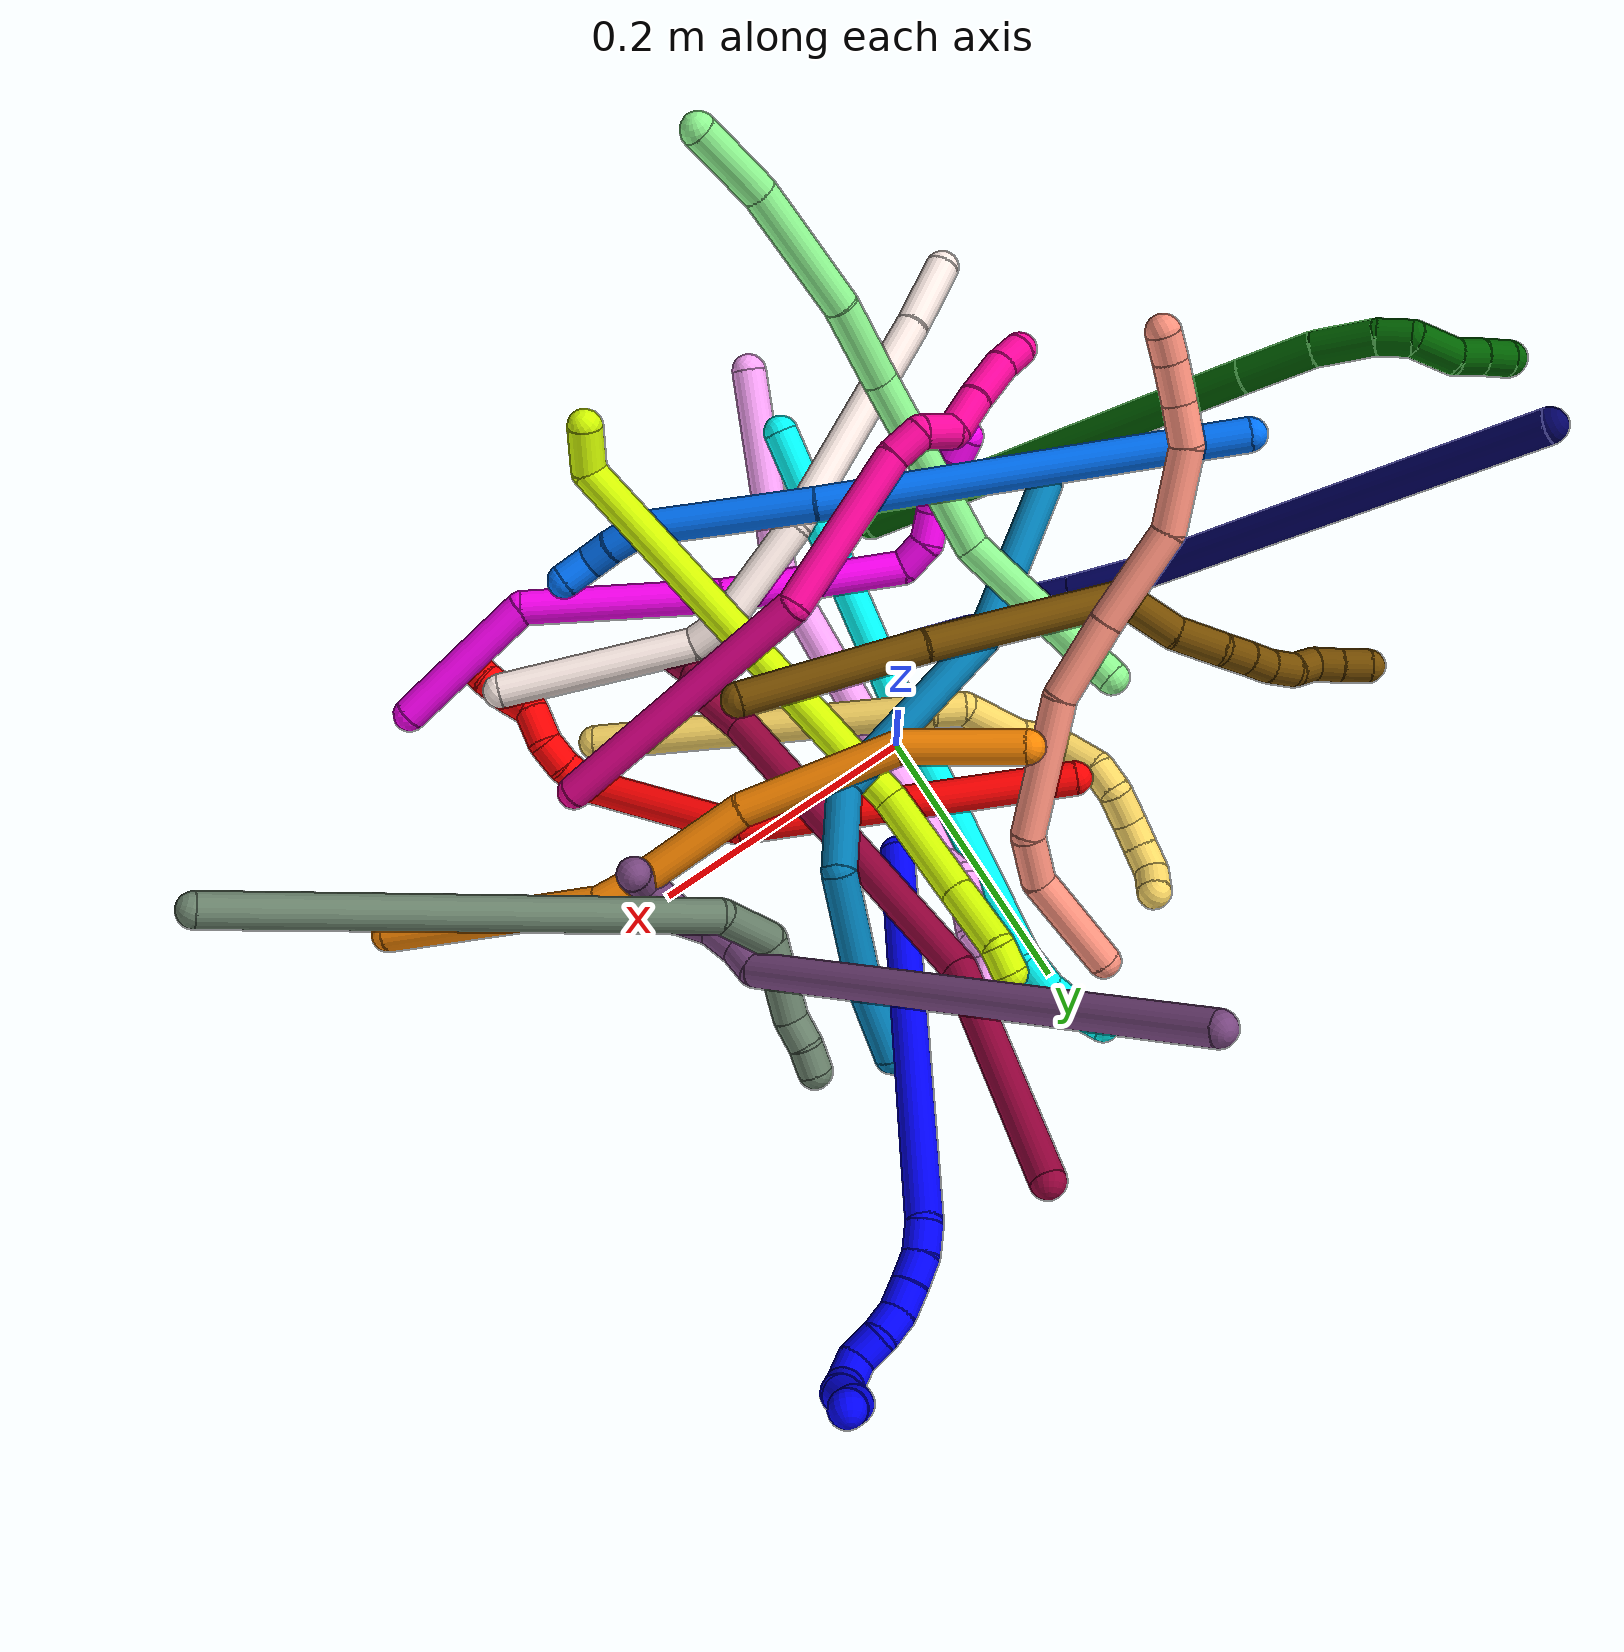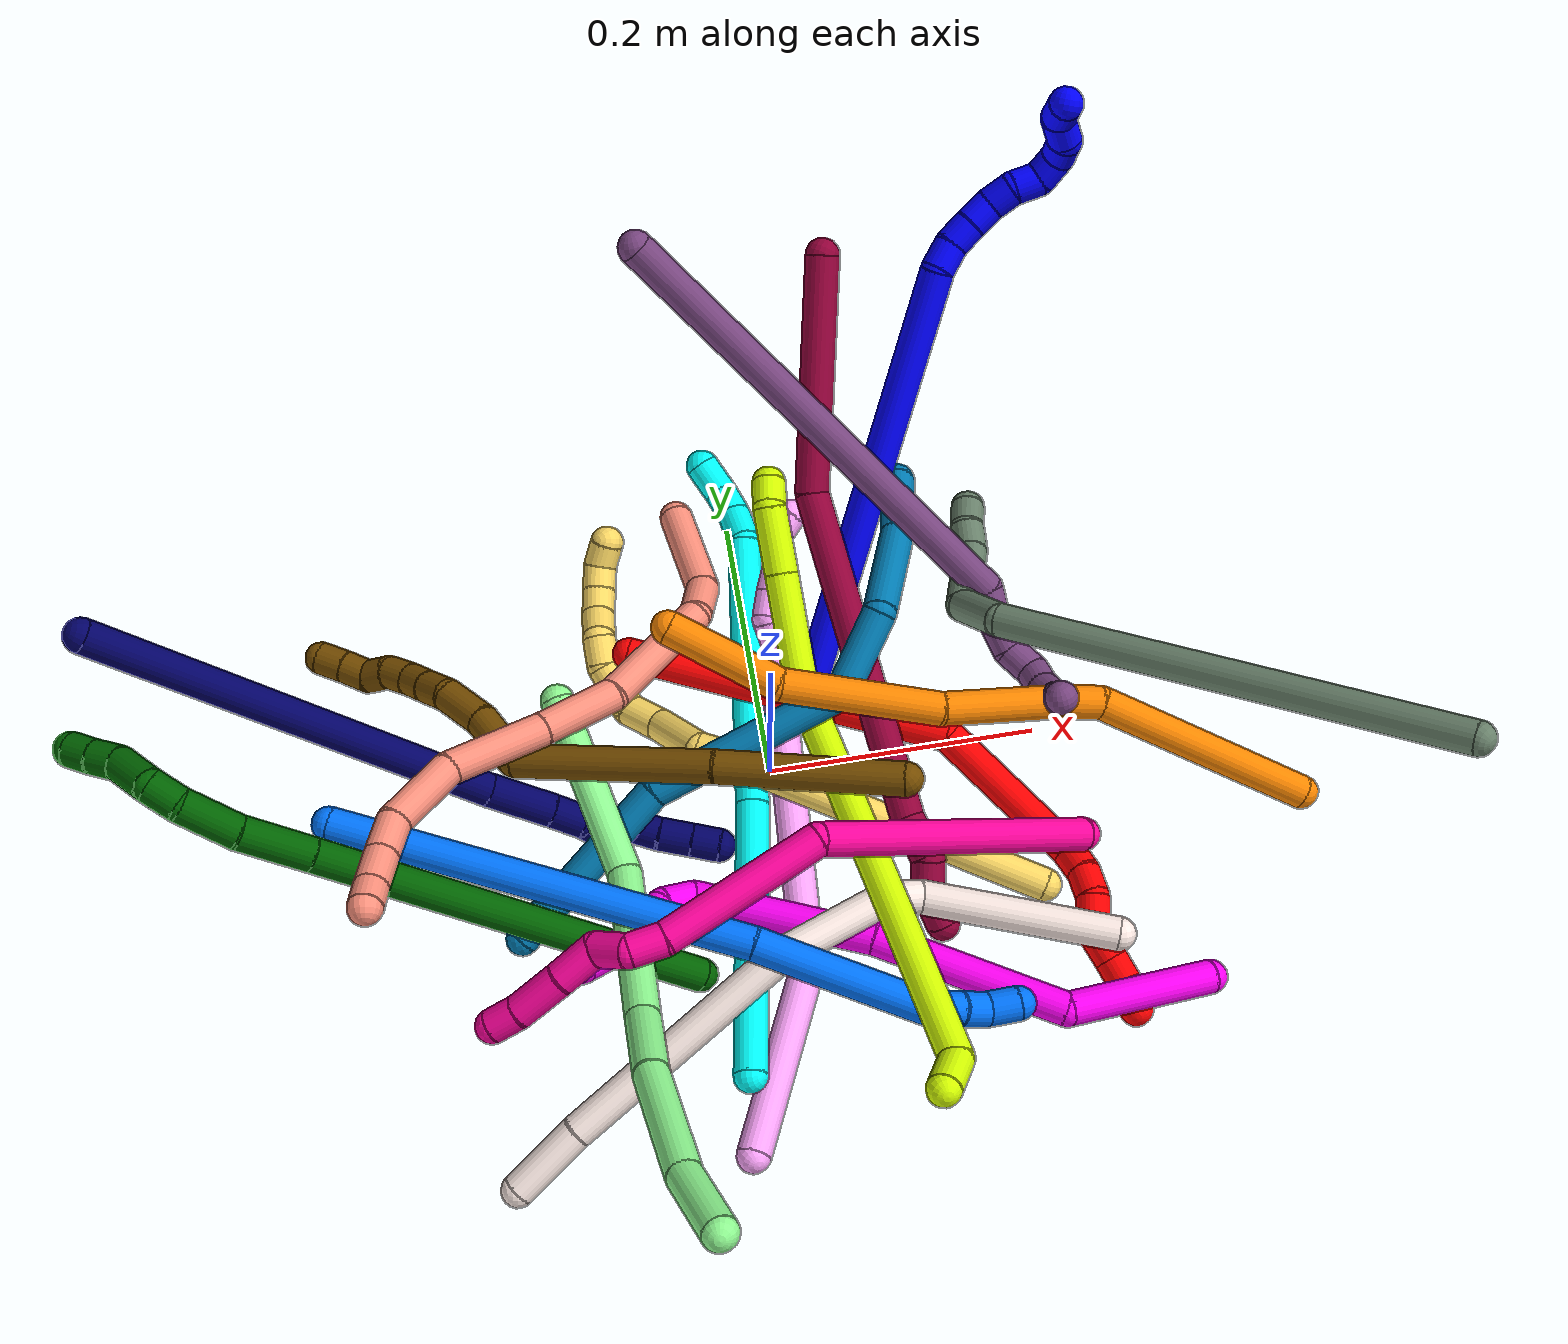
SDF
<sdf version="1.7">
 <world name="default">
  <plugin name="TubeGeneratorPlugin" filename="libtube_generator_plugin.so"/>
  <model name="photoneo_s_sensor">
   <static>1</static>
   <pose>0 0 2 1.57079 1.57079 3.14159</pose>
   <link name="link">
    <inertial><mass>0.1</mass></inertial>
    <sensor name="sensor" type="depth">
     <update_rate>30</update_rate>
     <camera>
      <horizontal_fov>1.22</horizontal_fov>
      <image><width>1920</width><height>1200</height><format>B8G8R8</format></image>
      <clip><near>0.1</near><far>4</far></clip>
      <depth_camera><output>points</output></depth_camera>
     </camera>
     <plugin name="camera_plugin" filename="libgazebo_ros_depth_camera.so">
      <baseline>0.2</baseline>
      <alwaysOn>1</alwaysOn>
      <updateRate>0.0</updateRate>
      <cameraName>camera_ir</cameraName>
      <imageTopicName>/camera/color/image_raw</imageTopicName>
      <cameraInfoTopicName>/camera/color/camera_info</cameraInfoTopicName>
      <depthImageTopicName>/camera/depth/image_raw</depthImageTopicName>
      <depthImageCameraInfoTopicName>/camera/depth/camera_info</depthImageCameraInfoTopicName>
      <pointCloudTopicName>/camera/depth/points</pointCloudTopicName>
      <frameName>fr_optical</frameName>
      <pointCloudCutoff>0.1</pointCloudCutoff>
      <pointCloudCutoffMax>2.0</pointCloudCutoffMax>
      <distortionK1>0</distortionK1>
      <distortionK2>0</distortionK2>
      <distortionK3>0</distortionK3>
      <distortionT1>0</distortionT1>
      <distortionT2>0</distortionT2>
      <CxPrime>0</CxPrime>
      <Cx>0</Cx>
      <Cy>0</Cy>
      <focalLength>0</focalLength>
      <hackBaseline>0</hackBaseline>
     </plugin>
    </sensor>
   </link>
  </model>
  <gravity>0 0 -9.8</gravity>
  <magnetic_field>6e-06 2.3e-05 -4.2e-05</magnetic_field>
  <atmosphere type="adiabatic"/>
  <physics name="default_physics" default="0" type="ode">
   <max_step_size>0.003</max_step_size>
   <real_time_factor>1</real_time_factor>
   <real_time_update_rate>1000</real_time_update_rate>
   <max_contacts>10000</max_contacts>
   <ode>
    <solver>
     <type>quick</type>
     <iters>100</iters>
     <sor>1.3</sor>
     <use_dynamic_moi_rescaling>0</use_dynamic_moi_rescaling>
    </solver>
    <constraints>
     <contact_max_correcting_vel>0</contact_max_correcting_vel>
     <contact_surface_layer>0.001</contact_surface_layer>
     <cfm>0</cfm>
     <erp>0.2</erp>
    </constraints>
   </ode>
  </physics>
  <scene><ambient>0.4 0.4 0.4 1</ambient><background>0.7 0.7 0.7 1</background><shadows>0</shadows></scene>
  <audio><device>default</device></audio>
  <spherical_coordinates>
   <surface_model>EARTH_WGS84</surface_model>
   <latitude_deg>0</latitude_deg>
   <longitude_deg>0</longitude_deg>
   <elevation>0</elevation>
   <heading_deg>0</heading_deg>
  </spherical_coordinates>
  <model name="bin">
   <static>1</static>
   <link name="bottom">
    <collision name="collision-bottom">
     <pose>0 0 -0.01 0 -0 0</pose>
     <geometry><box><size>0.8 0.6 0.02</size></box></geometry>
     <surface>
      <friction><ode><mu>100</mu><mu2>100</mu2></ode></friction>
      <contact><collide_bitmask>65535</collide_bitmask></contact>
     </surface>
    </collision>
   </link>
   <link name="west_wall">
    <collision name="collision-west_wall">
     <pose>-0.41 0 0.1 0 -0 0</pose>
     <geometry><box><size>0.02 0.6 0.2</size></box></geometry>
     <surface>
      <friction><ode><mu>100</mu><mu2>100</mu2></ode></friction>
      <contact><collide_bitmask>65535</collide_bitmask></contact>
     </surface>
    </collision>
   </link>
   <link name="east_wall">
    <collision name="collision-east_wall">
     <pose>0.41 0 0.1 0 -0 0</pose>
     <geometry><box><size>0.02 0.6 0.2</size></box></geometry>
     <surface>
      <friction><ode><mu>100</mu><mu2>100</mu2></ode></friction>
      <contact><collide_bitmask>65535</collide_bitmask></contact>
     </surface>
    </collision>
   </link>
   <link name="south_wall">
    <collision name="collision-south_wall">
     <pose>0 -0.31 0.1 0 -0 0</pose>
     <geometry><box><size>0.8 0.02 0.2</size></box></geometry>
     <surface>
      <friction><ode><mu>100</mu><mu2>100</mu2></ode></friction>
      <contact><collide_bitmask>65535</collide_bitmask></contact>
     </surface>
    </collision>
   </link>
   <link name="north_wall">
    <collision name="collision-north_wall">
     <pose>0 0.31 0.1 0 -0 0</pose>
     <geometry><box><size>0.8 0.02 0.2</size></box></geometry>
     <surface>
      <friction><ode><mu>100</mu><mu2>100</mu2></ode></friction>
      <contact><collide_bitmask>65535</collide_bitmask></contact>
     </surface>
    </collision>
   </link>
  </model>
  <model name="1">
   <static>0</static>
   <link name="1">
    <collision name="collision-cylinder-e_1_1_4">
     <pose>0.011566 -0.008713 0.158798 0.054812 0.072597 0.001991</pose>
     <geometry><cylinder><radius>0.0125</radius><length>0.318913</length></cylinder></geometry>
     <surface>
      <friction><ode><mu>1.16</mu><mu2>1.16</mu2><slip1>0</slip1><slip2>0</slip2></ode></friction>
      <contact><ode><kp>1e+06</kp><kd>1</kd><max_vel>0</max_vel><min_depth>0.001</min_depth></ode></contact>
     </surface>
    </collision>
    <visual name="visual-cylinder-e_1_1_4">
     <pose>0.011566 -0.008713 0.158798 0.054812 0.072597 0.001991</pose>
     <geometry><cylinder><radius>0.0125</radius><length>0.318913</length></cylinder></geometry>
     <material><ambient>0 0 1 1</ambient></material>
    </visual>
    <collision name="collision-cylinder-e_2_4_5">
     <pose>0.027265 -0.016362 0.327233 -0.109955 0.402946 -0.022479</pose>
     <geometry><cylinder><radius>0.0125</radius><length>0.02108</length></cylinder></geometry>
     <surface>
      <friction><ode><mu>1.16</mu><mu2>1.16</mu2><slip1>0</slip1><slip2>0</slip2></ode></friction>
      <contact><ode><kp>1e+06</kp><kd>1</kd><max_vel>0</max_vel><min_depth>0.001</min_depth></ode></contact>
     </surface>
    </collision>
    <visual name="visual-cylinder-e_2_4_5">
     <pose>0.027265 -0.016362 0.327233 -0.109955 0.402946 -0.022479</pose>
     <geometry><cylinder><radius>0.0125</radius><length>0.02108</length></cylinder></geometry>
     <material><ambient>0 0 1 1</ambient></material>
    </visual>
    <collision name="collision-cylinder-e_3_5_6">
     <pose>0.036842 -0.016274 0.345201 0.116644 0.575623 0.034566</pose>
     <geometry><cylinder><radius>0.0125</radius><length>0.02</length></cylinder></geometry>
     <surface>
      <friction><ode><mu>1.16</mu><mu2>1.16</mu2><slip1>0</slip1><slip2>0</slip2></ode></friction>
      <contact><ode><kp>1e+06</kp><kd>1</kd><max_vel>0</max_vel><min_depth>0.001</min_depth></ode></contact>
     </surface>
    </collision>
    <visual name="visual-cylinder-e_3_5_6">
     <pose>0.036842 -0.016274 0.345201 0.116644 0.575623 0.034566</pose>
     <geometry><cylinder><radius>0.0125</radius><length>0.02</length></cylinder></geometry>
     <material><ambient>0 0 1 1</ambient></material>
    </visual>
    <collision name="collision-cylinder-e_4_6_7">
     <pose>0.048238 -0.018093 0.361524 0.105142 0.637641 0.034734</pose>
     <geometry><cylinder><radius>0.0125</radius><length>0.020001</length></cylinder></geometry>
     <surface>
      <friction><ode><mu>1.16</mu><mu2>1.16</mu2><slip1>0</slip1><slip2>0</slip2></ode></friction>
      <contact><ode><kp>1e+06</kp><kd>1</kd><max_vel>0</max_vel><min_depth>0.001</min_depth></ode></contact>
     </surface>
    </collision>
    <visual name="visual-cylinder-e_4_6_7">
     <pose>0.048238 -0.018093 0.361524 0.105142 0.637641 0.034734</pose>
     <geometry><cylinder><radius>0.0125</radius><length>0.020001</length></cylinder></geometry>
     <material><ambient>0 0 1 1</ambient></material>
    </visual>
    <collision name="collision-cylinder-e_5_7_8">
     <pose>0.059664 -0.022935 0.376872 0.497769 0.578918 0.151098</pose>
     <geometry><cylinder><radius>0.0125</radius><length>0.020006</length></cylinder></geometry>
     <surface>
      <friction><ode><mu>1.16</mu><mu2>1.16</mu2><slip1>0</slip1><slip2>0</slip2></ode></friction>
      <contact><ode><kp>1e+06</kp><kd>1</kd><max_vel>0</max_vel><min_depth>0.001</min_depth></ode></contact>
     </surface>
    </collision>
    <visual name="visual-cylinder-e_5_7_8">
     <pose>0.059664 -0.022935 0.376872 0.497769 0.578918 0.151098</pose>
     <geometry><cylinder><radius>0.0125</radius><length>0.020006</length></cylinder></geometry>
     <material><ambient>0 0 1 1</ambient></material>
    </visual>
    <collision name="collision-cylinder-e_6_8_9">
     <pose>0.073487 -0.029424 0.389135 0.469891 0.988172 0.256453</pose>
     <geometry><cylinder><radius>0.0125</radius><length>0.02</length></cylinder></geometry>
     <surface>
      <friction><ode><mu>1.16</mu><mu2>1.16</mu2><slip1>0</slip1><slip2>0</slip2></ode></friction>
      <contact><ode><kp>1e+06</kp><kd>1</kd><max_vel>0</max_vel><min_depth>0.001</min_depth></ode></contact>
     </surface>
    </collision>
    <visual name="visual-cylinder-e_6_8_9">
     <pose>0.073487 -0.029424 0.389135 0.469891 0.988172 0.256453</pose>
     <geometry><cylinder><radius>0.0125</radius><length>0.02</length></cylinder></geometry>
     <material><ambient>0 0 1 1</ambient></material>
    </visual>
    <collision name="collision-cylinder-e_7_9_10">
     <pose>0.085199 -0.035337 0.402815 0.371833 0.342782 0.065089</pose>
     <geometry><cylinder><radius>0.0125</radius><length>0.02</length></cylinder></geometry>
     <surface>
      <friction><ode><mu>1.16</mu><mu2>1.16</mu2><slip1>0</slip1><slip2>0</slip2></ode></friction>
      <contact><ode><kp>1e+06</kp><kd>1</kd><max_vel>0</max_vel><min_depth>0.001</min_depth></ode></contact>
     </surface>
    </collision>
    <visual name="visual-cylinder-e_7_9_10">
     <pose>0.085199 -0.035337 0.402815 0.371833 0.342782 0.065089</pose>
     <geometry><cylinder><radius>0.0125</radius><length>0.02</length></cylinder></geometry>
     <material><ambient>0 0 1 1</ambient></material>
    </visual>
    <collision name="collision-cylinder-e_8_10_11">
     <pose>0.085767 -0.045641 0.418286 0.799153 -0.283047 -0.120189</pose>
     <geometry><cylinder><radius>0.0125</radius><length>0.02</length></cylinder></geometry>
     <surface>
      <friction><ode><mu>1.16</mu><mu2>1.16</mu2><slip1>0</slip1><slip2>0</slip2></ode></friction>
      <contact><ode><kp>1e+06</kp><kd>1</kd><max_vel>0</max_vel><min_depth>0.001</min_depth></ode></contact>
     </surface>
    </collision>
    <visual name="visual-cylinder-e_8_10_11">
     <pose>0.085767 -0.045641 0.418286 0.799153 -0.283047 -0.120189</pose>
     <geometry><cylinder><radius>0.0125</radius><length>0.02</length></cylinder></geometry>
     <material><ambient>0 0 1 1</ambient></material>
    </visual>
    <collision name="collision-cylinder-e_9_11_12">
     <pose>0.076851 -0.054599 0.43261 0.265603 -0.659055 -0.09131</pose>
     <geometry><cylinder><radius>0.0125</radius><length>0.02</length></cylinder></geometry>
     <surface>
      <friction><ode><mu>1.16</mu><mu2>1.16</mu2><slip1>0</slip1><slip2>0</slip2></ode></friction>
      <contact><ode><kp>1e+06</kp><kd>1</kd><max_vel>0</max_vel><min_depth>0.001</min_depth></ode></contact>
     </surface>
    </collision>
    <visual name="visual-cylinder-e_9_11_12">
     <pose>0.076851 -0.054599 0.43261 0.265603 -0.659055 -0.09131</pose>
     <geometry><cylinder><radius>0.0125</radius><length>0.02</length></cylinder></geometry>
     <material><ambient>0 0 1 1</ambient></material>
    </visual>
    <collision name="collision-cylinder-e_10_12_2">
     <pose>0.067768 -0.064323 0.44596 0.928544 -0.300399 -0.151286</pose>
     <geometry><cylinder><radius>0.0125</radius><length>0.02</length></cylinder></geometry>
     <surface>
      <friction><ode><mu>1.16</mu><mu2>1.16</mu2><slip1>0</slip1><slip2>0</slip2></ode></friction>
      <contact><ode><kp>1e+06</kp><kd>1</kd><max_vel>0</max_vel><min_depth>0.001</min_depth></ode></contact>
     </surface>
    </collision>
    <visual name="visual-cylinder-e_10_12_2">
     <pose>0.067768 -0.064323 0.44596 0.928544 -0.300399 -0.151286</pose>
     <geometry><cylinder><radius>0.0125</radius><length>0.02</length></cylinder></geometry>
     <material><ambient>0 0 1 1</ambient></material>
    </visual>
    <collision name="collision-sphere-2">
     <pose>0.064809 -0.071972 0.451682 0 -0 0</pose>
     <geometry><sphere><radius>0.0125</radius></sphere></geometry>
     <surface>
      <friction><ode><mu>1.16</mu><mu2>1.16</mu2><slip1>0</slip1><slip2>0</slip2></ode></friction>
      <contact><ode><kp>1e+06</kp><kd>1</kd><max_vel>0</max_vel><min_depth>0.001</min_depth></ode></contact>
     </surface>
    </collision>
    <visual name="visual-sphere-2">
     <pose>0.064809 -0.071972 0.451682 0 -0 0</pose>
     <geometry><sphere><radius>0.0125</radius></sphere></geometry>
     <material><ambient>0 0 1 1</ambient></material>
    </visual>
    <collision name="collision-sphere-12">
     <pose>0.070727 -0.056674 0.440238 0 -0 0</pose>
     <geometry><sphere><radius>0.0125</radius></sphere></geometry>
     <surface>
      <friction><ode><mu>1.16</mu><mu2>1.16</mu2><slip1>0</slip1><slip2>0</slip2></ode></friction>
      <contact><ode><kp>1e+06</kp><kd>1</kd><max_vel>0</max_vel><min_depth>0.001</min_depth></ode></contact>
     </surface>
    </collision>
    <visual name="visual-sphere-12">
     <pose>0.070727 -0.056674 0.440238 0 -0 0</pose>
     <geometry><sphere><radius>0.0125</radius></sphere></geometry>
     <material><ambient>0 0 1 1</ambient></material>
    </visual>
    <collision name="collision-sphere-11">
     <pose>0.082974 -0.052524 0.424981 0 -0 0</pose>
     <geometry><sphere><radius>0.0125</radius></sphere></geometry>
     <surface>
      <friction><ode><mu>1.16</mu><mu2>1.16</mu2><slip1>0</slip1><slip2>0</slip2></ode></friction>
      <contact><ode><kp>1e+06</kp><kd>1</kd><max_vel>0</max_vel><min_depth>0.001</min_depth></ode></contact>
     </surface>
    </collision>
    <visual name="visual-sphere-11">
     <pose>0.082974 -0.052524 0.424981 0 -0 0</pose>
     <geometry><sphere><radius>0.0125</radius></sphere></geometry>
     <material><ambient>0 0 1 1</ambient></material>
    </visual>
    <collision name="collision-sphere-10">
     <pose>0.08856 -0.038759 0.41159 0 -0 0</pose>
     <geometry><sphere><radius>0.0125</radius></sphere></geometry>
     <surface>
      <friction><ode><mu>1.16</mu><mu2>1.16</mu2><slip1>0</slip1><slip2>0</slip2></ode></friction>
      <contact><ode><kp>1e+06</kp><kd>1</kd><max_vel>0</max_vel><min_depth>0.001</min_depth></ode></contact>
     </surface>
    </collision>
    <visual name="visual-sphere-10">
     <pose>0.08856 -0.038759 0.41159 0 -0 0</pose>
     <geometry><sphere><radius>0.0125</radius></sphere></geometry>
     <material><ambient>0 0 1 1</ambient></material>
    </visual>
    <collision name="collision-sphere-9">
     <pose>0.081838 -0.031915 0.39404 0 -0 0</pose>
     <geometry><sphere><radius>0.0125</radius></sphere></geometry>
     <surface>
      <friction><ode><mu>1.16</mu><mu2>1.16</mu2><slip1>0</slip1><slip2>0</slip2></ode></friction>
      <contact><ode><kp>1e+06</kp><kd>1</kd><max_vel>0</max_vel><min_depth>0.001</min_depth></ode></contact>
     </surface>
    </collision>
    <visual name="visual-sphere-9">
     <pose>0.081838 -0.031915 0.39404 0 -0 0</pose>
     <geometry><sphere><radius>0.0125</radius></sphere></geometry>
     <material><ambient>0 0 1 1</ambient></material>
    </visual>
    <collision name="collision-sphere-4">
     <pose>0.023132 -0.017425 0.317595 0 -0 0</pose>
     <geometry><sphere><radius>0.0125</radius></sphere></geometry>
     <surface>
      <friction><ode><mu>1.16</mu><mu2>1.16</mu2><slip1>0</slip1><slip2>0</slip2></ode></friction>
      <contact><ode><kp>1e+06</kp><kd>1</kd><max_vel>0</max_vel><min_depth>0.001</min_depth></ode></contact>
     </surface>
    </collision>
    <visual name="visual-sphere-4">
     <pose>0.023132 -0.017425 0.317595 0 -0 0</pose>
     <geometry><sphere><radius>0.0125</radius></sphere></geometry>
     <material><ambient>0 0 1 1</ambient></material>
    </visual>
    <collision name="collision-sphere-1">
     <geometry><sphere><radius>0.0125</radius></sphere></geometry>
     <surface>
      <friction><ode><mu>1.16</mu><mu2>1.16</mu2><slip1>0</slip1><slip2>0</slip2></ode></friction>
      <contact><ode><kp>1e+06</kp><kd>1</kd><max_vel>0</max_vel><min_depth>0.001</min_depth></ode></contact>
     </surface>
    </collision>
    <visual name="visual-sphere-1">
     <geometry><sphere><radius>0.0125</radius></sphere></geometry>
     <material><ambient>0 0 1 1</ambient></material>
    </visual>
    <collision name="collision-sphere-8">
     <pose>0.065137 -0.026932 0.384229 0 -0 0</pose>
     <geometry><sphere><radius>0.0125</radius></sphere></geometry>
     <surface>
      <friction><ode><mu>1.16</mu><mu2>1.16</mu2><slip1>0</slip1><slip2>0</slip2></ode></friction>
      <contact><ode><kp>1e+06</kp><kd>1</kd><max_vel>0</max_vel><min_depth>0.001</min_depth></ode></contact>
     </surface>
    </collision>
    <visual name="visual-sphere-8">
     <pose>0.065137 -0.026932 0.384229 0 -0 0</pose>
     <geometry><sphere><radius>0.0125</radius></sphere></geometry>
     <material><ambient>0 0 1 1</ambient></material>
    </visual>
    <collision name="collision-sphere-5">
     <pose>0.031398 -0.015298 0.33687 0 -0 0</pose>
     <geometry><sphere><radius>0.0125</radius></sphere></geometry>
     <surface>
      <friction><ode><mu>1.16</mu><mu2>1.16</mu2><slip1>0</slip1><slip2>0</slip2></ode></friction>
      <contact><ode><kp>1e+06</kp><kd>1</kd><max_vel>0</max_vel><min_depth>0.001</min_depth></ode></contact>
     </surface>
    </collision>
    <visual name="visual-sphere-5">
     <pose>0.031398 -0.015298 0.33687 0 -0 0</pose>
     <geometry><sphere><radius>0.0125</radius></sphere></geometry>
     <material><ambient>0 0 1 1</ambient></material>
    </visual>
    <collision name="collision-sphere-6">
     <pose>0.042285 -0.01725 0.353533 0 -0 0</pose>
     <geometry><sphere><radius>0.0125</radius></sphere></geometry>
     <surface>
      <friction><ode><mu>1.16</mu><mu2>1.16</mu2><slip1>0</slip1><slip2>0</slip2></ode></friction>
      <contact><ode><kp>1e+06</kp><kd>1</kd><max_vel>0</max_vel><min_depth>0.001</min_depth></ode></contact>
     </surface>
    </collision>
    <visual name="visual-sphere-6">
     <pose>0.042285 -0.01725 0.353533 0 -0 0</pose>
     <geometry><sphere><radius>0.0125</radius></sphere></geometry>
     <material><ambient>0 0 1 1</ambient></material>
    </visual>
    <collision name="collision-sphere-7">
     <pose>0.054192 -0.018937 0.369515 0 -0 0</pose>
     <geometry><sphere><radius>0.0125</radius></sphere></geometry>
     <surface>
      <friction><ode><mu>1.16</mu><mu2>1.16</mu2><slip1>0</slip1><slip2>0</slip2></ode></friction>
      <contact><ode><kp>1e+06</kp><kd>1</kd><max_vel>0</max_vel><min_depth>0.001</min_depth></ode></contact>
     </surface>
    </collision>
    <visual name="visual-sphere-7">
     <pose>0.054192 -0.018937 0.369515 0 -0 0</pose>
     <geometry><sphere><radius>0.0125</radius></sphere></geometry>
     <material><ambient>0 0 1 1</ambient></material>
    </visual>
    <inertial>
     <pose>0.02988 -0.017712 0.241983 0 -0 0</pose>
     <mass>0.5</mass>
     <inertia>
      <ixx>0.00273</ixx>
      <ixy>0</ixy>
      <ixz>0</ixz>
      <iyy>0.002723</iyy>
      <iyz>0</iyz>
      <izz>-1.2e-05</izz>
     </inertia>
    </inertial>
   </link>
   <pose>0.044057 0.066167 0.0123 -0.820241 0.454863 -0.018925</pose>
  </model>
  <model name="2">
   <static>0</static>
   <link name="2">
    <collision name="collision-cylinder-e_1_1_4">
     <pose>0.045699 -0.111108 0.02016 1.3913 0.38455 0.32225</pose>
     <geometry><cylinder><radius>0.0125</radius><length>0.243638</length></cylinder></geometry>
     <surface>
      <friction><ode><mu>1.16</mu><mu2>1.16</mu2><slip1>0</slip1><slip2>0</slip2></ode></friction>
      <contact><ode><kp>1e+06</kp><kd>1</kd><max_vel>0</max_vel><min_depth>0.001</min_depth></ode></contact>
     </surface>
    </collision>
    <visual name="visual-cylinder-e_1_1_4">
     <pose>0.045699 -0.111108 0.02016 1.3913 0.38455 0.32225</pose>
     <geometry><cylinder><radius>0.0125</radius><length>0.243638</length></cylinder></geometry>
     <material><ambient>1 0 0 1</ambient></material>
    </visual>
    <collision name="collision-cylinder-e_2_4_5">
     <pose>0.082321 -0.280806 0.055691 1.31424 -0.148756 -0.114852</pose>
     <geometry><cylinder><radius>0.0125</radius><length>0.122499</length></cylinder></geometry>
     <surface>
      <friction><ode><mu>1.16</mu><mu2>1.16</mu2><slip1>0</slip1><slip2>0</slip2></ode></friction>
      <contact><ode><kp>1e+06</kp><kd>1</kd><max_vel>0</max_vel><min_depth>0.001</min_depth></ode></contact>
     </surface>
    </collision>
    <visual name="visual-cylinder-e_2_4_5">
     <pose>0.082321 -0.280806 0.055691 1.31424 -0.148756 -0.114852</pose>
     <geometry><cylinder><radius>0.0125</radius><length>0.122499</length></cylinder></geometry>
     <material><ambient>1 0 0 1</ambient></material>
    </visual>
    <collision name="collision-cylinder-e_3_5_6">
     <pose>0.073512 -0.345645 0.080512 0.584186 0.023677 0.00712</pose>
     <geometry><cylinder><radius>0.0125</radius><length>0.022665</length></cylinder></geometry>
     <surface>
      <friction><ode><mu>1.16</mu><mu2>1.16</mu2><slip1>0</slip1><slip2>0</slip2></ode></friction>
      <contact><ode><kp>1e+06</kp><kd>1</kd><max_vel>0</max_vel><min_depth>0.001</min_depth></ode></contact>
     </surface>
    </collision>
    <visual name="visual-cylinder-e_3_5_6">
     <pose>0.073512 -0.345645 0.080512 0.584186 0.023677 0.00712</pose>
     <geometry><cylinder><radius>0.0125</radius><length>0.022665</length></cylinder></geometry>
     <material><ambient>1 0 0 1</ambient></material>
    </visual>
    <collision name="collision-cylinder-e_4_6_7">
     <pose>0.071655 -0.356879 0.099362 0.487676 -0.197099 -0.049185</pose>
     <geometry><cylinder><radius>0.0125</radius><length>0.021702</length></cylinder></geometry>
     <surface>
      <friction><ode><mu>1.16</mu><mu2>1.16</mu2><slip1>0</slip1><slip2>0</slip2></ode></friction>
      <contact><ode><kp>1e+06</kp><kd>1</kd><max_vel>0</max_vel><min_depth>0.001</min_depth></ode></contact>
     </surface>
    </collision>
    <visual name="visual-cylinder-e_4_6_7">
     <pose>0.071655 -0.356879 0.099362 0.487676 -0.197099 -0.049185</pose>
     <geometry><cylinder><radius>0.0125</radius><length>0.021702</length></cylinder></geometry>
     <material><ambient>1 0 0 1</ambient></material>
    </visual>
    <collision name="collision-cylinder-e_5_7_8">
     <pose>0.062147 -0.366966 0.118473 0.483702 -0.592476 -0.150299</pose>
     <geometry><cylinder><radius>0.0125</radius><length>0.026444</length></cylinder></geometry>
     <surface>
      <friction><ode><mu>1.16</mu><mu2>1.16</mu2><slip1>0</slip1><slip2>0</slip2></ode></friction>
      <contact><ode><kp>1e+06</kp><kd>1</kd><max_vel>0</max_vel><min_depth>0.001</min_depth></ode></contact>
     </surface>
    </collision>
    <visual name="visual-cylinder-e_5_7_8">
     <pose>0.062147 -0.366966 0.118473 0.483702 -0.592476 -0.150299</pose>
     <geometry><cylinder><radius>0.0125</radius><length>0.026444</length></cylinder></geometry>
     <material><ambient>1 0 0 1</ambient></material>
    </visual>
    <collision name="collision-cylinder-e_6_8_9">
     <pose>0.050661 -0.381965 0.132041 1.19913 -0.36855 -0.253428</pose>
     <geometry><cylinder><radius>0.0125</radius><length>0.022777</length></cylinder></geometry>
     <surface>
      <friction><ode><mu>1.16</mu><mu2>1.16</mu2><slip1>0</slip1><slip2>0</slip2></ode></friction>
      <contact><ode><kp>1e+06</kp><kd>1</kd><max_vel>0</max_vel><min_depth>0.001</min_depth></ode></contact>
     </surface>
    </collision>
    <visual name="visual-cylinder-e_6_8_9">
     <pose>0.050661 -0.381965 0.132041 1.19913 -0.36855 -0.253428</pose>
     <geometry><cylinder><radius>0.0125</radius><length>0.022777</length></cylinder></geometry>
     <material><ambient>1 0 0 1</ambient></material>
    </visual>
    <collision name="collision-cylinder-e_7_9_10">
     <pose>0.044453 -0.398971 0.142665 0.810038 -0.211349 -0.090886</pose>
     <geometry><cylinder><radius>0.0125</radius><length>0.020071</length></cylinder></geometry>
     <surface>
      <friction><ode><mu>1.16</mu><mu2>1.16</mu2><slip1>0</slip1><slip2>0</slip2></ode></friction>
      <contact><ode><kp>1e+06</kp><kd>1</kd><max_vel>0</max_vel><min_depth>0.001</min_depth></ode></contact>
     </surface>
    </collision>
    <visual name="visual-cylinder-e_7_9_10">
     <pose>0.044453 -0.398971 0.142665 0.810038 -0.211349 -0.090886</pose>
     <geometry><cylinder><radius>0.0125</radius><length>0.020071</length></cylinder></geometry>
     <material><ambient>1 0 0 1</ambient></material>
    </visual>
    <collision name="collision-cylinder-e_8_10_2">
     <pose>0.038594 -0.413293 0.155424 0.877543 -0.380634 -0.180322</pose>
     <geometry><cylinder><radius>0.0125</radius><length>0.020205</length></cylinder></geometry>
     <surface>
      <friction><ode><mu>1.16</mu><mu2>1.16</mu2><slip1>0</slip1><slip2>0</slip2></ode></friction>
      <contact><ode><kp>1e+06</kp><kd>1</kd><max_vel>0</max_vel><min_depth>0.001</min_depth></ode></contact>
     </surface>
    </collision>
    <visual name="visual-cylinder-e_8_10_2">
     <pose>0.038594 -0.413293 0.155424 0.877543 -0.380634 -0.180322</pose>
     <geometry><cylinder><radius>0.0125</radius><length>0.020205</length></cylinder></geometry>
     <material><ambient>1 0 0 1</ambient></material>
    </visual>
    <collision name="collision-sphere-2">
     <pose>0.034841 -0.420507 0.161418 0 -0 0</pose>
     <geometry><sphere><radius>0.0125</radius></sphere></geometry>
     <surface>
      <friction><ode><mu>1.16</mu><mu2>1.16</mu2><slip1>0</slip1><slip2>0</slip2></ode></friction>
      <contact><ode><kp>1e+06</kp><kd>1</kd><max_vel>0</max_vel><min_depth>0.001</min_depth></ode></contact>
     </surface>
    </collision>
    <visual name="visual-sphere-2">
     <pose>0.034841 -0.420507 0.161418 0 -0 0</pose>
     <geometry><sphere><radius>0.0125</radius></sphere></geometry>
     <material><ambient>1 0 0 1</ambient></material>
    </visual>
    <collision name="collision-sphere-10">
     <pose>0.042347 -0.406078 0.14943 0 -0 0</pose>
     <geometry><sphere><radius>0.0125</radius></sphere></geometry>
     <surface>
      <friction><ode><mu>1.16</mu><mu2>1.16</mu2><slip1>0</slip1><slip2>0</slip2></ode></friction>
      <contact><ode><kp>1e+06</kp><kd>1</kd><max_vel>0</max_vel><min_depth>0.001</min_depth></ode></contact>
     </surface>
    </collision>
    <visual name="visual-sphere-10">
     <pose>0.042347 -0.406078 0.14943 0 -0 0</pose>
     <geometry><sphere><radius>0.0125</radius></sphere></geometry>
     <material><ambient>1 0 0 1</ambient></material>
    </visual>
    <collision name="collision-sphere-9">
     <pose>0.046558 -0.391864 0.135899 0 -0 0</pose>
     <geometry><sphere><radius>0.0125</radius></sphere></geometry>
     <surface>
      <friction><ode><mu>1.16</mu><mu2>1.16</mu2><slip1>0</slip1><slip2>0</slip2></ode></friction>
      <contact><ode><kp>1e+06</kp><kd>1</kd><max_vel>0</max_vel><min_depth>0.001</min_depth></ode></contact>
     </surface>
    </collision>
    <visual name="visual-sphere-9">
     <pose>0.046558 -0.391864 0.135899 0 -0 0</pose>
     <geometry><sphere><radius>0.0125</radius></sphere></geometry>
     <material><ambient>1 0 0 1</ambient></material>
    </visual>
    <collision name="collision-sphere-4">
     <pose>0.091399 -0.222216 0.040321 0 -0 0</pose>
     <geometry><sphere><radius>0.0125</radius></sphere></geometry>
     <surface>
      <friction><ode><mu>1.16</mu><mu2>1.16</mu2><slip1>0</slip1><slip2>0</slip2></ode></friction>
      <contact><ode><kp>1e+06</kp><kd>1</kd><max_vel>0</max_vel><min_depth>0.001</min_depth></ode></contact>
     </surface>
    </collision>
    <visual name="visual-sphere-4">
     <pose>0.091399 -0.222216 0.040321 0 -0 0</pose>
     <geometry><sphere><radius>0.0125</radius></sphere></geometry>
     <material><ambient>1 0 0 1</ambient></material>
    </visual>
    <collision name="collision-sphere-1">
     <geometry><sphere><radius>0.0125</radius></sphere></geometry>
     <surface>
      <friction><ode><mu>1.16</mu><mu2>1.16</mu2><slip1>0</slip1><slip2>0</slip2></ode></friction>
      <contact><ode><kp>1e+06</kp><kd>1</kd><max_vel>0</max_vel><min_depth>0.001</min_depth></ode></contact>
     </surface>
    </collision>
    <visual name="visual-sphere-1">
     <geometry><sphere><radius>0.0125</radius></sphere></geometry>
     <material><ambient>1 0 0 1</ambient></material>
    </visual>
    <collision name="collision-sphere-8">
     <pose>0.054764 -0.372067 0.128183 0 -0 0</pose>
     <geometry><sphere><radius>0.0125</radius></sphere></geometry>
     <surface>
      <friction><ode><mu>1.16</mu><mu2>1.16</mu2><slip1>0</slip1><slip2>0</slip2></ode></friction>
      <contact><ode><kp>1e+06</kp><kd>1</kd><max_vel>0</max_vel><min_depth>0.001</min_depth></ode></contact>
     </surface>
    </collision>
    <visual name="visual-sphere-8">
     <pose>0.054764 -0.372067 0.128183 0 -0 0</pose>
     <geometry><sphere><radius>0.0125</radius></sphere></geometry>
     <material><ambient>1 0 0 1</ambient></material>
    </visual>
    <collision name="collision-sphere-5">
     <pose>0.073243 -0.339397 0.071061 0 -0 0</pose>
     <geometry><sphere><radius>0.0125</radius></sphere></geometry>
     <surface>
      <friction><ode><mu>1.16</mu><mu2>1.16</mu2><slip1>0</slip1><slip2>0</slip2></ode></friction>
      <contact><ode><kp>1e+06</kp><kd>1</kd><max_vel>0</max_vel><min_depth>0.001</min_depth></ode></contact>
     </surface>
    </collision>
    <visual name="visual-sphere-5">
     <pose>0.073243 -0.339397 0.071061 0 -0 0</pose>
     <geometry><sphere><radius>0.0125</radius></sphere></geometry>
     <material><ambient>1 0 0 1</ambient></material>
    </visual>
    <collision name="collision-sphere-6">
     <pose>0.07378 -0.351893 0.089962 0 -0 0</pose>
     <geometry><sphere><radius>0.0125</radius></sphere></geometry>
     <surface>
      <friction><ode><mu>1.16</mu><mu2>1.16</mu2><slip1>0</slip1><slip2>0</slip2></ode></friction>
      <contact><ode><kp>1e+06</kp><kd>1</kd><max_vel>0</max_vel><min_depth>0.001</min_depth></ode></contact>
     </surface>
    </collision>
    <visual name="visual-sphere-6">
     <pose>0.07378 -0.351893 0.089962 0 -0 0</pose>
     <geometry><sphere><radius>0.0125</radius></sphere></geometry>
     <material><ambient>1 0 0 1</ambient></material>
    </visual>
    <collision name="collision-sphere-7">
     <pose>0.06953 -0.361865 0.108763 0 -0 0</pose>
     <geometry><sphere><radius>0.0125</radius></sphere></geometry>
     <surface>
      <friction><ode><mu>1.16</mu><mu2>1.16</mu2><slip1>0</slip1><slip2>0</slip2></ode></friction>
      <contact><ode><kp>1e+06</kp><kd>1</kd><max_vel>0</max_vel><min_depth>0.001</min_depth></ode></contact>
     </surface>
    </collision>
    <visual name="visual-sphere-7">
     <pose>0.06953 -0.361865 0.108763 0 -0 0</pose>
     <geometry><sphere><radius>0.0125</radius></sphere></geometry>
     <material><ambient>1 0 0 1</ambient></material>
    </visual>
    <inertial>
     <pose>0.057818 -0.22362 0.055718 0 -0 0</pose>
     <mass>0.5</mass>
     <inertia>
      <ixx>0.001574</ixx>
      <ixy>0</ixy>
      <ixz>0</ixz>
      <iyy>0.000703</iyy>
      <iyz>0</iyz>
      <izz>0.000849</izz>
     </inertia>
    </inertial>
   </link>
   <pose>-0.090503 0.093541 0.044495 0.535367 -0.742898 0.61382</pose>
  </model>
  <model name="3">
   <static>0</static>
   <link name="3">
    <collision name="collision-cylinder-e_1_1_4">
     <pose>0.01929 0.104267 -0.011193 -1.67774 0.181916 -0.202357</pose>
     <geometry><cylinder><radius>0.0125</radius><length>0.213251</length></cylinder></geometry>
     <surface>
      <friction><ode><mu>1.16</mu><mu2>1.16</mu2><slip1>0</slip1><slip2>0</slip2></ode></friction>
      <contact><ode><kp>1e+06</kp><kd>1</kd><max_vel>0</max_vel><min_depth>0.001</min_depth></ode></contact>
     </surface>
    </collision>
    <visual name="visual-cylinder-e_1_1_4">
     <pose>0.01929 0.104267 -0.011193 -1.67774 0.181916 -0.202357</pose>
     <geometry><cylinder><radius>0.0125</radius><length>0.213251</length></cylinder></geometry>
     <material><ambient>0.003922 1 0.996078 1</ambient></material>
    </visual>
    <collision name="collision-cylinder-e_2_4_5">
     <pose>0.037078 0.312505 -0.025284 -1.59866 -0.014441 0.014849</pose>
     <geometry><cylinder><radius>0.0125</radius><length>0.208045</length></cylinder></geometry>
     <surface>
      <friction><ode><mu>1.16</mu><mu2>1.16</mu2><slip1>0</slip1><slip2>0</slip2></ode></friction>
      <contact><ode><kp>1e+06</kp><kd>1</kd><max_vel>0</max_vel><min_depth>0.001</min_depth></ode></contact>
     </surface>
    </collision>
    <visual name="visual-cylinder-e_2_4_5">
     <pose>0.037078 0.312505 -0.025284 -1.59866 -0.014441 0.014849</pose>
     <geometry><cylinder><radius>0.0125</radius><length>0.208045</length></cylinder></geometry>
     <material><ambient>0.003922 1 0.996078 1</ambient></material>
    </visual>
    <collision name="collision-cylinder-e_3_5_6">
     <pose>0.038965 0.430063 -0.034853 -2.02721 0.220259 -0.351298</pose>
     <geometry><cylinder><radius>0.0125</radius><length>0.031021</length></cylinder></geometry>
     <surface>
      <friction><ode><mu>1.16</mu><mu2>1.16</mu2><slip1>0</slip1><slip2>0</slip2></ode></friction>
      <contact><ode><kp>1e+06</kp><kd>1</kd><max_vel>0</max_vel><min_depth>0.001</min_depth></ode></contact>
     </surface>
    </collision>
    <visual name="visual-cylinder-e_3_5_6">
     <pose>0.038965 0.430063 -0.034853 -2.02721 0.220259 -0.351298</pose>
     <geometry><cylinder><radius>0.0125</radius><length>0.031021</length></cylinder></geometry>
     <material><ambient>0.003922 1 0.996078 1</ambient></material>
    </visual>
    <collision name="collision-cylinder-e_4_6_7">
     <pose>0.040434 0.453325 -0.046403 -2.03785 -0.175354 0.283626</pose>
     <geometry><cylinder><radius>0.0125</radius><length>0.022011</length></cylinder></geometry>
     <surface>
      <friction><ode><mu>1.16</mu><mu2>1.16</mu2><slip1>0</slip1><slip2>0</slip2></ode></friction>
      <contact><ode><kp>1e+06</kp><kd>1</kd><max_vel>0</max_vel><min_depth>0.001</min_depth></ode></contact>
     </surface>
    </collision>
    <visual name="visual-cylinder-e_4_6_7">
     <pose>0.040434 0.453325 -0.046403 -2.03785 -0.175354 0.283626</pose>
     <geometry><cylinder><radius>0.0125</radius><length>0.022011</length></cylinder></geometry>
     <material><ambient>0.003922 1 0.996078 1</ambient></material>
    </visual>
    <collision name="collision-cylinder-e_5_7_2">
     <pose>0.032891 0.473323 -0.056441 -2.03425 -0.453443 0.714346</pose>
     <geometry><cylinder><radius>0.0125</radius><length>0.025672</length></cylinder></geometry>
     <surface>
      <friction><ode><mu>1.16</mu><mu2>1.16</mu2><slip1>0</slip1><slip2>0</slip2></ode></friction>
      <contact><ode><kp>1e+06</kp><kd>1</kd><max_vel>0</max_vel><min_depth>0.001</min_depth></ode></contact>
     </surface>
    </collision>
    <visual name="visual-cylinder-e_5_7_2">
     <pose>0.032891 0.473323 -0.056441 -2.03425 -0.453443 0.714346</pose>
     <geometry><cylinder><radius>0.0125</radius><length>0.025672</length></cylinder></geometry>
     <material><ambient>0.003922 1 0.996078 1</ambient></material>
    </visual>
    <collision name="collision-sphere-2">
     <pose>0.027268 0.483645 -0.061599 0 -0 0</pose>
     <geometry><sphere><radius>0.0125</radius></sphere></geometry>
     <surface>
      <friction><ode><mu>1.16</mu><mu2>1.16</mu2><slip1>0</slip1><slip2>0</slip2></ode></friction>
      <contact><ode><kp>1e+06</kp><kd>1</kd><max_vel>0</max_vel><min_depth>0.001</min_depth></ode></contact>
     </surface>
    </collision>
    <visual name="visual-sphere-2">
     <pose>0.027268 0.483645 -0.061599 0 -0 0</pose>
     <geometry><sphere><radius>0.0125</radius></sphere></geometry>
     <material><ambient>0.003922 1 0.996078 1</ambient></material>
    </visual>
    <collision name="collision-sphere-7">
     <pose>0.038514 0.463001 -0.051282 0 -0 0</pose>
     <geometry><sphere><radius>0.0125</radius></sphere></geometry>
     <surface>
      <friction><ode><mu>1.16</mu><mu2>1.16</mu2><slip1>0</slip1><slip2>0</slip2></ode></friction>
      <contact><ode><kp>1e+06</kp><kd>1</kd><max_vel>0</max_vel><min_depth>0.001</min_depth></ode></contact>
     </surface>
    </collision>
    <visual name="visual-sphere-7">
     <pose>0.038514 0.463001 -0.051282 0 -0 0</pose>
     <geometry><sphere><radius>0.0125</radius></sphere></geometry>
     <material><ambient>0.003922 1 0.996078 1</ambient></material>
    </visual>
    <collision name="collision-sphere-6">
     <pose>0.042354 0.443649 -0.041524 0 -0 0</pose>
     <geometry><sphere><radius>0.0125</radius></sphere></geometry>
     <surface>
      <friction><ode><mu>1.16</mu><mu2>1.16</mu2><slip1>0</slip1><slip2>0</slip2></ode></friction>
      <contact><ode><kp>1e+06</kp><kd>1</kd><max_vel>0</max_vel><min_depth>0.001</min_depth></ode></contact>
     </surface>
    </collision>
    <visual name="visual-sphere-6">
     <pose>0.042354 0.443649 -0.041524 0 -0 0</pose>
     <geometry><sphere><radius>0.0125</radius></sphere></geometry>
     <material><ambient>0.003922 1 0.996078 1</ambient></material>
    </visual>
    <collision name="collision-sphere-5">
     <pose>0.035576 0.416476 -0.028182 0 -0 0</pose>
     <geometry><sphere><radius>0.0125</radius></sphere></geometry>
     <surface>
      <friction><ode><mu>1.16</mu><mu2>1.16</mu2><slip1>0</slip1><slip2>0</slip2></ode></friction>
      <contact><ode><kp>1e+06</kp><kd>1</kd><max_vel>0</max_vel><min_depth>0.001</min_depth></ode></contact>
     </surface>
    </collision>
    <visual name="visual-sphere-5">
     <pose>0.035576 0.416476 -0.028182 0 -0 0</pose>
     <geometry><sphere><radius>0.0125</radius></sphere></geometry>
     <material><ambient>0.003922 1 0.996078 1</ambient></material>
    </visual>
    <collision name="collision-sphere-1">
     <geometry><sphere><radius>0.0125</radius></sphere></geometry>
     <surface>
      <friction><ode><mu>1.16</mu><mu2>1.16</mu2><slip1>0</slip1><slip2>0</slip2></ode></friction>
      <contact><ode><kp>1e+06</kp><kd>1</kd><max_vel>0</max_vel><min_depth>0.001</min_depth></ode></contact>
     </surface>
    </collision>
    <visual name="visual-sphere-1">
     <geometry><sphere><radius>0.0125</radius></sphere></geometry>
     <material><ambient>0.003922 1 0.996078 1</ambient></material>
    </visual>
    <collision name="collision-sphere-4">
     <pose>0.03858 0.208534 -0.022386 0 -0 0</pose>
     <geometry><sphere><radius>0.0125</radius></sphere></geometry>
     <surface>
      <friction><ode><mu>1.16</mu><mu2>1.16</mu2><slip1>0</slip1><slip2>0</slip2></ode></friction>
      <contact><ode><kp>1e+06</kp><kd>1</kd><max_vel>0</max_vel><min_depth>0.001</min_depth></ode></contact>
     </surface>
    </collision>
    <visual name="visual-sphere-4">
     <pose>0.03858 0.208534 -0.022386 0 -0 0</pose>
     <geometry><sphere><radius>0.0125</radius></sphere></geometry>
     <material><ambient>0.003922 1 0.996078 1</ambient></material>
    </visual>
    <inertial>
     <pose>0.029541 0.245441 -0.022397 0 -0 0</pose>
     <mass>0.5</mass>
     <inertia>
      <ixx>0.001404</ixx>
      <ixy>0</ixy>
      <ixz>0</ixz>
      <iyy>-0.000191</iyy>
      <iyz>0</iyz>
      <izz>-0.001704</izz>
     </inertia>
    </inertial>
   </link>
   <pose>-0.053537 -0.234466 0.04389 0.112593 1.02831 -0.070481</pose>
  </model>
  <model name="4">
   <static>0</static>
   <link name="4">
    <collision name="collision-cylinder-e_1_1_4">
     <pose>0.027545 0.04529 -0.052642 -2.43113 0.377623 -0.951322</pose>
     <geometry><cylinder><radius>0.0125</radius><length>0.149413</length></cylinder></geometry>
     <surface>
      <friction><ode><mu>1.16</mu><mu2>1.16</mu2><slip1>0</slip1><slip2>0</slip2></ode></friction>
      <contact><ode><kp>1e+06</kp><kd>1</kd><max_vel>0</max_vel><min_depth>0.001</min_depth></ode></contact>
     </surface>
    </collision>
    <visual name="visual-cylinder-e_1_1_4">
     <pose>0.027545 0.04529 -0.052642 -2.43113 0.377623 -0.951322</pose>
     <geometry><cylinder><radius>0.0125</radius><length>0.149413</length></cylinder></geometry>
     <material><ambient>1 0.65098 0.996078 1</ambient></material>
    </visual>
    <collision name="collision-cylinder-e_2_4_5">
     <pose>0.051289 0.155846 -0.177103 -2.40395 -0.039154 0.101228</pose>
     <geometry><cylinder><radius>0.0125</radius><length>0.194238</length></cylinder></geometry>
     <surface>
      <friction><ode><mu>1.16</mu><mu2>1.16</mu2><slip1>0</slip1><slip2>0</slip2></ode></friction>
      <contact><ode><kp>1e+06</kp><kd>1</kd><max_vel>0</max_vel><min_depth>0.001</min_depth></ode></contact>
     </surface>
    </collision>
    <visual name="visual-cylinder-e_2_4_5">
     <pose>0.051289 0.155846 -0.177103 -2.40395 -0.039154 0.101228</pose>
     <geometry><cylinder><radius>0.0125</radius><length>0.194238</length></cylinder></geometry>
     <material><ambient>1 0.65098 0.996078 1</ambient></material>
    </visual>
    <collision name="collision-cylinder-e_3_5_6">
     <pose>0.047743 0.238784 -0.266697 -2.35914 0.010196 -0.024717</pose>
     <geometry><cylinder><radius>0.0125</radius><length>0.050132</length></cylinder></geometry>
     <surface>
      <friction><ode><mu>1.16</mu><mu2>1.16</mu2><slip1>0</slip1><slip2>0</slip2></ode></friction>
      <contact><ode><kp>1e+06</kp><kd>1</kd><max_vel>0</max_vel><min_depth>0.001</min_depth></ode></contact>
     </surface>
    </collision>
    <visual name="visual-cylinder-e_3_5_6">
     <pose>0.047743 0.238784 -0.266697 -2.35914 0.010196 -0.024717</pose>
     <geometry><cylinder><radius>0.0125</radius><length>0.050132</length></cylinder></geometry>
     <material><ambient>1 0.65098 0.996078 1</ambient></material>
    </visual>
    <collision name="collision-cylinder-e_4_6_7">
     <pose>0.042414 0.26546 -0.287997 -1.9438 -0.52376 0.748422</pose>
     <geometry><cylinder><radius>0.0125</radius><length>0.022333</length></cylinder></geometry>
     <surface>
      <friction><ode><mu>1.16</mu><mu2>1.16</mu2><slip1>0</slip1><slip2>0</slip2></ode></friction>
      <contact><ode><kp>1e+06</kp><kd>1</kd><max_vel>0</max_vel><min_depth>0.001</min_depth></ode></contact>
     </surface>
    </collision>
    <visual name="visual-cylinder-e_4_6_7">
     <pose>0.042414 0.26546 -0.287997 -1.9438 -0.52376 0.748422</pose>
     <geometry><cylinder><radius>0.0125</radius><length>0.022333</length></cylinder></geometry>
     <material><ambient>1 0.65098 0.996078 1</ambient></material>
    </visual>
    <collision name="collision-cylinder-e_5_7_8">
     <pose>0.038192 0.28279 -0.297264 -2.17473 0.133958 -0.254174</pose>
     <geometry><cylinder><radius>0.0125</radius><length>0.020412</length></cylinder></geometry>
     <surface>
      <friction><ode><mu>1.16</mu><mu2>1.16</mu2><slip1>0</slip1><slip2>0</slip2></ode></friction>
      <contact><ode><kp>1e+06</kp><kd>1</kd><max_vel>0</max_vel><min_depth>0.001</min_depth></ode></contact>
     </surface>
    </collision>
    <visual name="visual-cylinder-e_5_7_8">
     <pose>0.038192 0.28279 -0.297264 -2.17473 0.133958 -0.254174</pose>
     <geometry><cylinder><radius>0.0125</radius><length>0.020412</length></cylinder></geometry>
     <material><ambient>1 0.65098 0.996078 1</ambient></material>
    </visual>
    <collision name="collision-cylinder-e_6_8_9">
     <pose>0.04145 0.300714 -0.30809 -2.05775 0.172761 -0.285712</pose>
     <geometry><cylinder><radius>0.0125</radius><length>0.02205</length></cylinder></geometry>
     <surface>
      <friction><ode><mu>1.16</mu><mu2>1.16</mu2><slip1>0</slip1><slip2>0</slip2></ode></friction>
      <contact><ode><kp>1e+06</kp><kd>1</kd><max_vel>0</max_vel><min_depth>0.001</min_depth></ode></contact>
     </surface>
    </collision>
    <visual name="visual-cylinder-e_6_8_9">
     <pose>0.04145 0.300714 -0.30809 -2.05775 0.172761 -0.285712</pose>
     <geometry><cylinder><radius>0.0125</radius><length>0.02205</length></cylinder></geometry>
     <material><ambient>1 0.65098 0.996078 1</ambient></material>
    </visual>
    <collision name="collision-cylinder-e_7_9_10">
     <pose>0.041655 0.318184 -0.320219 -2.30094 -0.158678 0.352076</pose>
     <geometry><cylinder><radius>0.0125</radius><length>0.021398</length></cylinder></geometry>
     <surface>
      <friction><ode><mu>1.16</mu><mu2>1.16</mu2><slip1>0</slip1><slip2>0</slip2></ode></friction>
      <contact><ode><kp>1e+06</kp><kd>1</kd><max_vel>0</max_vel><min_depth>0.001</min_depth></ode></contact>
     </surface>
    </collision>
    <visual name="visual-cylinder-e_7_9_10">
     <pose>0.041655 0.318184 -0.320219 -2.30094 -0.158678 0.352076</pose>
     <geometry><cylinder><radius>0.0125</radius><length>0.021398</length></cylinder></geometry>
     <material><ambient>1 0.65098 0.996078 1</ambient></material>
    </visual>
    <collision name="collision-cylinder-e_8_10_2">
     <pose>0.044684 0.334315 -0.330383 -1.93171 0.490922 -0.695214</pose>
     <geometry><cylinder><radius>0.0125</radius><length>0.020023</length></cylinder></geometry>
     <surface>
      <friction><ode><mu>1.16</mu><mu2>1.16</mu2><slip1>0</slip1><slip2>0</slip2></ode></friction>
      <contact><ode><kp>1e+06</kp><kd>1</kd><max_vel>0</max_vel><min_depth>0.001</min_depth></ode></contact>
     </surface>
    </collision>
    <visual name="visual-cylinder-e_8_10_2">
     <pose>0.044684 0.334315 -0.330383 -1.93171 0.490922 -0.695214</pose>
     <geometry><cylinder><radius>0.0125</radius><length>0.020023</length></cylinder></geometry>
     <material><ambient>1 0.65098 0.996078 1</ambient></material>
    </visual>
    <collision name="collision-sphere-2">
     <pose>0.049404 0.342576 -0.333501 0 -0 0</pose>
     <geometry><sphere><radius>0.0125</radius></sphere></geometry>
     <surface>
      <friction><ode><mu>1.16</mu><mu2>1.16</mu2><slip1>0</slip1><slip2>0</slip2></ode></friction>
      <contact><ode><kp>1e+06</kp><kd>1</kd><max_vel>0</max_vel><min_depth>0.001</min_depth></ode></contact>
     </surface>
    </collision>
    <visual name="visual-sphere-2">
     <pose>0.049404 0.342576 -0.333501 0 -0 0</pose>
     <geometry><sphere><radius>0.0125</radius></sphere></geometry>
     <material><ambient>1 0.65098 0.996078 1</ambient></material>
    </visual>
    <collision name="collision-sphere-10">
     <pose>0.039964 0.326055 -0.327265 0 -0 0</pose>
     <geometry><sphere><radius>0.0125</radius></sphere></geometry>
     <surface>
      <friction><ode><mu>1.16</mu><mu2>1.16</mu2><slip1>0</slip1><slip2>0</slip2></ode></friction>
      <contact><ode><kp>1e+06</kp><kd>1</kd><max_vel>0</max_vel><min_depth>0.001</min_depth></ode></contact>
     </surface>
    </collision>
    <visual name="visual-sphere-10">
     <pose>0.039964 0.326055 -0.327265 0 -0 0</pose>
     <geometry><sphere><radius>0.0125</radius></sphere></geometry>
     <material><ambient>1 0.65098 0.996078 1</ambient></material>
    </visual>
    <collision name="collision-sphere-9">
     <pose>0.043345 0.310312 -0.313172 0 -0 0</pose>
     <geometry><sphere><radius>0.0125</radius></sphere></geometry>
     <surface>
      <friction><ode><mu>1.16</mu><mu2>1.16</mu2><slip1>0</slip1><slip2>0</slip2></ode></friction>
      <contact><ode><kp>1e+06</kp><kd>1</kd><max_vel>0</max_vel><min_depth>0.001</min_depth></ode></contact>
     </surface>
    </collision>
    <visual name="visual-sphere-9">
     <pose>0.043345 0.310312 -0.313172 0 -0 0</pose>
     <geometry><sphere><radius>0.0125</radius></sphere></geometry>
     <material><ambient>1 0.65098 0.996078 1</ambient></material>
    </visual>
    <collision name="collision-sphere-4">
     <pose>0.055091 0.090579 -0.105285 0 -0 0</pose>
     <geometry><sphere><radius>0.0125</radius></sphere></geometry>
     <surface>
      <friction><ode><mu>1.16</mu><mu2>1.16</mu2><slip1>0</slip1><slip2>0</slip2></ode></friction>
      <contact><ode><kp>1e+06</kp><kd>1</kd><max_vel>0</max_vel><min_depth>0.001</min_depth></ode></contact>
     </surface>
    </collision>
    <visual name="visual-sphere-4">
     <pose>0.055091 0.090579 -0.105285 0 -0 0</pose>
     <geometry><sphere><radius>0.0125</radius></sphere></geometry>
     <material><ambient>1 0.65098 0.996078 1</ambient></material>
    </visual>
    <collision name="collision-sphere-1">
     <geometry><sphere><radius>0.0125</radius></sphere></geometry>
     <surface>
      <friction><ode><mu>1.16</mu><mu2>1.16</mu2><slip1>0</slip1><slip2>0</slip2></ode></friction>
      <contact><ode><kp>1e+06</kp><kd>1</kd><max_vel>0</max_vel><min_depth>0.001</min_depth></ode></contact>
     </surface>
    </collision>
    <visual name="visual-sphere-1">
     <geometry><sphere><radius>0.0125</radius></sphere></geometry>
     <material><ambient>1 0.65098 0.996078 1</ambient></material>
    </visual>
    <collision name="collision-sphere-8">
     <pose>0.039555 0.291115 -0.303008 0 -0 0</pose>
     <geometry><sphere><radius>0.0125</radius></sphere></geometry>
     <surface>
      <friction><ode><mu>1.16</mu><mu2>1.16</mu2><slip1>0</slip1><slip2>0</slip2></ode></friction>
      <contact><ode><kp>1e+06</kp><kd>1</kd><max_vel>0</max_vel><min_depth>0.001</min_depth></ode></contact>
     </surface>
    </collision>
    <visual name="visual-sphere-8">
     <pose>0.039555 0.291115 -0.303008 0 -0 0</pose>
     <geometry><sphere><radius>0.0125</radius></sphere></geometry>
     <material><ambient>1 0.65098 0.996078 1</ambient></material>
    </visual>
    <collision name="collision-sphere-5">
     <pose>0.047487 0.221113 -0.248922 0 -0 0</pose>
     <geometry><sphere><radius>0.0125</radius></sphere></geometry>
     <surface>
      <friction><ode><mu>1.16</mu><mu2>1.16</mu2><slip1>0</slip1><slip2>0</slip2></ode></friction>
      <contact><ode><kp>1e+06</kp><kd>1</kd><max_vel>0</max_vel><min_depth>0.001</min_depth></ode></contact>
     </surface>
    </collision>
    <visual name="visual-sphere-5">
     <pose>0.047487 0.221113 -0.248922 0 -0 0</pose>
     <geometry><sphere><radius>0.0125</radius></sphere></geometry>
     <material><ambient>1 0.65098 0.996078 1</ambient></material>
    </visual>
    <collision name="collision-sphere-6">
     <pose>0.047998 0.256455 -0.284473 0 -0 0</pose>
     <geometry><sphere><radius>0.0125</radius></sphere></geometry>
     <surface>
      <friction><ode><mu>1.16</mu><mu2>1.16</mu2><slip1>0</slip1><slip2>0</slip2></ode></friction>
      <contact><ode><kp>1e+06</kp><kd>1</kd><max_vel>0</max_vel><min_depth>0.001</min_depth></ode></contact>
     </surface>
    </collision>
    <visual name="visual-sphere-6">
     <pose>0.047998 0.256455 -0.284473 0 -0 0</pose>
     <geometry><sphere><radius>0.0125</radius></sphere></geometry>
     <material><ambient>1 0.65098 0.996078 1</ambient></material>
    </visual>
    <collision name="collision-sphere-7">
     <pose>0.036829 0.274465 -0.29152 0 -0 0</pose>
     <geometry><sphere><radius>0.0125</radius></sphere></geometry>
     <surface>
      <friction><ode><mu>1.16</mu><mu2>1.16</mu2><slip1>0</slip1><slip2>0</slip2></ode></friction>
      <contact><ode><kp>1e+06</kp><kd>1</kd><max_vel>0</max_vel><min_depth>0.001</min_depth></ode></contact>
     </surface>
    </collision>
    <visual name="visual-sphere-7">
     <pose>0.036829 0.274465 -0.29152 0 -0 0</pose>
     <geometry><sphere><radius>0.0125</radius></sphere></geometry>
     <material><ambient>1 0.65098 0.996078 1</ambient></material>
    </visual>
    <inertial>
     <pose>0.041796 0.161686 -0.176792 0 -0 0</pose>
     <mass>0.5</mass>
     <inertia>
      <ixx>0.000638</ixx>
      <ixy>0</ixy>
      <ixz>0</ixz>
      <iyy>-0.00066</iyy>
      <iyz>0</iyz>
      <izz>-0.00071</izz>
     </inertia>
    </inertial>
   </link>
   <pose>-0.060341 -0.288042 0.033918 0.873805 0.446532 -0.08471</pose>
  </model>
  <model name="5">
   <static>0</static>
   <link name="5">
    <collision name="collision-cylinder-e_1_1_4">
     <pose>-0.0809 0.064721 -0.070526 -2.39909 -0.701673 1.50905</pose>
     <geometry><cylinder><radius>0.0125</radius><length>0.250659</length></cylinder></geometry>
     <surface>
      <friction><ode><mu>1.16</mu><mu2>1.16</mu2><slip1>0</slip1><slip2>0</slip2></ode></friction>
      <contact><ode><kp>1e+06</kp><kd>1</kd><max_vel>0</max_vel><min_depth>0.001</min_depth></ode></contact>
     </surface>
    </collision>
    <visual name="visual-cylinder-e_1_1_4">
     <pose>-0.0809 0.064721 -0.070526 -2.39909 -0.701673 1.50905</pose>
     <geometry><cylinder><radius>0.0125</radius><length>0.250659</length></cylinder></geometry>
     <material><ambient>1 0.858824 0.4 1</ambient></material>
    </visual>
    <collision name="collision-cylinder-e_2_4_5">
     <pose>-0.16838 0.136891 -0.144752 -2.03172 -0.669322 1.02242</pose>
     <geometry><cylinder><radius>0.0125</radius><length>0.021212</length></cylinder></geometry>
     <surface>
      <friction><ode><mu>1.16</mu><mu2>1.16</mu2><slip1>0</slip1><slip2>0</slip2></ode></friction>
      <contact><ode><kp>1e+06</kp><kd>1</kd><max_vel>0</max_vel><min_depth>0.001</min_depth></ode></contact>
     </surface>
    </collision>
    <visual name="visual-cylinder-e_2_4_5">
     <pose>-0.16838 0.136891 -0.144752 -2.03172 -0.669322 1.02242</pose>
     <geometry><cylinder><radius>0.0125</radius><length>0.021212</length></cylinder></geometry>
     <material><ambient>1 0.858824 0.4 1</ambient></material>
    </visual>
    <collision name="collision-cylinder-e_3_5_6">
     <pose>-0.19313 0.16231 -0.140202 -1.14039 -0.743183 0.489752</pose>
     <geometry><cylinder><radius>0.0125</radius><length>0.053705</length></cylinder></geometry>
     <surface>
      <friction><ode><mu>1.16</mu><mu2>1.16</mu2><slip1>0</slip1><slip2>0</slip2></ode></friction>
      <contact><ode><kp>1e+06</kp><kd>1</kd><max_vel>0</max_vel><min_depth>0.001</min_depth></ode></contact>
     </surface>
    </collision>
    <visual name="visual-cylinder-e_3_5_6">
     <pose>-0.19313 0.16231 -0.140202 -1.14039 -0.743183 0.489752</pose>
     <geometry><cylinder><radius>0.0125</radius><length>0.053705</length></cylinder></geometry>
     <material><ambient>1 0.858824 0.4 1</ambient></material>
    </visual>
    <collision name="collision-cylinder-e_4_6_7">
     <pose>-0.222192 0.189842 -0.13351 -1.73223 -0.843738 0.971308</pose>
     <geometry><cylinder><radius>0.0125</radius><length>0.029156</length></cylinder></geometry>
     <surface>
      <friction><ode><mu>1.16</mu><mu2>1.16</mu2><slip1>0</slip1><slip2>0</slip2></ode></friction>
      <contact><ode><kp>1e+06</kp><kd>1</kd><max_vel>0</max_vel><min_depth>0.001</min_depth></ode></contact>
     </surface>
    </collision>
    <visual name="visual-cylinder-e_4_6_7">
     <pose>-0.222192 0.189842 -0.13351 -1.73223 -0.843738 0.971308</pose>
     <geometry><cylinder><radius>0.0125</radius><length>0.029156</length></cylinder></geometry>
     <material><ambient>1 0.858824 0.4 1</ambient></material>
    </visual>
    <collision name="collision-cylinder-e_5_7_8">
     <pose>-0.250647 0.199466 -0.141121 -3.13167 -1.23889 3.12768</pose>
     <geometry><cylinder><radius>0.0125</radius><length>0.037155</length></cylinder></geometry>
     <surface>
      <friction><ode><mu>1.16</mu><mu2>1.16</mu2><slip1>0</slip1><slip2>0</slip2></ode></friction>
      <contact><ode><kp>1e+06</kp><kd>1</kd><max_vel>0</max_vel><min_depth>0.001</min_depth></ode></contact>
     </surface>
    </collision>
    <visual name="visual-cylinder-e_5_7_8">
     <pose>-0.250647 0.199466 -0.141121 -3.13167 -1.23889 3.12768</pose>
     <geometry><cylinder><radius>0.0125</radius><length>0.037155</length></cylinder></geometry>
     <material><ambient>1 0.858824 0.4 1</ambient></material>
    </visual>
    <collision name="collision-cylinder-e_6_8_9">
     <pose>-0.278972 0.197308 -0.146864 1.43195 -1.36558 -1.23153</pose>
     <geometry><cylinder><radius>0.0125</radius><length>0.021984</length></cylinder></geometry>
     <surface>
      <friction><ode><mu>1.16</mu><mu2>1.16</mu2><slip1>0</slip1><slip2>0</slip2></ode></friction>
      <contact><ode><kp>1e+06</kp><kd>1</kd><max_vel>0</max_vel><min_depth>0.001</min_depth></ode></contact>
     </surface>
    </collision>
    <visual name="visual-cylinder-e_6_8_9">
     <pose>-0.278972 0.197308 -0.146864 1.43195 -1.36558 -1.23153</pose>
     <geometry><cylinder><radius>0.0125</radius><length>0.021984</length></cylinder></geometry>
     <material><ambient>1 0.858824 0.4 1</ambient></material>
    </visual>
    <collision name="collision-cylinder-e_7_9_10">
     <pose>-0.300466 0.196818 -0.139322 -0.234614 -0.964864 0.123279</pose>
     <geometry><cylinder><radius>0.0125</radius><length>0.026113</length></cylinder></geometry>
     <surface>
      <friction><ode><mu>1.16</mu><mu2>1.16</mu2><slip1>0</slip1><slip2>0</slip2></ode></friction>
      <contact><ode><kp>1e+06</kp><kd>1</kd><max_vel>0</max_vel><min_depth>0.001</min_depth></ode></contact>
     </surface>
    </collision>
    <visual name="visual-cylinder-e_7_9_10">
     <pose>-0.300466 0.196818 -0.139322 -0.234614 -0.964864 0.123279</pose>
     <geometry><cylinder><radius>0.0125</radius><length>0.026113</length></cylinder></geometry>
     <material><ambient>1 0.858824 0.4 1</ambient></material>
    </visual>
    <collision name="collision-cylinder-e_8_10_11">
     <pose>-0.320514 0.196413 -0.129135 0.625399 -1.19795 -0.434436</pose>
     <geometry><cylinder><radius>0.0125</radius><length>0.020008</length></cylinder></geometry>
     <surface>
      <friction><ode><mu>1.16</mu><mu2>1.16</mu2><slip1>0</slip1><slip2>0</slip2></ode></friction>
      <contact><ode><kp>1e+06</kp><kd>1</kd><max_vel>0</max_vel><min_depth>0.001</min_depth></ode></contact>
     </surface>
    </collision>
    <visual name="visual-cylinder-e_8_10_11">
     <pose>-0.320514 0.196413 -0.129135 0.625399 -1.19795 -0.434436</pose>
     <geometry><cylinder><radius>0.0125</radius><length>0.020008</length></cylinder></geometry>
     <material><ambient>1 0.858824 0.4 1</ambient></material>
    </visual>
    <collision name="collision-cylinder-e_9_11_12">
     <pose>-0.339154 0.191181 -0.1243 1.02537 -1.2 -0.735182</pose>
     <geometry><cylinder><radius>0.0125</radius><length>0.020007</length></cylinder></geometry>
     <surface>
      <friction><ode><mu>1.16</mu><mu2>1.16</mu2><slip1>0</slip1><slip2>0</slip2></ode></friction>
      <contact><ode><kp>1e+06</kp><kd>1</kd><max_vel>0</max_vel><min_depth>0.001</min_depth></ode></contact>
     </surface>
    </collision>
    <visual name="visual-cylinder-e_9_11_12">
     <pose>-0.339154 0.191181 -0.1243 1.02537 -1.2 -0.735182</pose>
     <geometry><cylinder><radius>0.0125</radius><length>0.020007</length></cylinder></geometry>
     <material><ambient>1 0.858824 0.4 1</ambient></material>
    </visual>
    <collision name="collision-cylinder-e_10_12_2">
     <pose>-0.354725 0.180388 -0.123748 1.74181 -0.674799 -0.789456</pose>
     <geometry><cylinder><radius>0.0125</radius><length>0.02</length></cylinder></geometry>
     <surface>
      <friction><ode><mu>1.16</mu><mu2>1.16</mu2><slip1>0</slip1><slip2>0</slip2></ode></friction>
      <contact><ode><kp>1e+06</kp><kd>1</kd><max_vel>0</max_vel><min_depth>0.001</min_depth></ode></contact>
     </surface>
    </collision>
    <visual name="visual-cylinder-e_10_12_2">
     <pose>-0.354725 0.180388 -0.123748 1.74181 -0.674799 -0.789456</pose>
     <geometry><cylinder><radius>0.0125</radius><length>0.02</length></cylinder></geometry>
     <material><ambient>1 0.858824 0.4 1</ambient></material>
    </visual>
    <collision name="collision-sphere-2">
     <pose>-0.360973 0.172693 -0.125077 0 -0 0</pose>
     <geometry><sphere><radius>0.0125</radius></sphere></geometry>
     <surface>
      <friction><ode><mu>1.16</mu><mu2>1.16</mu2><slip1>0</slip1><slip2>0</slip2></ode></friction>
      <contact><ode><kp>1e+06</kp><kd>1</kd><max_vel>0</max_vel><min_depth>0.001</min_depth></ode></contact>
     </surface>
    </collision>
    <visual name="visual-sphere-2">
     <pose>-0.360973 0.172693 -0.125077 0 -0 0</pose>
     <geometry><sphere><radius>0.0125</radius></sphere></geometry>
     <material><ambient>1 0.858824 0.4 1</ambient></material>
    </visual>
    <collision name="collision-sphere-12">
     <pose>-0.348478 0.188082 -0.12242 0 -0 0</pose>
     <geometry><sphere><radius>0.0125</radius></sphere></geometry>
     <surface>
      <friction><ode><mu>1.16</mu><mu2>1.16</mu2><slip1>0</slip1><slip2>0</slip2></ode></friction>
      <contact><ode><kp>1e+06</kp><kd>1</kd><max_vel>0</max_vel><min_depth>0.001</min_depth></ode></contact>
     </surface>
    </collision>
    <visual name="visual-sphere-12">
     <pose>-0.348478 0.188082 -0.12242 0 -0 0</pose>
     <geometry><sphere><radius>0.0125</radius></sphere></geometry>
     <material><ambient>1 0.858824 0.4 1</ambient></material>
    </visual>
    <collision name="collision-sphere-11">
     <pose>-0.329831 0.19428 -0.126181 0 -0 0</pose>
     <geometry><sphere><radius>0.0125</radius></sphere></geometry>
     <surface>
      <friction><ode><mu>1.16</mu><mu2>1.16</mu2><slip1>0</slip1><slip2>0</slip2></ode></friction>
      <contact><ode><kp>1e+06</kp><kd>1</kd><max_vel>0</max_vel><min_depth>0.001</min_depth></ode></contact>
     </surface>
    </collision>
    <visual name="visual-sphere-11">
     <pose>-0.329831 0.19428 -0.126181 0 -0 0</pose>
     <geometry><sphere><radius>0.0125</radius></sphere></geometry>
     <material><ambient>1 0.858824 0.4 1</ambient></material>
    </visual>
    <collision name="collision-sphere-10">
     <pose>-0.311198 0.198546 -0.132089 0 -0 0</pose>
     <geometry><sphere><radius>0.0125</radius></sphere></geometry>
     <surface>
      <friction><ode><mu>1.16</mu><mu2>1.16</mu2><slip1>0</slip1><slip2>0</slip2></ode></friction>
      <contact><ode><kp>1e+06</kp><kd>1</kd><max_vel>0</max_vel><min_depth>0.001</min_depth></ode></contact>
     </surface>
    </collision>
    <visual name="visual-sphere-10">
     <pose>-0.311198 0.198546 -0.132089 0 -0 0</pose>
     <geometry><sphere><radius>0.0125</radius></sphere></geometry>
     <material><ambient>1 0.858824 0.4 1</ambient></material>
    </visual>
    <collision name="collision-sphere-9">
     <pose>-0.289734 0.195089 -0.146554 0 -0 0</pose>
     <geometry><sphere><radius>0.0125</radius></sphere></geometry>
     <surface>
      <friction><ode><mu>1.16</mu><mu2>1.16</mu2><slip1>0</slip1><slip2>0</slip2></ode></friction>
      <contact><ode><kp>1e+06</kp><kd>1</kd><max_vel>0</max_vel><min_depth>0.001</min_depth></ode></contact>
     </surface>
    </collision>
    <visual name="visual-sphere-9">
     <pose>-0.289734 0.195089 -0.146554 0 -0 0</pose>
     <geometry><sphere><radius>0.0125</radius></sphere></geometry>
     <material><ambient>1 0.858824 0.4 1</ambient></material>
    </visual>
    <collision name="collision-sphere-4">
     <pose>-0.1618 0.129441 -0.141053 0 -0 0</pose>
     <geometry><sphere><radius>0.0125</radius></sphere></geometry>
     <surface>
      <friction><ode><mu>1.16</mu><mu2>1.16</mu2><slip1>0</slip1><slip2>0</slip2></ode></friction>
      <contact><ode><kp>1e+06</kp><kd>1</kd><max_vel>0</max_vel><min_depth>0.001</min_depth></ode></contact>
     </surface>
    </collision>
    <visual name="visual-sphere-4">
     <pose>-0.1618 0.129441 -0.141053 0 -0 0</pose>
     <geometry><sphere><radius>0.0125</radius></sphere></geometry>
     <material><ambient>1 0.858824 0.4 1</ambient></material>
    </visual>
    <collision name="collision-sphere-1">
     <geometry><sphere><radius>0.0125</radius></sphere></geometry>
     <surface>
      <friction><ode><mu>1.16</mu><mu2>1.16</mu2><slip1>0</slip1><slip2>0</slip2></ode></friction>
      <contact><ode><kp>1e+06</kp><kd>1</kd><max_vel>0</max_vel><min_depth>0.001</min_depth></ode></contact>
     </surface>
    </collision>
    <visual name="visual-sphere-1">
     <geometry><sphere><radius>0.0125</radius></sphere></geometry>
     <material><ambient>1 0.858824 0.4 1</ambient></material>
    </visual>
    <collision name="collision-sphere-8">
     <pose>-0.268211 0.199526 -0.147174 0 -0 0</pose>
     <geometry><sphere><radius>0.0125</radius></sphere></geometry>
     <surface>
      <friction><ode><mu>1.16</mu><mu2>1.16</mu2><slip1>0</slip1><slip2>0</slip2></ode></friction>
      <contact><ode><kp>1e+06</kp><kd>1</kd><max_vel>0</max_vel><min_depth>0.001</min_depth></ode></contact>
     </surface>
    </collision>
    <visual name="visual-sphere-8">
     <pose>-0.268211 0.199526 -0.147174 0 -0 0</pose>
     <geometry><sphere><radius>0.0125</radius></sphere></geometry>
     <material><ambient>1 0.858824 0.4 1</ambient></material>
    </visual>
    <collision name="collision-sphere-5">
     <pose>-0.174961 0.144341 -0.148452 0 -0 0</pose>
     <geometry><sphere><radius>0.0125</radius></sphere></geometry>
     <surface>
      <friction><ode><mu>1.16</mu><mu2>1.16</mu2><slip1>0</slip1><slip2>0</slip2></ode></friction>
      <contact><ode><kp>1e+06</kp><kd>1</kd><max_vel>0</max_vel><min_depth>0.001</min_depth></ode></contact>
     </surface>
    </collision>
    <visual name="visual-sphere-5">
     <pose>-0.174961 0.144341 -0.148452 0 -0 0</pose>
     <geometry><sphere><radius>0.0125</radius></sphere></geometry>
     <material><ambient>1 0.858824 0.4 1</ambient></material>
    </visual>
    <collision name="collision-sphere-6">
     <pose>-0.2113 0.180279 -0.131953 0 -0 0</pose>
     <geometry><sphere><radius>0.0125</radius></sphere></geometry>
     <surface>
      <friction><ode><mu>1.16</mu><mu2>1.16</mu2><slip1>0</slip1><slip2>0</slip2></ode></friction>
      <contact><ode><kp>1e+06</kp><kd>1</kd><max_vel>0</max_vel><min_depth>0.001</min_depth></ode></contact>
     </surface>
    </collision>
    <visual name="visual-sphere-6">
     <pose>-0.2113 0.180279 -0.131953 0 -0 0</pose>
     <geometry><sphere><radius>0.0125</radius></sphere></geometry>
     <material><ambient>1 0.858824 0.4 1</ambient></material>
    </visual>
    <collision name="collision-sphere-7">
     <pose>-0.233083 0.199406 -0.135068 0 -0 0</pose>
     <geometry><sphere><radius>0.0125</radius></sphere></geometry>
     <surface>
      <friction><ode><mu>1.16</mu><mu2>1.16</mu2><slip1>0</slip1><slip2>0</slip2></ode></friction>
      <contact><ode><kp>1e+06</kp><kd>1</kd><max_vel>0</max_vel><min_depth>0.001</min_depth></ode></contact>
     </surface>
    </collision>
    <visual name="visual-sphere-7">
     <pose>-0.233083 0.199406 -0.135068 0 -0 0</pose>
     <geometry><sphere><radius>0.0125</radius></sphere></geometry>
     <material><ambient>1 0.858824 0.4 1</ambient></material>
    </visual>
    <inertial>
     <pose>-0.16857 0.123259 -0.103653 0 -0 0</pose>
     <mass>0.5</mass>
     <inertia>
      <ixx>0.001062</ixx>
      <ixy>0</ixy>
      <ixz>0</ixz>
      <iyy>0.001569</iyy>
      <iyz>0</iyz>
      <izz>0.000176</izz>
     </inertia>
    </inertial>
   </link>
   <pose>0.182374 -0.122796 0.01149 -2.46639 0.085824 -1.38543</pose>
  </model>
  <model name="6">
   <static>0</static>
   <link name="6">
    <collision name="collision-cylinder-e_1_1_4">
     <pose>-0.028816 0.013575 0.149521 -0.090542 -0.189625 0.008616</pose>
     <geometry><cylinder><radius>0.0125</radius><length>0.305753</length></cylinder></geometry>
     <surface>
      <friction><ode><mu>1.16</mu><mu2>1.16</mu2><slip1>0</slip1><slip2>0</slip2></ode></friction>
      <contact><ode><kp>1e+06</kp><kd>1</kd><max_vel>0</max_vel><min_depth>0.001</min_depth></ode></contact>
     </surface>
    </collision>
    <visual name="visual-cylinder-e_1_1_4">
     <pose>-0.028816 0.013575 0.149521 -0.090542 -0.189625 0.008616</pose>
     <geometry><cylinder><radius>0.0125</radius><length>0.305753</length></cylinder></geometry>
     <material><ambient>0 0.392157 0.003922 1</ambient></material>
    </visual>
    <collision name="collision-cylinder-e_2_4_5">
     <pose>-0.063378 0.02984 0.324524 -0.105181 -0.220623 0.011661</pose>
     <geometry><cylinder><radius>0.0125</radius><length>0.052521</length></cylinder></geometry>
     <surface>
      <friction><ode><mu>1.16</mu><mu2>1.16</mu2><slip1>0</slip1><slip2>0</slip2></ode></friction>
      <contact><ode><kp>1e+06</kp><kd>1</kd><max_vel>0</max_vel><min_depth>0.001</min_depth></ode></contact>
     </surface>
    </collision>
    <visual name="visual-cylinder-e_2_4_5">
     <pose>-0.063378 0.02984 0.324524 -0.105181 -0.220623 0.011661</pose>
     <geometry><cylinder><radius>0.0125</radius><length>0.052521</length></cylinder></geometry>
     <material><ambient>0 0.392157 0.003922 1</ambient></material>
    </visual>
    <collision name="collision-cylinder-e_3_5_6">
     <pose>-0.073336 0.038237 0.37018 -0.275666 -0.19823 0.027586</pose>
     <geometry><cylinder><radius>0.0125</radius><length>0.042766</length></cylinder></geometry>
     <surface>
      <friction><ode><mu>1.16</mu><mu2>1.16</mu2><slip1>0</slip1><slip2>0</slip2></ode></friction>
      <contact><ode><kp>1e+06</kp><kd>1</kd><max_vel>0</max_vel><min_depth>0.001</min_depth></ode></contact>
     </surface>
    </collision>
    <visual name="visual-cylinder-e_3_5_6">
     <pose>-0.073336 0.038237 0.37018 -0.275666 -0.19823 0.027586</pose>
     <geometry><cylinder><radius>0.0125</radius><length>0.042766</length></cylinder></geometry>
     <material><ambient>0 0.392157 0.003922 1</ambient></material>
    </visual>
    <collision name="collision-cylinder-e_4_6_7">
     <pose>-0.081112 0.049842 0.39994 -0.55161 -0.306679 0.087427</pose>
     <geometry><cylinder><radius>0.0125</radius><length>0.023615</length></cylinder></geometry>
     <surface>
      <friction><ode><mu>1.16</mu><mu2>1.16</mu2><slip1>0</slip1><slip2>0</slip2></ode></friction>
      <contact><ode><kp>1e+06</kp><kd>1</kd><max_vel>0</max_vel><min_depth>0.001</min_depth></ode></contact>
     </surface>
    </collision>
    <visual name="visual-cylinder-e_4_6_7">
     <pose>-0.081112 0.049842 0.39994 -0.55161 -0.306679 0.087427</pose>
     <geometry><cylinder><radius>0.0125</radius><length>0.023615</length></cylinder></geometry>
     <material><ambient>0 0.392157 0.003922 1</ambient></material>
    </visual>
    <collision name="collision-cylinder-e_5_7_8">
     <pose>-0.095554 0.068227 0.414635 -1.18248 -0.678591 0.465318</pose>
     <geometry><cylinder><radius>0.0125</radius><length>0.03466</length></cylinder></geometry>
     <surface>
      <friction><ode><mu>1.16</mu><mu2>1.16</mu2><slip1>0</slip1><slip2>0</slip2></ode></friction>
      <contact><ode><kp>1e+06</kp><kd>1</kd><max_vel>0</max_vel><min_depth>0.001</min_depth></ode></contact>
     </surface>
    </collision>
    <visual name="visual-cylinder-e_5_7_8">
     <pose>-0.095554 0.068227 0.414635 -1.18248 -0.678591 0.465318</pose>
     <geometry><cylinder><radius>0.0125</radius><length>0.03466</length></cylinder></geometry>
     <material><ambient>0 0.392157 0.003922 1</ambient></material>
    </visual>
    <collision name="collision-cylinder-e_6_8_9">
     <pose>-0.114119 0.085326 0.424628 -0.756711 -0.852456 0.357142</pose>
     <geometry><cylinder><radius>0.0125</radius><length>0.020419</length></cylinder></geometry>
     <surface>
      <friction><ode><mu>1.16</mu><mu2>1.16</mu2><slip1>0</slip1><slip2>0</slip2></ode></friction>
      <contact><ode><kp>1e+06</kp><kd>1</kd><max_vel>0</max_vel><min_depth>0.001</min_depth></ode></contact>
     </surface>
    </collision>
    <visual name="visual-cylinder-e_6_8_9">
     <pose>-0.114119 0.085326 0.424628 -0.756711 -0.852456 0.357142</pose>
     <geometry><cylinder><radius>0.0125</radius><length>0.020419</length></cylinder></geometry>
     <material><ambient>0 0.392157 0.003922 1</ambient></material>
    </visual>
    <collision name="collision-cylinder-e_7_9_2">
     <pose>-0.12918 0.095066 0.434206 -0.829535 -0.815058 0.37568</pose>
     <geometry><cylinder><radius>0.0125</radius><length>0.020266</length></cylinder></geometry>
     <surface>
      <friction><ode><mu>1.16</mu><mu2>1.16</mu2><slip1>0</slip1><slip2>0</slip2></ode></friction>
      <contact><ode><kp>1e+06</kp><kd>1</kd><max_vel>0</max_vel><min_depth>0.001</min_depth></ode></contact>
     </surface>
    </collision>
    <visual name="visual-cylinder-e_7_9_2">
     <pose>-0.12918 0.095066 0.434206 -0.829535 -0.815058 0.37568</pose>
     <geometry><cylinder><radius>0.0125</radius><length>0.020266</length></cylinder></geometry>
     <material><ambient>0 0.392157 0.003922 1</ambient></material>
    </visual>
    <collision name="collision-sphere-2">
     <pose>-0.136555 0.100192 0.438899 0 -0 0</pose>
     <geometry><sphere><radius>0.0125</radius></sphere></geometry>
     <surface>
      <friction><ode><mu>1.16</mu><mu2>1.16</mu2><slip1>0</slip1><slip2>0</slip2></ode></friction>
      <contact><ode><kp>1e+06</kp><kd>1</kd><max_vel>0</max_vel><min_depth>0.001</min_depth></ode></contact>
     </surface>
    </collision>
    <visual name="visual-sphere-2">
     <pose>-0.136555 0.100192 0.438899 0 -0 0</pose>
     <geometry><sphere><radius>0.0125</radius></sphere></geometry>
     <material><ambient>0 0.392157 0.003922 1</ambient></material>
    </visual>
    <collision name="collision-sphere-9">
     <pose>-0.121805 0.089939 0.429514 0 -0 0</pose>
     <geometry><sphere><radius>0.0125</radius></sphere></geometry>
     <surface>
      <friction><ode><mu>1.16</mu><mu2>1.16</mu2><slip1>0</slip1><slip2>0</slip2></ode></friction>
      <contact><ode><kp>1e+06</kp><kd>1</kd><max_vel>0</max_vel><min_depth>0.001</min_depth></ode></contact>
     </surface>
    </collision>
    <visual name="visual-sphere-9">
     <pose>-0.121805 0.089939 0.429514 0 -0 0</pose>
     <geometry><sphere><radius>0.0125</radius></sphere></geometry>
     <material><ambient>0 0.392157 0.003922 1</ambient></material>
    </visual>
    <collision name="collision-sphere-4">
     <pose>-0.057631 0.02715 0.299042 0 -0 0</pose>
     <geometry><sphere><radius>0.0125</radius></sphere></geometry>
     <surface>
      <friction><ode><mu>1.16</mu><mu2>1.16</mu2><slip1>0</slip1><slip2>0</slip2></ode></friction>
      <contact><ode><kp>1e+06</kp><kd>1</kd><max_vel>0</max_vel><min_depth>0.001</min_depth></ode></contact>
     </surface>
    </collision>
    <visual name="visual-sphere-4">
     <pose>-0.057631 0.02715 0.299042 0 -0 0</pose>
     <geometry><sphere><radius>0.0125</radius></sphere></geometry>
     <material><ambient>0 0.392157 0.003922 1</ambient></material>
    </visual>
    <collision name="collision-sphere-1">
     <geometry><sphere><radius>0.0125</radius></sphere></geometry>
     <surface>
      <friction><ode><mu>1.16</mu><mu2>1.16</mu2><slip1>0</slip1><slip2>0</slip2></ode></friction>
      <contact><ode><kp>1e+06</kp><kd>1</kd><max_vel>0</max_vel><min_depth>0.001</min_depth></ode></contact>
     </surface>
    </collision>
    <visual name="visual-sphere-1">
     <geometry><sphere><radius>0.0125</radius></sphere></geometry>
     <material><ambient>0 0.392157 0.003922 1</ambient></material>
    </visual>
    <collision name="collision-sphere-8">
     <pose>-0.106432 0.080714 0.419743 0 -0 0</pose>
     <geometry><sphere><radius>0.0125</radius></sphere></geometry>
     <surface>
      <friction><ode><mu>1.16</mu><mu2>1.16</mu2><slip1>0</slip1><slip2>0</slip2></ode></friction>
      <contact><ode><kp>1e+06</kp><kd>1</kd><max_vel>0</max_vel><min_depth>0.001</min_depth></ode></contact>
     </surface>
    </collision>
    <visual name="visual-sphere-8">
     <pose>-0.106432 0.080714 0.419743 0 -0 0</pose>
     <geometry><sphere><radius>0.0125</radius></sphere></geometry>
     <material><ambient>0 0.392157 0.003922 1</ambient></material>
    </visual>
    <collision name="collision-sphere-5">
     <pose>-0.069125 0.03253 0.350007 0 -0 0</pose>
     <geometry><sphere><radius>0.0125</radius></sphere></geometry>
     <surface>
      <friction><ode><mu>1.16</mu><mu2>1.16</mu2><slip1>0</slip1><slip2>0</slip2></ode></friction>
      <contact><ode><kp>1e+06</kp><kd>1</kd><max_vel>0</max_vel><min_depth>0.001</min_depth></ode></contact>
     </surface>
    </collision>
    <visual name="visual-sphere-5">
     <pose>-0.069125 0.03253 0.350007 0 -0 0</pose>
     <geometry><sphere><radius>0.0125</radius></sphere></geometry>
     <material><ambient>0 0.392157 0.003922 1</ambient></material>
    </visual>
    <collision name="collision-sphere-6">
     <pose>-0.077547 0.043943 0.390353 0 -0 0</pose>
     <geometry><sphere><radius>0.0125</radius></sphere></geometry>
     <surface>
      <friction><ode><mu>1.16</mu><mu2>1.16</mu2><slip1>0</slip1><slip2>0</slip2></ode></friction>
      <contact><ode><kp>1e+06</kp><kd>1</kd><max_vel>0</max_vel><min_depth>0.001</min_depth></ode></contact>
     </surface>
    </collision>
    <visual name="visual-sphere-6">
     <pose>-0.077547 0.043943 0.390353 0 -0 0</pose>
     <geometry><sphere><radius>0.0125</radius></sphere></geometry>
     <material><ambient>0 0.392157 0.003922 1</ambient></material>
    </visual>
    <collision name="collision-sphere-7">
     <pose>-0.084676 0.055741 0.409527 0 -0 0</pose>
     <geometry><sphere><radius>0.0125</radius></sphere></geometry>
     <surface>
      <friction><ode><mu>1.16</mu><mu2>1.16</mu2><slip1>0</slip1><slip2>0</slip2></ode></friction>
      <contact><ode><kp>1e+06</kp><kd>1</kd><max_vel>0</max_vel><min_depth>0.001</min_depth></ode></contact>
     </surface>
    </collision>
    <visual name="visual-sphere-7">
     <pose>-0.084676 0.055741 0.409527 0 -0 0</pose>
     <geometry><sphere><radius>0.0125</radius></sphere></geometry>
     <material><ambient>0 0.392157 0.003922 1</ambient></material>
    </visual>
    <inertial>
     <pose>-0.050902 0.029127 0.239756 0 -0 0</pose>
     <mass>0.5</mass>
     <inertia>
      <ixx>0.002392</ixx>
      <ixy>0</ixy>
      <ixz>0</ixz>
      <iyy>0.002444</iyy>
      <iyz>0</iyz>
      <izz>0.000274</izz>
     </inertia>
    </inertial>
   </link>
   <pose>-0.075648 -0.148076 0.011498 -0.31043 -0.770222 0.144044</pose>
  </model>
  <model name="7">
   <static>0</static>
   <link name="7">
    <collision name="collision-cylinder-e_1_1_4">
     <pose>0.009944 -0.013615 -0.157216 3.0552 0.062929 1.25886</pose>
     <geometry><cylinder><radius>0.0125</radius><length>0.316236</length></cylinder></geometry>
     <surface>
      <friction><ode><mu>1.16</mu><mu2>1.16</mu2><slip1>0</slip1><slip2>0</slip2></ode></friction>
      <contact><ode><kp>1e+06</kp><kd>1</kd><max_vel>0</max_vel><min_depth>0.001</min_depth></ode></contact>
     </surface>
    </collision>
    <visual name="visual-cylinder-e_1_1_4">
     <pose>0.009944 -0.013615 -0.157216 3.0552 0.062929 1.25886</pose>
     <geometry><cylinder><radius>0.0125</radius><length>0.316236</length></cylinder></geometry>
     <material><ambient>0.003922 0 0.403922 1</ambient></material>
    </visual>
    <collision name="collision-cylinder-e_2_4_5">
     <pose>0.027302 -0.030666 -0.337949 2.99652 0.302434 2.25169</pose>
     <geometry><cylinder><radius>0.0125</radius><length>0.04979</length></cylinder></geometry>
     <surface>
      <friction><ode><mu>1.16</mu><mu2>1.16</mu2><slip1>0</slip1><slip2>0</slip2></ode></friction>
      <contact><ode><kp>1e+06</kp><kd>1</kd><max_vel>0</max_vel><min_depth>0.001</min_depth></ode></contact>
     </surface>
    </collision>
    <visual name="visual-cylinder-e_2_4_5">
     <pose>0.027302 -0.030666 -0.337949 2.99652 0.302434 2.25169</pose>
     <geometry><cylinder><radius>0.0125</radius><length>0.04979</length></cylinder></geometry>
     <material><ambient>0.003922 0 0.403922 1</ambient></material>
    </visual>
    <collision name="collision-cylinder-e_3_5_6">
     <pose>0.038352 -0.036192 -0.372983 2.96209 0.301043 2.07055</pose>
     <geometry><cylinder><radius>0.0125</radius><length>0.024516</length></cylinder></geometry>
     <surface>
      <friction><ode><mu>1.16</mu><mu2>1.16</mu2><slip1>0</slip1><slip2>0</slip2></ode></friction>
      <contact><ode><kp>1e+06</kp><kd>1</kd><max_vel>0</max_vel><min_depth>0.001</min_depth></ode></contact>
     </surface>
    </collision>
    <visual name="visual-cylinder-e_3_5_6">
     <pose>0.038352 -0.036192 -0.372983 2.96209 0.301043 2.07055</pose>
     <geometry><cylinder><radius>0.0125</radius><length>0.024516</length></cylinder></geometry>
     <material><ambient>0.003922 0 0.403922 1</ambient></material>
    </visual>
    <collision name="collision-cylinder-e_4_6_7">
     <pose>0.040164 -0.039127 -0.395177 3.06265 -0.168531 -2.26693</pose>
     <geometry><cylinder><radius>0.0125</radius><length>0.021726</length></cylinder></geometry>
     <surface>
      <friction><ode><mu>1.16</mu><mu2>1.16</mu2><slip1>0</slip1><slip2>0</slip2></ode></friction>
      <contact><ode><kp>1e+06</kp><kd>1</kd><max_vel>0</max_vel><min_depth>0.001</min_depth></ode></contact>
     </surface>
    </collision>
    <visual name="visual-cylinder-e_4_6_7">
     <pose>0.040164 -0.039127 -0.395177 3.06265 -0.168531 -2.26693</pose>
     <geometry><cylinder><radius>0.0125</radius><length>0.021726</length></cylinder></geometry>
     <material><ambient>0.003922 0 0.403922 1</ambient></material>
    </visual>
    <collision name="collision-cylinder-e_5_7_8">
     <pose>0.042891 -0.036095 -0.414868 -2.73549 0.434074 -1.63935</pose>
     <geometry><cylinder><radius>0.0125</radius><length>0.021633</length></cylinder></geometry>
     <surface>
      <friction><ode><mu>1.16</mu><mu2>1.16</mu2><slip1>0</slip1><slip2>0</slip2></ode></friction>
      <contact><ode><kp>1e+06</kp><kd>1</kd><max_vel>0</max_vel><min_depth>0.001</min_depth></ode></contact>
     </surface>
    </collision>
    <visual name="visual-cylinder-e_5_7_8">
     <pose>0.042891 -0.036095 -0.414868 -2.73549 0.434074 -1.63935</pose>
     <geometry><cylinder><radius>0.0125</radius><length>0.021633</length></cylinder></geometry>
     <material><ambient>0.003922 0 0.403922 1</ambient></material>
    </visual>
    <collision name="collision-cylinder-e_6_8_9">
     <pose>0.053499 -0.034616 -0.432107 2.85787 0.61557 2.29708</pose>
     <geometry><cylinder><radius>0.0125</radius><length>0.020983</length></cylinder></geometry>
     <surface>
      <friction><ode><mu>1.16</mu><mu2>1.16</mu2><slip1>0</slip1><slip2>0</slip2></ode></friction>
      <contact><ode><kp>1e+06</kp><kd>1</kd><max_vel>0</max_vel><min_depth>0.001</min_depth></ode></contact>
     </surface>
    </collision>
    <visual name="visual-cylinder-e_6_8_9">
     <pose>0.053499 -0.034616 -0.432107 2.85787 0.61557 2.29708</pose>
     <geometry><cylinder><radius>0.0125</radius><length>0.020983</length></cylinder></geometry>
     <material><ambient>0.003922 0 0.403922 1</ambient></material>
    </visual>
    <collision name="collision-cylinder-e_7_9_10">
     <pose>0.066141 -0.038222 -0.450336 3.02144 0.57869 2.74288</pose>
     <geometry><cylinder><radius>0.0125</radius><length>0.024078</length></cylinder></geometry>
     <surface>
      <friction><ode><mu>1.16</mu><mu2>1.16</mu2><slip1>0</slip1><slip2>0</slip2></ode></friction>
      <contact><ode><kp>1e+06</kp><kd>1</kd><max_vel>0</max_vel><min_depth>0.001</min_depth></ode></contact>
     </surface>
    </collision>
    <visual name="visual-cylinder-e_7_9_10">
     <pose>0.066141 -0.038222 -0.450336 3.02144 0.57869 2.74288</pose>
     <geometry><cylinder><radius>0.0125</radius><length>0.024078</length></cylinder></geometry>
     <material><ambient>0.003922 0 0.403922 1</ambient></material>
    </visual>
    <collision name="collision-cylinder-e_8_10_2">
     <pose>0.078443 -0.040525 -0.469103 3.01717 0.574685 2.72611</pose>
     <geometry><cylinder><radius>0.0125</radius><length>0.021038</length></cylinder></geometry>
     <surface>
      <friction><ode><mu>1.16</mu><mu2>1.16</mu2><slip1>0</slip1><slip2>0</slip2></ode></friction>
      <contact><ode><kp>1e+06</kp><kd>1</kd><max_vel>0</max_vel><min_depth>0.001</min_depth></ode></contact>
     </surface>
    </collision>
    <visual name="visual-cylinder-e_8_10_2">
     <pose>0.078443 -0.040525 -0.469103 3.01717 0.574685 2.72611</pose>
     <geometry><cylinder><radius>0.0125</radius><length>0.021038</length></cylinder></geometry>
     <material><ambient>0.003922 0 0.403922 1</ambient></material>
    </visual>
    <collision name="collision-sphere-2">
     <pose>0.084161 -0.041621 -0.477864 0 -0 0</pose>
     <geometry><sphere><radius>0.0125</radius></sphere></geometry>
     <surface>
      <friction><ode><mu>1.16</mu><mu2>1.16</mu2><slip1>0</slip1><slip2>0</slip2></ode></friction>
      <contact><ode><kp>1e+06</kp><kd>1</kd><max_vel>0</max_vel><min_depth>0.001</min_depth></ode></contact>
     </surface>
    </collision>
    <visual name="visual-sphere-2">
     <pose>0.084161 -0.041621 -0.477864 0 -0 0</pose>
     <geometry><sphere><radius>0.0125</radius></sphere></geometry>
     <material><ambient>0.003922 0 0.403922 1</ambient></material>
    </visual>
    <collision name="collision-sphere-10">
     <pose>0.072725 -0.03943 -0.460342 0 -0 0</pose>
     <geometry><sphere><radius>0.0125</radius></sphere></geometry>
     <surface>
      <friction><ode><mu>1.16</mu><mu2>1.16</mu2><slip1>0</slip1><slip2>0</slip2></ode></friction>
      <contact><ode><kp>1e+06</kp><kd>1</kd><max_vel>0</max_vel><min_depth>0.001</min_depth></ode></contact>
     </surface>
    </collision>
    <visual name="visual-sphere-10">
     <pose>0.072725 -0.03943 -0.460342 0 -0 0</pose>
     <geometry><sphere><radius>0.0125</radius></sphere></geometry>
     <material><ambient>0.003922 0 0.403922 1</ambient></material>
    </visual>
    <collision name="collision-sphere-9">
     <pose>0.059557 -0.037014 -0.44033 0 -0 0</pose>
     <geometry><sphere><radius>0.0125</radius></sphere></geometry>
     <surface>
      <friction><ode><mu>1.16</mu><mu2>1.16</mu2><slip1>0</slip1><slip2>0</slip2></ode></friction>
      <contact><ode><kp>1e+06</kp><kd>1</kd><max_vel>0</max_vel><min_depth>0.001</min_depth></ode></contact>
     </surface>
    </collision>
    <visual name="visual-sphere-9">
     <pose>0.059557 -0.037014 -0.44033 0 -0 0</pose>
     <geometry><sphere><radius>0.0125</radius></sphere></geometry>
     <material><ambient>0.003922 0 0.403922 1</ambient></material>
    </visual>
    <collision name="collision-sphere-4">
     <pose>0.019887 -0.027231 -0.314433 0 -0 0</pose>
     <geometry><sphere><radius>0.0125</radius></sphere></geometry>
     <surface>
      <friction><ode><mu>1.16</mu><mu2>1.16</mu2><slip1>0</slip1><slip2>0</slip2></ode></friction>
      <contact><ode><kp>1e+06</kp><kd>1</kd><max_vel>0</max_vel><min_depth>0.001</min_depth></ode></contact>
     </surface>
    </collision>
    <visual name="visual-sphere-4">
     <pose>0.019887 -0.027231 -0.314433 0 -0 0</pose>
     <geometry><sphere><radius>0.0125</radius></sphere></geometry>
     <material><ambient>0.003922 0 0.403922 1</ambient></material>
    </visual>
    <collision name="collision-sphere-1">
     <geometry><sphere><radius>0.0125</radius></sphere></geometry>
     <surface>
      <friction><ode><mu>1.16</mu><mu2>1.16</mu2><slip1>0</slip1><slip2>0</slip2></ode></friction>
      <contact><ode><kp>1e+06</kp><kd>1</kd><max_vel>0</max_vel><min_depth>0.001</min_depth></ode></contact>
     </surface>
    </collision>
    <visual name="visual-sphere-1">
     <geometry><sphere><radius>0.0125</radius></sphere></geometry>
     <material><ambient>0.003922 0 0.403922 1</ambient></material>
    </visual>
    <collision name="collision-sphere-8">
     <pose>0.047441 -0.032218 -0.423883 0 -0 0</pose>
     <geometry><sphere><radius>0.0125</radius></sphere></geometry>
     <surface>
      <friction><ode><mu>1.16</mu><mu2>1.16</mu2><slip1>0</slip1><slip2>0</slip2></ode></friction>
      <contact><ode><kp>1e+06</kp><kd>1</kd><max_vel>0</max_vel><min_depth>0.001</min_depth></ode></contact>
     </surface>
    </collision>
    <visual name="visual-sphere-8">
     <pose>0.047441 -0.032218 -0.423883 0 -0 0</pose>
     <geometry><sphere><radius>0.0125</radius></sphere></geometry>
     <material><ambient>0.003922 0 0.403922 1</ambient></material>
    </visual>
    <collision name="collision-sphere-5">
     <pose>0.034717 -0.034102 -0.361464 0 -0 0</pose>
     <geometry><sphere><radius>0.0125</radius></sphere></geometry>
     <surface>
      <friction><ode><mu>1.16</mu><mu2>1.16</mu2><slip1>0</slip1><slip2>0</slip2></ode></friction>
      <contact><ode><kp>1e+06</kp><kd>1</kd><max_vel>0</max_vel><min_depth>0.001</min_depth></ode></contact>
     </surface>
    </collision>
    <visual name="visual-sphere-5">
     <pose>0.034717 -0.034102 -0.361464 0 -0 0</pose>
     <geometry><sphere><radius>0.0125</radius></sphere></geometry>
     <material><ambient>0.003922 0 0.403922 1</ambient></material>
    </visual>
    <collision name="collision-sphere-6">
     <pose>0.041987 -0.038282 -0.384501 0 -0 0</pose>
     <geometry><sphere><radius>0.0125</radius></sphere></geometry>
     <surface>
      <friction><ode><mu>1.16</mu><mu2>1.16</mu2><slip1>0</slip1><slip2>0</slip2></ode></friction>
      <contact><ode><kp>1e+06</kp><kd>1</kd><max_vel>0</max_vel><min_depth>0.001</min_depth></ode></contact>
     </surface>
    </collision>
    <visual name="visual-sphere-6">
     <pose>0.041987 -0.038282 -0.384501 0 -0 0</pose>
     <geometry><sphere><radius>0.0125</radius></sphere></geometry>
     <material><ambient>0.003922 0 0.403922 1</ambient></material>
    </visual>
    <collision name="collision-sphere-7">
     <pose>0.038342 -0.039971 -0.405853 0 -0 0</pose>
     <geometry><sphere><radius>0.0125</radius></sphere></geometry>
     <surface>
      <friction><ode><mu>1.16</mu><mu2>1.16</mu2><slip1>0</slip1><slip2>0</slip2></ode></friction>
      <contact><ode><kp>1e+06</kp><kd>1</kd><max_vel>0</max_vel><min_depth>0.001</min_depth></ode></contact>
     </surface>
    </collision>
    <visual name="visual-sphere-7">
     <pose>0.038342 -0.039971 -0.405853 0 -0 0</pose>
     <geometry><sphere><radius>0.0125</radius></sphere></geometry>
     <material><ambient>0.003922 0 0.403922 1</ambient></material>
    </visual>
    <inertial>
     <pose>0.02322 -0.0217 -0.246055 0 -0 0</pose>
     <mass>0.5</mass>
     <inertia><ixx>0.00333</ixx><ixy>0</ixy><ixz>0</ixz><iyy>0.001741</iyy><iyz>0</iyz><izz>1.9e-05</izz></inertia>
    </inertial>
   </link>
   <pose>-0.448455 0.082203 0.251744 -0.013819 -0.878323 -0.212634</pose>
  </model>
  <model name="8">
   <static>0</static>
   <link name="8">
    <collision name="collision-cylinder-e_1_1_4">
     <pose>0.008684 -0.029291 -0.079978 2.79052 0.101601 0.558372</pose>
     <geometry><cylinder><radius>0.0125</radius><length>0.171229</length></cylinder></geometry>
     <surface>
      <friction><ode><mu>1.16</mu><mu2>1.16</mu2><slip1>0</slip1><slip2>0</slip2></ode></friction>
      <contact><ode><kp>1e+06</kp><kd>1</kd><max_vel>0</max_vel><min_depth>0.001</min_depth></ode></contact>
     </surface>
    </collision>
    <visual name="visual-cylinder-e_1_1_4">
     <pose>0.008684 -0.029291 -0.079978 2.79052 0.101601 0.558372</pose>
     <geometry><cylinder><radius>0.0125</radius><length>0.171229</length></cylinder></geometry>
     <material><ambient>0.584314 0 0.227451 1</ambient></material>
    </visual>
    <collision name="collision-cylinder-e_2_4_5">
     <pose>-0.000613 -0.131499 -0.25687 2.49656 -0.14718 -0.434258</pose>
     <geometry><cylinder><radius>0.0125</radius><length>0.245214</length></cylinder></geometry>
     <surface>
      <friction><ode><mu>1.16</mu><mu2>1.16</mu2><slip1>0</slip1><slip2>0</slip2></ode></friction>
      <contact><ode><kp>1e+06</kp><kd>1</kd><max_vel>0</max_vel><min_depth>0.001</min_depth></ode></contact>
     </surface>
    </collision>
    <visual name="visual-cylinder-e_2_4_5">
     <pose>-0.000613 -0.131499 -0.25687 2.49656 -0.14718 -0.434258</pose>
     <geometry><cylinder><radius>0.0125</radius><length>0.245214</length></cylinder></geometry>
     <material><ambient>0.584314 0 0.227451 1</ambient></material>
    </visual>
    <collision name="collision-cylinder-e_3_5_6">
     <pose>-0.025406 -0.215491 -0.364511 2.34028 -0.416069 -0.924665</pose>
     <geometry><cylinder><radius>0.0125</radius><length>0.033713</length></cylinder></geometry>
     <surface>
      <friction><ode><mu>1.16</mu><mu2>1.16</mu2><slip1>0</slip1><slip2>0</slip2></ode></friction>
      <contact><ode><kp>1e+06</kp><kd>1</kd><max_vel>0</max_vel><min_depth>0.001</min_depth></ode></contact>
     </surface>
    </collision>
    <visual name="visual-cylinder-e_3_5_6">
     <pose>-0.025406 -0.215491 -0.364511 2.34028 -0.416069 -0.924665</pose>
     <geometry><cylinder><radius>0.0125</radius><length>0.033713</length></cylinder></geometry>
     <material><ambient>0.584314 0 0.227451 1</ambient></material>
    </visual>
    <collision name="collision-cylinder-e_4_6_7">
     <pose>-0.031509 -0.230352 -0.385416 2.78545 0.065271 0.358881</pose>
     <geometry><cylinder><radius>0.0125</radius><length>0.021764</length></cylinder></geometry>
     <surface>
      <friction><ode><mu>1.16</mu><mu2>1.16</mu2><slip1>0</slip1><slip2>0</slip2></ode></friction>
      <contact><ode><kp>1e+06</kp><kd>1</kd><max_vel>0</max_vel><min_depth>0.001</min_depth></ode></contact>
     </surface>
    </collision>
    <visual name="visual-cylinder-e_4_6_7">
     <pose>-0.031509 -0.230352 -0.385416 2.78545 0.065271 0.358881</pose>
     <geometry><cylinder><radius>0.0125</radius><length>0.021764</length></cylinder></geometry>
     <material><ambient>0.584314 0 0.227451 1</ambient></material>
    </visual>
    <collision name="collision-cylinder-e_5_7_2">
     <pose>-0.030324 -0.244282 -0.405288 2.33351 0.033882 0.079211</pose>
     <geometry><cylinder><radius>0.0125</radius><length>0.02808</length></cylinder></geometry>
     <surface>
      <friction><ode><mu>1.16</mu><mu2>1.16</mu2><slip1>0</slip1><slip2>0</slip2></ode></friction>
      <contact><ode><kp>1e+06</kp><kd>1</kd><max_vel>0</max_vel><min_depth>0.001</min_depth></ode></contact>
     </surface>
    </collision>
    <visual name="visual-cylinder-e_5_7_2">
     <pose>-0.030324 -0.244282 -0.405288 2.33351 0.033882 0.079211</pose>
     <geometry><cylinder><radius>0.0125</radius><length>0.02808</length></cylinder></geometry>
     <material><ambient>0.584314 0 0.227451 1</ambient></material>
    </visual>
    <collision name="collision-sphere-2">
     <pose>-0.029848 -0.254427 -0.414982 0 -0 0</pose>
     <geometry><sphere><radius>0.0125</radius></sphere></geometry>
     <surface>
      <friction><ode><mu>1.16</mu><mu2>1.16</mu2><slip1>0</slip1><slip2>0</slip2></ode></friction>
      <contact><ode><kp>1e+06</kp><kd>1</kd><max_vel>0</max_vel><min_depth>0.001</min_depth></ode></contact>
     </surface>
    </collision>
    <visual name="visual-sphere-2">
     <pose>-0.029848 -0.254427 -0.414982 0 -0 0</pose>
     <geometry><sphere><radius>0.0125</radius></sphere></geometry>
     <material><ambient>0.584314 0 0.227451 1</ambient></material>
    </visual>
    <collision name="collision-sphere-7">
     <pose>-0.0308 -0.234138 -0.395593 0 -0 0</pose>
     <geometry><sphere><radius>0.0125</radius></sphere></geometry>
     <surface>
      <friction><ode><mu>1.16</mu><mu2>1.16</mu2><slip1>0</slip1><slip2>0</slip2></ode></friction>
      <contact><ode><kp>1e+06</kp><kd>1</kd><max_vel>0</max_vel><min_depth>0.001</min_depth></ode></contact>
     </surface>
    </collision>
    <visual name="visual-sphere-7">
     <pose>-0.0308 -0.234138 -0.395593 0 -0 0</pose>
     <geometry><sphere><radius>0.0125</radius></sphere></geometry>
     <material><ambient>0.584314 0 0.227451 1</ambient></material>
    </visual>
    <collision name="collision-sphere-6">
     <pose>-0.032219 -0.226566 -0.375239 0 -0 0</pose>
     <geometry><sphere><radius>0.0125</radius></sphere></geometry>
     <surface>
      <friction><ode><mu>1.16</mu><mu2>1.16</mu2><slip1>0</slip1><slip2>0</slip2></ode></friction>
      <contact><ode><kp>1e+06</kp><kd>1</kd><max_vel>0</max_vel><min_depth>0.001</min_depth></ode></contact>
     </surface>
    </collision>
    <visual name="visual-sphere-6">
     <pose>-0.032219 -0.226566 -0.375239 0 -0 0</pose>
     <geometry><sphere><radius>0.0125</radius></sphere></geometry>
     <material><ambient>0.584314 0 0.227451 1</ambient></material>
    </visual>
    <collision name="collision-sphere-5">
     <pose>-0.018593 -0.204416 -0.353784 0 -0 0</pose>
     <geometry><sphere><radius>0.0125</radius></sphere></geometry>
     <surface>
      <friction><ode><mu>1.16</mu><mu2>1.16</mu2><slip1>0</slip1><slip2>0</slip2></ode></friction>
      <contact><ode><kp>1e+06</kp><kd>1</kd><max_vel>0</max_vel><min_depth>0.001</min_depth></ode></contact>
     </surface>
    </collision>
    <visual name="visual-sphere-5">
     <pose>-0.018593 -0.204416 -0.353784 0 -0 0</pose>
     <geometry><sphere><radius>0.0125</radius></sphere></geometry>
     <material><ambient>0.584314 0 0.227451 1</ambient></material>
    </visual>
    <collision name="collision-sphere-1">
     <geometry><sphere><radius>0.0125</radius></sphere></geometry>
     <surface>
      <friction><ode><mu>1.16</mu><mu2>1.16</mu2><slip1>0</slip1><slip2>0</slip2></ode></friction>
      <contact><ode><kp>1e+06</kp><kd>1</kd><max_vel>0</max_vel><min_depth>0.001</min_depth></ode></contact>
     </surface>
    </collision>
    <visual name="visual-sphere-1">
     <geometry><sphere><radius>0.0125</radius></sphere></geometry>
     <material><ambient>0.584314 0 0.227451 1</ambient></material>
    </visual>
    <collision name="collision-sphere-4">
     <pose>0.017367 -0.058582 -0.159956 0 -0 0</pose>
     <geometry><sphere><radius>0.0125</radius></sphere></geometry>
     <surface>
      <friction><ode><mu>1.16</mu><mu2>1.16</mu2><slip1>0</slip1><slip2>0</slip2></ode></friction>
      <contact><ode><kp>1e+06</kp><kd>1</kd><max_vel>0</max_vel><min_depth>0.001</min_depth></ode></contact>
     </surface>
    </collision>
    <visual name="visual-sphere-4">
     <pose>0.017367 -0.058582 -0.159956 0 -0 0</pose>
     <geometry><sphere><radius>0.0125</radius></sphere></geometry>
     <material><ambient>0.584314 0 0.227451 1</ambient></material>
    </visual>
    <inertial>
     <pose>-0.002114 -0.112797 -0.21748 0 -0 0</pose>
     <mass>0.5</mass>
     <inertia>
      <ixx>0.001181</ixx>
      <ixy>0</ixy>
      <ixz>0</ixz>
      <iyy>-0.0015</iyy>
      <iyz>0</iyz>
      <izz>0.000995</izz>
     </inertia>
    </inertial>
   </link>
   <pose>0.08927 0.305083 0.217644 0.687524 1.11132 1.74644</pose>
  </model>
  <model name="9">
   <static>0</static>
   <link name="9">
    <collision name="collision-cylinder-e_1_1_4">
     <pose>0.027861 0.039412 0.05389 -0.631457 0.395341 -0.130663</pose>
     <geometry><cylinder><radius>0.0125</radius><length>0.144688</length></cylinder></geometry>
     <surface>
      <friction><ode><mu>1.16</mu><mu2>1.16</mu2><slip1>0</slip1><slip2>0</slip2></ode></friction>
      <contact><ode><kp>1e+06</kp><kd>1</kd><max_vel>0</max_vel><min_depth>0.001</min_depth></ode></contact>
     </surface>
    </collision>
    <visual name="visual-cylinder-e_1_1_4">
     <pose>0.027861 0.039412 0.05389 -0.631457 0.395341 -0.130663</pose>
     <geometry><cylinder><radius>0.0125</radius><length>0.144688</length></cylinder></geometry>
     <material><ambient>0 0.490196 0.709804 1</ambient></material>
    </visual>
    <collision name="collision-cylinder-e_2_4_5">
     <pose>0.082447 0.096447 0.177068 -0.249061 0.357711 -0.045253</pose>
     <geometry><cylinder><radius>0.0125</radius><length>0.152653</length></cylinder></geometry>
     <surface>
      <friction><ode><mu>1.16</mu><mu2>1.16</mu2><slip1>0</slip1><slip2>0</slip2></ode></friction>
      <contact><ode><kp>1e+06</kp><kd>1</kd><max_vel>0</max_vel><min_depth>0.001</min_depth></ode></contact>
     </surface>
    </collision>
    <visual name="visual-cylinder-e_2_4_5">
     <pose>0.082447 0.096447 0.177068 -0.249061 0.357711 -0.045253</pose>
     <geometry><cylinder><radius>0.0125</radius><length>0.152653</length></cylinder></geometry>
     <material><ambient>0 0.490196 0.709804 1</ambient></material>
    </visual>
    <collision name="collision-cylinder-e_3_5_6">
     <pose>0.124169 0.136822 0.262509 -0.953423 0.493214 -0.258557</pose>
     <geometry><cylinder><radius>0.0125</radius><length>0.063354</length></cylinder></geometry>
     <surface>
      <friction><ode><mu>1.16</mu><mu2>1.16</mu2><slip1>0</slip1><slip2>0</slip2></ode></friction>
      <contact><ode><kp>1e+06</kp><kd>1</kd><max_vel>0</max_vel><min_depth>0.001</min_depth></ode></contact>
     </surface>
    </collision>
    <visual name="visual-cylinder-e_3_5_6">
     <pose>0.124169 0.136822 0.262509 -0.953423 0.493214 -0.258557</pose>
     <geometry><cylinder><radius>0.0125</radius><length>0.063354</length></cylinder></geometry>
     <material><ambient>0 0.490196 0.709804 1</ambient></material>
    </visual>
    <collision name="collision-cylinder-e_4_6_7">
     <pose>0.177647 0.174948 0.2795 -1.51632 1.19015 -1.14008</pose>
     <geometry><cylinder><radius>0.0125</radius><length>0.082893</length></cylinder></geometry>
     <surface>
      <friction><ode><mu>1.16</mu><mu2>1.16</mu2><slip1>0</slip1><slip2>0</slip2></ode></friction>
      <contact><ode><kp>1e+06</kp><kd>1</kd><max_vel>0</max_vel><min_depth>0.001</min_depth></ode></contact>
     </surface>
    </collision>
    <visual name="visual-cylinder-e_4_6_7">
     <pose>0.177647 0.174948 0.2795 -1.51632 1.19015 -1.14008</pose>
     <geometry><cylinder><radius>0.0125</radius><length>0.082893</length></cylinder></geometry>
     <material><ambient>0 0.490196 0.709804 1</ambient></material>
    </visual>
    <collision name="collision-cylinder-e_5_7_2">
     <pose>0.241069 0.203178 0.277472 -1.79019 1.085 -1.28963</pose>
     <geometry><cylinder><radius>0.0125</radius><length>0.056412</length></cylinder></geometry>
     <surface>
      <friction><ode><mu>1.16</mu><mu2>1.16</mu2><slip1>0</slip1><slip2>0</slip2></ode></friction>
      <contact><ode><kp>1e+06</kp><kd>1</kd><max_vel>0</max_vel><min_depth>0.001</min_depth></ode></contact>
     </surface>
    </collision>
    <visual name="visual-cylinder-e_5_7_2">
     <pose>0.241069 0.203178 0.277472 -1.79019 1.085 -1.28963</pose>
     <geometry><cylinder><radius>0.0125</radius><length>0.056412</length></cylinder></geometry>
     <material><ambient>0 0.490196 0.709804 1</ambient></material>
    </visual>
    <collision name="collision-sphere-2">
     <pose>0.266012 0.216032 0.274606 0 -0 0</pose>
     <geometry><sphere><radius>0.0125</radius></sphere></geometry>
     <surface>
      <friction><ode><mu>1.16</mu><mu2>1.16</mu2><slip1>0</slip1><slip2>0</slip2></ode></friction>
      <contact><ode><kp>1e+06</kp><kd>1</kd><max_vel>0</max_vel><min_depth>0.001</min_depth></ode></contact>
     </surface>
    </collision>
    <visual name="visual-sphere-2">
     <pose>0.266012 0.216032 0.274606 0 -0 0</pose>
     <geometry><sphere><radius>0.0125</radius></sphere></geometry>
     <material><ambient>0 0.490196 0.709804 1</ambient></material>
    </visual>
    <collision name="collision-sphere-7">
     <pose>0.216126 0.190324 0.280338 0 -0 0</pose>
     <geometry><sphere><radius>0.0125</radius></sphere></geometry>
     <surface>
      <friction><ode><mu>1.16</mu><mu2>1.16</mu2><slip1>0</slip1><slip2>0</slip2></ode></friction>
      <contact><ode><kp>1e+06</kp><kd>1</kd><max_vel>0</max_vel><min_depth>0.001</min_depth></ode></contact>
     </surface>
    </collision>
    <visual name="visual-sphere-7">
     <pose>0.216126 0.190324 0.280338 0 -0 0</pose>
     <geometry><sphere><radius>0.0125</radius></sphere></geometry>
     <material><ambient>0 0.490196 0.709804 1</ambient></material>
    </visual>
    <collision name="collision-sphere-6">
     <pose>0.139167 0.159573 0.278662 0 -0 0</pose>
     <geometry><sphere><radius>0.0125</radius></sphere></geometry>
     <surface>
      <friction><ode><mu>1.16</mu><mu2>1.16</mu2><slip1>0</slip1><slip2>0</slip2></ode></friction>
      <contact><ode><kp>1e+06</kp><kd>1</kd><max_vel>0</max_vel><min_depth>0.001</min_depth></ode></contact>
     </surface>
    </collision>
    <visual name="visual-sphere-6">
     <pose>0.139167 0.159573 0.278662 0 -0 0</pose>
     <geometry><sphere><radius>0.0125</radius></sphere></geometry>
     <material><ambient>0 0.490196 0.709804 1</ambient></material>
    </visual>
    <collision name="collision-sphere-5">
     <pose>0.109171 0.11407 0.246357 0 -0 0</pose>
     <geometry><sphere><radius>0.0125</radius></sphere></geometry>
     <surface>
      <friction><ode><mu>1.16</mu><mu2>1.16</mu2><slip1>0</slip1><slip2>0</slip2></ode></friction>
      <contact><ode><kp>1e+06</kp><kd>1</kd><max_vel>0</max_vel><min_depth>0.001</min_depth></ode></contact>
     </surface>
    </collision>
    <visual name="visual-sphere-5">
     <pose>0.109171 0.11407 0.246357 0 -0 0</pose>
     <geometry><sphere><radius>0.0125</radius></sphere></geometry>
     <material><ambient>0 0.490196 0.709804 1</ambient></material>
    </visual>
    <collision name="collision-sphere-1">
     <geometry><sphere><radius>0.0125</radius></sphere></geometry>
     <surface>
      <friction><ode><mu>1.16</mu><mu2>1.16</mu2><slip1>0</slip1><slip2>0</slip2></ode></friction>
      <contact><ode><kp>1e+06</kp><kd>1</kd><max_vel>0</max_vel><min_depth>0.001</min_depth></ode></contact>
     </surface>
    </collision>
    <visual name="visual-sphere-1">
     <geometry><sphere><radius>0.0125</radius></sphere></geometry>
     <material><ambient>0 0.490196 0.709804 1</ambient></material>
    </visual>
    <collision name="collision-sphere-4">
     <pose>0.055723 0.078824 0.107779 0 -0 0</pose>
     <geometry><sphere><radius>0.0125</radius></sphere></geometry>
     <surface>
      <friction><ode><mu>1.16</mu><mu2>1.16</mu2><slip1>0</slip1><slip2>0</slip2></ode></friction>
      <contact><ode><kp>1e+06</kp><kd>1</kd><max_vel>0</max_vel><min_depth>0.001</min_depth></ode></contact>
     </surface>
    </collision>
    <visual name="visual-sphere-4">
     <pose>0.055723 0.078824 0.107779 0 -0 0</pose>
     <geometry><sphere><radius>0.0125</radius></sphere></geometry>
     <material><ambient>0 0.490196 0.709804 1</ambient></material>
    </visual>
    <inertial>
     <pose>0.105617 0.110115 0.180559 0 -0 0</pose>
     <mass>0.5</mass>
     <inertia>
      <ixx>0.000496</ixx>
      <ixy>0</ixy>
      <ixz>0</ixz>
      <iyy>0.000524</iyy>
      <iyz>0</iyz>
      <izz>-0.000511</izz>
     </inertia>
    </inertial>
   </link>
   <pose>-0.198528 -0.100621 0.01271 1.04423 0.728373 1.02075</pose>
  </model>
  <model name="10">
   <static>0</static>
   <link name="10">
    <collision name="collision-cylinder-e_1_1_4">
     <pose>-0.047042 -0.003662 0.033864 0.10771 -0.9441 -0.05503</pose>
     <geometry><cylinder><radius>0.0125</radius><length>0.116157</length></cylinder></geometry>
     <surface>
      <friction><ode><mu>1.16</mu><mu2>1.16</mu2><slip1>0</slip1><slip2>0</slip2></ode></friction>
      <contact><ode><kp>1e+06</kp><kd>1</kd><max_vel>0</max_vel><min_depth>0.001</min_depth></ode></contact>
     </surface>
    </collision>
    <visual name="visual-cylinder-e_1_1_4">
     <pose>-0.047042 -0.003662 0.033864 0.10771 -0.9441 -0.05503</pose>
     <geometry><cylinder><radius>0.0125</radius><length>0.116157</length></cylinder></geometry>
     <material><ambient>1 0 0.964706 1</ambient></material>
    </visual>
    <collision name="collision-cylinder-e_2_4_5">
     <pose>-0.165564 -0.001696 0.063701 -2.19196 -1.47429 2.11119</pose>
     <geometry><cylinder><radius>0.0125</radius><length>0.143629</length></cylinder></geometry>
     <surface>
      <friction><ode><mu>1.16</mu><mu2>1.16</mu2><slip1>0</slip1><slip2>0</slip2></ode></friction>
      <contact><ode><kp>1e+06</kp><kd>1</kd><max_vel>0</max_vel><min_depth>0.001</min_depth></ode></contact>
     </surface>
    </collision>
    <visual name="visual-cylinder-e_2_4_5">
     <pose>-0.165564 -0.001696 0.063701 -2.19196 -1.47429 2.11119</pose>
     <geometry><cylinder><radius>0.0125</radius><length>0.143629</length></cylinder></geometry>
     <material><ambient>1 0 0.964706 1</ambient></material>
    </visual>
    <collision name="collision-cylinder-e_3_5_6">
     <pose>-0.303311 0.000127 0.058712 1.81848 -1.51165 -1.76072</pose>
     <geometry><cylinder><radius>0.0125</radius><length>0.132766</length></cylinder></geometry>
     <surface>
      <friction><ode><mu>1.16</mu><mu2>1.16</mu2><slip1>0</slip1><slip2>0</slip2></ode></friction>
      <contact><ode><kp>1e+06</kp><kd>1</kd><max_vel>0</max_vel><min_depth>0.001</min_depth></ode></contact>
     </surface>
    </collision>
    <visual name="visual-cylinder-e_3_5_6">
     <pose>-0.303311 0.000127 0.058712 1.81848 -1.51165 -1.76072</pose>
     <geometry><cylinder><radius>0.0125</radius><length>0.132766</length></cylinder></geometry>
     <material><ambient>1 0 0.964706 1</ambient></material>
    </visual>
    <collision name="collision-cylinder-e_4_6_7">
     <pose>-0.378799 -0.00362 0.06589 -0.007033 -0.847592 0.003173</pose>
     <geometry><cylinder><radius>0.0125</radius><length>0.024601</length></cylinder></geometry>
     <surface>
      <friction><ode><mu>1.16</mu><mu2>1.16</mu2><slip1>0</slip1><slip2>0</slip2></ode></friction>
      <contact><ode><kp>1e+06</kp><kd>1</kd><max_vel>0</max_vel><min_depth>0.001</min_depth></ode></contact>
     </surface>
    </collision>
    <visual name="visual-cylinder-e_4_6_7">
     <pose>-0.378799 -0.00362 0.06589 -0.007033 -0.847592 0.003173</pose>
     <geometry><cylinder><radius>0.0125</radius><length>0.024601</length></cylinder></geometry>
     <material><ambient>1 0 0.964706 1</ambient></material>
    </visual>
    <collision name="collision-cylinder-e_5_7_8">
     <pose>-0.39193 -0.006825 0.084194 0.310543 -0.351077 -0.055512</pose>
     <geometry><cylinder><radius>0.0125</radius><length>0.022735</length></cylinder></geometry>
     <surface>
      <friction><ode><mu>1.16</mu><mu2>1.16</mu2><slip1>0</slip1><slip2>0</slip2></ode></friction>
      <contact><ode><kp>1e+06</kp><kd>1</kd><max_vel>0</max_vel><min_depth>0.001</min_depth></ode></contact>
     </surface>
    </collision>
    <visual name="visual-cylinder-e_5_7_8">
     <pose>-0.39193 -0.006825 0.084194 0.310543 -0.351077 -0.055512</pose>
     <geometry><cylinder><radius>0.0125</radius><length>0.022735</length></cylinder></geometry>
     <material><ambient>1 0 0.964706 1</ambient></material>
    </visual>
    <collision name="collision-cylinder-e_6_8_9">
     <pose>-0.399061 -0.011753 0.103723 0.176023 -0.32649 -0.029066</pose>
     <geometry><cylinder><radius>0.0125</radius><length>0.020087</length></cylinder></geometry>
     <surface>
      <friction><ode><mu>1.16</mu><mu2>1.16</mu2><slip1>0</slip1><slip2>0</slip2></ode></friction>
      <contact><ode><kp>1e+06</kp><kd>1</kd><max_vel>0</max_vel><min_depth>0.001</min_depth></ode></contact>
     </surface>
    </collision>
    <visual name="visual-cylinder-e_6_8_9">
     <pose>-0.399061 -0.011753 0.103723 0.176023 -0.32649 -0.029066</pose>
     <geometry><cylinder><radius>0.0125</radius><length>0.020087</length></cylinder></geometry>
     <material><ambient>1 0 0.964706 1</ambient></material>
    </visual>
    <collision name="collision-cylinder-e_7_9_10">
     <pose>-0.408475 -0.014544 0.120875 0.143585 -0.666902 -0.049811</pose>
     <geometry><cylinder><radius>0.0125</radius><length>0.020022</length></cylinder></geometry>
     <surface>
      <friction><ode><mu>1.16</mu><mu2>1.16</mu2><slip1>0</slip1><slip2>0</slip2></ode></friction>
      <contact><ode><kp>1e+06</kp><kd>1</kd><max_vel>0</max_vel><min_depth>0.001</min_depth></ode></contact>
     </surface>
    </collision>
    <visual name="visual-cylinder-e_7_9_10">
     <pose>-0.408475 -0.014544 0.120875 0.143585 -0.666902 -0.049811</pose>
     <geometry><cylinder><radius>0.0125</radius><length>0.020022</length></cylinder></geometry>
     <material><ambient>1 0 0.964706 1</ambient></material>
    </visual>
    <collision name="collision-cylinder-e_8_10_2">
     <pose>-0.420022 -0.016072 0.137097 0.047635 -0.564996 -0.013829</pose>
     <geometry><cylinder><radius>0.0125</radius><length>0.020002</length></cylinder></geometry>
     <surface>
      <friction><ode><mu>1.16</mu><mu2>1.16</mu2><slip1>0</slip1><slip2>0</slip2></ode></friction>
      <contact><ode><kp>1e+06</kp><kd>1</kd><max_vel>0</max_vel><min_depth>0.001</min_depth></ode></contact>
     </surface>
    </collision>
    <visual name="visual-cylinder-e_8_10_2">
     <pose>-0.420022 -0.016072 0.137097 0.047635 -0.564996 -0.013829</pose>
     <geometry><cylinder><radius>0.0125</radius><length>0.020002</length></cylinder></geometry>
     <material><ambient>1 0 0.964706 1</ambient></material>
    </visual>
    <collision name="collision-sphere-2">
     <pose>-0.425377 -0.016474 0.145535 0 -0 0</pose>
     <geometry><sphere><radius>0.0125</radius></sphere></geometry>
     <surface>
      <friction><ode><mu>1.16</mu><mu2>1.16</mu2><slip1>0</slip1><slip2>0</slip2></ode></friction>
      <contact><ode><kp>1e+06</kp><kd>1</kd><max_vel>0</max_vel><min_depth>0.001</min_depth></ode></contact>
     </surface>
    </collision>
    <visual name="visual-sphere-2">
     <pose>-0.425377 -0.016474 0.145535 0 -0 0</pose>
     <geometry><sphere><radius>0.0125</radius></sphere></geometry>
     <material><ambient>1 0 0.964706 1</ambient></material>
    </visual>
    <collision name="collision-sphere-10">
     <pose>-0.414667 -0.01567 0.12866 0 -0 0</pose>
     <geometry><sphere><radius>0.0125</radius></sphere></geometry>
     <surface>
      <friction><ode><mu>1.16</mu><mu2>1.16</mu2><slip1>0</slip1><slip2>0</slip2></ode></friction>
      <contact><ode><kp>1e+06</kp><kd>1</kd><max_vel>0</max_vel><min_depth>0.001</min_depth></ode></contact>
     </surface>
    </collision>
    <visual name="visual-sphere-10">
     <pose>-0.414667 -0.01567 0.12866 0 -0 0</pose>
     <geometry><sphere><radius>0.0125</radius></sphere></geometry>
     <material><ambient>1 0 0.964706 1</ambient></material>
    </visual>
    <collision name="collision-sphere-9">
     <pose>-0.402282 -0.013419 0.11309 0 -0 0</pose>
     <geometry><sphere><radius>0.0125</radius></sphere></geometry>
     <surface>
      <friction><ode><mu>1.16</mu><mu2>1.16</mu2><slip1>0</slip1><slip2>0</slip2></ode></friction>
      <contact><ode><kp>1e+06</kp><kd>1</kd><max_vel>0</max_vel><min_depth>0.001</min_depth></ode></contact>
     </surface>
    </collision>
    <visual name="visual-sphere-9">
     <pose>-0.402282 -0.013419 0.11309 0 -0 0</pose>
     <geometry><sphere><radius>0.0125</radius></sphere></geometry>
     <material><ambient>1 0 0.964706 1</ambient></material>
    </visual>
    <collision name="collision-sphere-4">
     <pose>-0.094083 -0.007323 0.067728 0 -0 0</pose>
     <geometry><sphere><radius>0.0125</radius></sphere></geometry>
     <surface>
      <friction><ode><mu>1.16</mu><mu2>1.16</mu2><slip1>0</slip1><slip2>0</slip2></ode></friction>
      <contact><ode><kp>1e+06</kp><kd>1</kd><max_vel>0</max_vel><min_depth>0.001</min_depth></ode></contact>
     </surface>
    </collision>
    <visual name="visual-sphere-4">
     <pose>-0.094083 -0.007323 0.067728 0 -0 0</pose>
     <geometry><sphere><radius>0.0125</radius></sphere></geometry>
     <material><ambient>1 0 0.964706 1</ambient></material>
    </visual>
    <collision name="collision-sphere-1">
     <geometry><sphere><radius>0.0125</radius></sphere></geometry>
     <surface>
      <friction><ode><mu>1.16</mu><mu2>1.16</mu2><slip1>0</slip1><slip2>0</slip2></ode></friction>
      <contact><ode><kp>1e+06</kp><kd>1</kd><max_vel>0</max_vel><min_depth>0.001</min_depth></ode></contact>
     </surface>
    </collision>
    <visual name="visual-sphere-1">
     <geometry><sphere><radius>0.0125</radius></sphere></geometry>
     <material><ambient>1 0 0.964706 1</ambient></material>
    </visual>
    <collision name="collision-sphere-8">
     <pose>-0.39584 -0.010087 0.094357 0 -0 0</pose>
     <geometry><sphere><radius>0.0125</radius></sphere></geometry>
     <surface>
      <friction><ode><mu>1.16</mu><mu2>1.16</mu2><slip1>0</slip1><slip2>0</slip2></ode></friction>
      <contact><ode><kp>1e+06</kp><kd>1</kd><max_vel>0</max_vel><min_depth>0.001</min_depth></ode></contact>
     </surface>
    </collision>
    <visual name="visual-sphere-8">
     <pose>-0.39584 -0.010087 0.094357 0 -0 0</pose>
     <geometry><sphere><radius>0.0125</radius></sphere></geometry>
     <material><ambient>1 0 0.964706 1</ambient></material>
    </visual>
    <collision name="collision-sphere-5">
     <pose>-0.237044 0.003931 0.059674 0 -0 0</pose>
     <geometry><sphere><radius>0.0125</radius></sphere></geometry>
     <surface>
      <friction><ode><mu>1.16</mu><mu2>1.16</mu2><slip1>0</slip1><slip2>0</slip2></ode></friction>
      <contact><ode><kp>1e+06</kp><kd>1</kd><max_vel>0</max_vel><min_depth>0.001</min_depth></ode></contact>
     </surface>
    </collision>
    <visual name="visual-sphere-5">
     <pose>-0.237044 0.003931 0.059674 0 -0 0</pose>
     <geometry><sphere><radius>0.0125</radius></sphere></geometry>
     <material><ambient>1 0 0.964706 1</ambient></material>
    </visual>
    <collision name="collision-sphere-6">
     <pose>-0.369578 -0.003678 0.05775 0 -0 0</pose>
     <geometry><sphere><radius>0.0125</radius></sphere></geometry>
     <surface>
      <friction><ode><mu>1.16</mu><mu2>1.16</mu2><slip1>0</slip1><slip2>0</slip2></ode></friction>
      <contact><ode><kp>1e+06</kp><kd>1</kd><max_vel>0</max_vel><min_depth>0.001</min_depth></ode></contact>
     </surface>
    </collision>
    <visual name="visual-sphere-6">
     <pose>-0.369578 -0.003678 0.05775 0 -0 0</pose>
     <geometry><sphere><radius>0.0125</radius></sphere></geometry>
     <material><ambient>1 0 0.964706 1</ambient></material>
    </visual>
    <collision name="collision-sphere-7">
     <pose>-0.388021 -0.003563 0.07403 0 -0 0</pose>
     <geometry><sphere><radius>0.0125</radius></sphere></geometry>
     <surface>
      <friction><ode><mu>1.16</mu><mu2>1.16</mu2><slip1>0</slip1><slip2>0</slip2></ode></friction>
      <contact><ode><kp>1e+06</kp><kd>1</kd><max_vel>0</max_vel><min_depth>0.001</min_depth></ode></contact>
     </surface>
    </collision>
    <visual name="visual-sphere-7">
     <pose>-0.388021 -0.003563 0.07403 0 -0 0</pose>
     <geometry><sphere><radius>0.0125</radius></sphere></geometry>
     <material><ambient>1 0 0.964706 1</ambient></material>
    </visual>
    <inertial>
     <pose>-0.224678 -0.00349 0.063318 0 -0 0</pose>
     <mass>0.5</mass>
     <inertia>
      <ixx>4.3e-05</ixx>
      <ixy>0</ixy>
      <ixz>0</ixz>
      <iyy>0.000597</iyy>
      <iyz>0</iyz>
      <izz>0.000578</izz>
     </inertia>
    </inertial>
   </link>
   <pose>0.283493 -0.212999 0.021794 0.959425 -0.009803 -0.437021</pose>
  </model>
  <model name="11">
   <static>0</static>
   <link name="11">
    <collision name="collision-cylinder-e_1_1_4">
     <pose>0.012704 0.016854 -0.020305 -2.44881 0.448671 -1.12747</pose>
     <geometry><cylinder><radius>0.0125</radius><length>0.058574</length></cylinder></geometry>
     <surface>
      <friction><ode><mu>1.16</mu><mu2>1.16</mu2><slip1>0</slip1><slip2>0</slip2></ode></friction>
      <contact><ode><kp>1e+06</kp><kd>1</kd><max_vel>0</max_vel><min_depth>0.001</min_depth></ode></contact>
     </surface>
    </collision>
    <visual name="visual-cylinder-e_1_1_4">
     <pose>0.012704 0.016854 -0.020305 -2.44881 0.448671 -1.12747</pose>
     <geometry><cylinder><radius>0.0125</radius><length>0.058574</length></cylinder></geometry>
     <material><ambient>1 0.933333 0.909804 1</ambient></material>
    </visual>
    <collision name="collision-cylinder-e_2_4_5">
     <pose>0.063435 0.082534 -0.111709 -2.53982 0.415257 -1.19284</pose>
     <geometry><cylinder><radius>0.0125</radius><length>0.188522</length></cylinder></geometry>
     <surface>
      <friction><ode><mu>1.16</mu><mu2>1.16</mu2><slip1>0</slip1><slip2>0</slip2></ode></friction>
      <contact><ode><kp>1e+06</kp><kd>1</kd><max_vel>0</max_vel><min_depth>0.001</min_depth></ode></contact>
     </surface>
    </collision>
    <visual name="visual-cylinder-e_2_4_5">
     <pose>0.063435 0.082534 -0.111709 -2.53982 0.415257 -1.19284</pose>
     <geometry><cylinder><radius>0.0125</radius><length>0.188522</length></cylinder></geometry>
     <material><ambient>1 0.933333 0.909804 1</ambient></material>
    </visual>
    <collision name="collision-cylinder-e_3_5_6">
     <pose>0.109249 0.144654 -0.222462 -2.81813 0.184069 -1.02962</pose>
     <geometry><cylinder><radius>0.0125</radius><length>0.085083</length></cylinder></geometry>
     <surface>
      <friction><ode><mu>1.16</mu><mu2>1.16</mu2><slip1>0</slip1><slip2>0</slip2></ode></friction>
      <contact><ode><kp>1e+06</kp><kd>1</kd><max_vel>0</max_vel><min_depth>0.001</min_depth></ode></contact>
     </surface>
    </collision>
    <visual name="visual-cylinder-e_3_5_6">
     <pose>0.109249 0.144654 -0.222462 -2.81813 0.184069 -1.02962</pose>
     <geometry><cylinder><radius>0.0125</radius><length>0.085083</length></cylinder></geometry>
     <material><ambient>1 0.933333 0.909804 1</ambient></material>
    </visual>
    <collision name="collision-cylinder-e_4_6_7">
     <pose>0.117775 0.156404 -0.275186 3.02403 0.056156 0.890569</pose>
     <geometry><cylinder><radius>0.0125</radius><length>0.026362</length></cylinder></geometry>
     <surface>
      <friction><ode><mu>1.16</mu><mu2>1.16</mu2><slip1>0</slip1><slip2>0</slip2></ode></friction>
      <contact><ode><kp>1e+06</kp><kd>1</kd><max_vel>0</max_vel><min_depth>0.001</min_depth></ode></contact>
     </surface>
    </collision>
    <visual name="visual-cylinder-e_4_6_7">
     <pose>0.117775 0.156404 -0.275186 3.02403 0.056156 0.890569</pose>
     <geometry><cylinder><radius>0.0125</radius><length>0.026362</length></cylinder></geometry>
     <material><ambient>1 0.933333 0.909804 1</ambient></material>
    </visual>
    <collision name="collision-cylinder-e_5_7_2">
     <pose>0.146545 0.130763 -0.348557 2.76143 0.407484 1.64195</pose>
     <geometry><cylinder><radius>0.0125</radius><length>0.141458</length></cylinder></geometry>
     <surface>
      <friction><ode><mu>1.16</mu><mu2>1.16</mu2><slip1>0</slip1><slip2>0</slip2></ode></friction>
      <contact><ode><kp>1e+06</kp><kd>1</kd><max_vel>0</max_vel><min_depth>0.001</min_depth></ode></contact>
     </surface>
    </collision>
    <visual name="visual-cylinder-e_5_7_2">
     <pose>0.146545 0.130763 -0.348557 2.76143 0.407484 1.64195</pose>
     <geometry><cylinder><radius>0.0125</radius><length>0.141458</length></cylinder></geometry>
     <material><ambient>1 0.933333 0.909804 1</ambient></material>
    </visual>
    <collision name="collision-sphere-2">
     <pose>0.174575 0.106666 -0.408858 0 -0 0</pose>
     <geometry><sphere><radius>0.0125</radius></sphere></geometry>
     <surface>
      <friction><ode><mu>1.16</mu><mu2>1.16</mu2><slip1>0</slip1><slip2>0</slip2></ode></friction>
      <contact><ode><kp>1e+06</kp><kd>1</kd><max_vel>0</max_vel><min_depth>0.001</min_depth></ode></contact>
     </surface>
    </collision>
    <visual name="visual-sphere-2">
     <pose>0.174575 0.106666 -0.408858 0 -0 0</pose>
     <geometry><sphere><radius>0.0125</radius></sphere></geometry>
     <material><ambient>1 0.933333 0.909804 1</ambient></material>
    </visual>
    <collision name="collision-sphere-7">
     <pose>0.118515 0.15486 -0.288256 0 -0 0</pose>
     <geometry><sphere><radius>0.0125</radius></sphere></geometry>
     <surface>
      <friction><ode><mu>1.16</mu><mu2>1.16</mu2><slip1>0</slip1><slip2>0</slip2></ode></friction>
      <contact><ode><kp>1e+06</kp><kd>1</kd><max_vel>0</max_vel><min_depth>0.001</min_depth></ode></contact>
     </surface>
    </collision>
    <visual name="visual-sphere-7">
     <pose>0.118515 0.15486 -0.288256 0 -0 0</pose>
     <geometry><sphere><radius>0.0125</radius></sphere></geometry>
     <material><ambient>1 0.933333 0.909804 1</ambient></material>
    </visual>
    <collision name="collision-sphere-6">
     <pose>0.117035 0.157947 -0.262116 0 -0 0</pose>
     <geometry><sphere><radius>0.0125</radius></sphere></geometry>
     <surface>
      <friction><ode><mu>1.16</mu><mu2>1.16</mu2><slip1>0</slip1><slip2>0</slip2></ode></friction>
      <contact><ode><kp>1e+06</kp><kd>1</kd><max_vel>0</max_vel><min_depth>0.001</min_depth></ode></contact>
     </surface>
    </collision>
    <visual name="visual-sphere-6">
     <pose>0.117035 0.157947 -0.262116 0 -0 0</pose>
     <geometry><sphere><radius>0.0125</radius></sphere></geometry>
     <material><ambient>1 0.933333 0.909804 1</ambient></material>
    </visual>
    <collision name="collision-sphere-5">
     <pose>0.101462 0.13136 -0.182808 0 -0 0</pose>
     <geometry><sphere><radius>0.0125</radius></sphere></geometry>
     <surface>
      <friction><ode><mu>1.16</mu><mu2>1.16</mu2><slip1>0</slip1><slip2>0</slip2></ode></friction>
      <contact><ode><kp>1e+06</kp><kd>1</kd><max_vel>0</max_vel><min_depth>0.001</min_depth></ode></contact>
     </surface>
    </collision>
    <visual name="visual-sphere-5">
     <pose>0.101462 0.13136 -0.182808 0 -0 0</pose>
     <geometry><sphere><radius>0.0125</radius></sphere></geometry>
     <material><ambient>1 0.933333 0.909804 1</ambient></material>
    </visual>
    <collision name="collision-sphere-1">
     <geometry><sphere><radius>0.0125</radius></sphere></geometry>
     <surface>
      <friction><ode><mu>1.16</mu><mu2>1.16</mu2><slip1>0</slip1><slip2>0</slip2></ode></friction>
      <contact><ode><kp>1e+06</kp><kd>1</kd><max_vel>0</max_vel><min_depth>0.001</min_depth></ode></contact>
     </surface>
    </collision>
    <visual name="visual-sphere-1">
     <geometry><sphere><radius>0.0125</radius></sphere></geometry>
     <material><ambient>1 0.933333 0.909804 1</ambient></material>
    </visual>
    <collision name="collision-sphere-4">
     <pose>0.025408 0.033708 -0.04061 0 -0 0</pose>
     <geometry><sphere><radius>0.0125</radius></sphere></geometry>
     <surface>
      <friction><ode><mu>1.16</mu><mu2>1.16</mu2><slip1>0</slip1><slip2>0</slip2></ode></friction>
      <contact><ode><kp>1e+06</kp><kd>1</kd><max_vel>0</max_vel><min_depth>0.001</min_depth></ode></contact>
     </surface>
    </collision>
    <visual name="visual-sphere-4">
     <pose>0.025408 0.033708 -0.04061 0 -0 0</pose>
     <geometry><sphere><radius>0.0125</radius></sphere></geometry>
     <material><ambient>1 0.933333 0.909804 1</ambient></material>
    </visual>
    <inertial>
     <pose>0.091666 0.10295 -0.195475 0 -0 0</pose>
     <mass>0.5</mass>
     <inertia>
      <ixx>-9.4e-05</ixx>
      <ixy>0</ixy>
      <ixz>0</ixz>
      <iyy>-0.000339</iyy>
      <iyz>0</iyz>
      <izz>-0.000613</izz>
     </inertia>
    </inertial>
   </link>
   <pose>-0.225783 -0.279952 0.012553 0.731037 -1.11342 -0.672319</pose>
  </model>
  <model name="12">
   <static>0</static>
   <link name="12">
    <collision name="collision-cylinder-e_1_1_4">
     <pose>-0.060163 -0.024144 0.016681 0.966226 -1.11698 -0.633485</pose>
     <geometry><cylinder><radius>0.0125</radius><length>0.133878</length></cylinder></geometry>
     <surface>
      <friction><ode><mu>1.16</mu><mu2>1.16</mu2><slip1>0</slip1><slip2>0</slip2></ode></friction>
      <contact><ode><kp>1e+06</kp><kd>1</kd><max_vel>0</max_vel><min_depth>0.001</min_depth></ode></contact>
     </surface>
    </collision>
    <visual name="visual-cylinder-e_1_1_4">
     <pose>-0.060163 -0.024144 0.016681 0.966226 -1.11698 -0.633485</pose>
     <geometry><cylinder><radius>0.0125</radius><length>0.133878</length></cylinder></geometry>
     <material><ambient>0.466667 0.301961 0 1</ambient></material>
    </visual>
    <collision name="collision-cylinder-e_2_4_5">
     <pose>-0.191271 -0.072109 0.042318 1.21115 -1.22638 -0.906701</pose>
     <geometry><cylinder><radius>0.0125</radius><length>0.150741</length></cylinder></geometry>
     <surface>
      <friction><ode><mu>1.16</mu><mu2>1.16</mu2><slip1>0</slip1><slip2>0</slip2></ode></friction>
      <contact><ode><kp>1e+06</kp><kd>1</kd><max_vel>0</max_vel><min_depth>0.001</min_depth></ode></contact>
     </surface>
    </collision>
    <visual name="visual-cylinder-e_2_4_5">
     <pose>-0.191271 -0.072109 0.042318 1.21115 -1.22638 -0.906701</pose>
     <geometry><cylinder><radius>0.0125</radius><length>0.150741</length></cylinder></geometry>
     <material><ambient>0.466667 0.301961 0 1</ambient></material>
    </visual>
    <collision name="collision-cylinder-e_3_5_6">
     <pose>-0.283112 -0.085462 0.055057 -1.22397 -1.08137 0.797607</pose>
     <geometry><cylinder><radius>0.0125</radius><length>0.047352</length></cylinder></geometry>
     <surface>
      <friction><ode><mu>1.16</mu><mu2>1.16</mu2><slip1>0</slip1><slip2>0</slip2></ode></friction>
      <contact><ode><kp>1e+06</kp><kd>1</kd><max_vel>0</max_vel><min_depth>0.001</min_depth></ode></contact>
     </surface>
    </collision>
    <visual name="visual-cylinder-e_3_5_6">
     <pose>-0.283112 -0.085462 0.055057 -1.22397 -1.08137 0.797607</pose>
     <geometry><cylinder><radius>0.0125</radius><length>0.047352</length></cylinder></geometry>
     <material><ambient>0.466667 0.301961 0 1</ambient></material>
    </visual>
    <collision name="collision-cylinder-e_4_6_7">
     <pose>-0.321689 -0.070793 0.062725 -0.82453 -1.25784 0.616025</pose>
     <geometry><cylinder><radius>0.0125</radius><length>0.037166</length></cylinder></geometry>
     <surface>
      <friction><ode><mu>1.16</mu><mu2>1.16</mu2><slip1>0</slip1><slip2>0</slip2></ode></friction>
      <contact><ode><kp>1e+06</kp><kd>1</kd><max_vel>0</max_vel><min_depth>0.001</min_depth></ode></contact>
     </surface>
    </collision>
    <visual name="visual-cylinder-e_4_6_7">
     <pose>-0.321689 -0.070793 0.062725 -0.82453 -1.25784 0.616025</pose>
     <geometry><cylinder><radius>0.0125</radius><length>0.037166</length></cylinder></geometry>
     <material><ambient>0.466667 0.301961 0 1</ambient></material>
    </visual>
    <collision name="collision-cylinder-e_5_7_8">
     <pose>-0.351135 -0.06463 0.065225 -2.18522 -1.36943 2.01036</pose>
     <geometry><cylinder><radius>0.0125</radius><length>0.024016</length></cylinder></geometry>
     <surface>
      <friction><ode><mu>1.16</mu><mu2>1.16</mu2><slip1>0</slip1><slip2>0</slip2></ode></friction>
      <contact><ode><kp>1e+06</kp><kd>1</kd><max_vel>0</max_vel><min_depth>0.001</min_depth></ode></contact>
     </surface>
    </collision>
    <visual name="visual-cylinder-e_5_7_8">
     <pose>-0.351135 -0.06463 0.065225 -2.18522 -1.36943 2.01036</pose>
     <geometry><cylinder><radius>0.0125</radius><length>0.024016</length></cylinder></geometry>
     <material><ambient>0.466667 0.301961 0 1</ambient></material>
    </visual>
    <collision name="collision-cylinder-e_6_8_9">
     <pose>-0.373845 -0.060526 0.062215 -2.2198 -1.32998 2.01255</pose>
     <geometry><cylinder><radius>0.0125</radius><length>0.022541</length></cylinder></geometry>
     <surface>
      <friction><ode><mu>1.16</mu><mu2>1.16</mu2><slip1>0</slip1><slip2>0</slip2></ode></friction>
      <contact><ode><kp>1e+06</kp><kd>1</kd><max_vel>0</max_vel><min_depth>0.001</min_depth></ode></contact>
     </surface>
    </collision>
    <visual name="visual-cylinder-e_6_8_9">
     <pose>-0.373845 -0.060526 0.062215 -2.2198 -1.32998 2.01255</pose>
     <geometry><cylinder><radius>0.0125</radius><length>0.022541</length></cylinder></geometry>
     <material><ambient>0.466667 0.301961 0 1</ambient></material>
    </visual>
    <collision name="collision-cylinder-e_7_9_10">
     <pose>-0.395995 -0.057893 0.060897 -1.01349 -1.51914 0.970244</pose>
     <geometry><cylinder><radius>0.0125</radius><length>0.022439</length></cylinder></geometry>
     <surface>
      <friction><ode><mu>1.16</mu><mu2>1.16</mu2><slip1>0</slip1><slip2>0</slip2></ode></friction>
      <contact><ode><kp>1e+06</kp><kd>1</kd><max_vel>0</max_vel><min_depth>0.001</min_depth></ode></contact>
     </surface>
    </collision>
    <visual name="visual-cylinder-e_7_9_10">
     <pose>-0.395995 -0.057893 0.060897 -1.01349 -1.51914 0.970244</pose>
     <geometry><cylinder><radius>0.0125</radius><length>0.022439</length></cylinder></geometry>
     <material><ambient>0.466667 0.301961 0 1</ambient></material>
    </visual>
    <collision name="collision-cylinder-e_8_10_11">
     <pose>-0.416643 -0.060417 0.059154 2.16784 -1.20237 -1.82693</pose>
     <geometry><cylinder><radius>0.0125</radius><length>0.020247</length></cylinder></geometry>
     <surface>
      <friction><ode><mu>1.16</mu><mu2>1.16</mu2><slip1>0</slip1><slip2>0</slip2></ode></friction>
      <contact><ode><kp>1e+06</kp><kd>1</kd><max_vel>0</max_vel><min_depth>0.001</min_depth></ode></contact>
     </surface>
    </collision>
    <visual name="visual-cylinder-e_8_10_11">
     <pose>-0.416643 -0.060417 0.059154 2.16784 -1.20237 -1.82693</pose>
     <geometry><cylinder><radius>0.0125</radius><length>0.020247</length></cylinder></geometry>
     <material><ambient>0.466667 0.301961 0 1</ambient></material>
    </visual>
    <collision name="collision-cylinder-e_9_11_12">
     <pose>-0.435607 -0.063864 0.060438 0.128873 -1.23137 -0.09123</pose>
     <geometry><cylinder><radius>0.0125</radius><length>0.020192</length></cylinder></geometry>
     <surface>
      <friction><ode><mu>1.16</mu><mu2>1.16</mu2><slip1>0</slip1><slip2>0</slip2></ode></friction>
      <contact><ode><kp>1e+06</kp><kd>1</kd><max_vel>0</max_vel><min_depth>0.001</min_depth></ode></contact>
     </surface>
    </collision>
    <visual name="visual-cylinder-e_9_11_12">
     <pose>-0.435607 -0.063864 0.060438 0.128873 -1.23137 -0.09123</pose>
     <geometry><cylinder><radius>0.0125</radius><length>0.020192</length></cylinder></geometry>
     <material><ambient>0.466667 0.301961 0 1</ambient></material>
    </visual>
    <collision name="collision-cylinder-e_10_12_2">
     <pose>-0.455346 -0.065067 0.066898 0.24185 -1.26552 -0.177761</pose>
     <geometry><cylinder><radius>0.0125</radius><length>0.021428</length></cylinder></geometry>
     <surface>
      <friction><ode><mu>1.16</mu><mu2>1.16</mu2><slip1>0</slip1><slip2>0</slip2></ode></friction>
      <contact><ode><kp>1e+06</kp><kd>1</kd><max_vel>0</max_vel><min_depth>0.001</min_depth></ode></contact>
     </surface>
    </collision>
    <visual name="visual-cylinder-e_10_12_2">
     <pose>-0.455346 -0.065067 0.066898 0.24185 -1.26552 -0.177761</pose>
     <geometry><cylinder><radius>0.0125</radius><length>0.021428</length></cylinder></geometry>
     <material><ambient>0.466667 0.301961 0 1</ambient></material>
    </visual>
    <collision name="collision-sphere-2">
     <pose>-0.465565 -0.065838 0.070024 0 -0 0</pose>
     <geometry><sphere><radius>0.0125</radius></sphere></geometry>
     <surface>
      <friction><ode><mu>1.16</mu><mu2>1.16</mu2><slip1>0</slip1><slip2>0</slip2></ode></friction>
      <contact><ode><kp>1e+06</kp><kd>1</kd><max_vel>0</max_vel><min_depth>0.001</min_depth></ode></contact>
     </surface>
    </collision>
    <visual name="visual-sphere-2">
     <pose>-0.465565 -0.065838 0.070024 0 -0 0</pose>
     <geometry><sphere><radius>0.0125</radius></sphere></geometry>
     <material><ambient>0.466667 0.301961 0 1</ambient></material>
    </visual>
    <collision name="collision-sphere-12">
     <pose>-0.445127 -0.064296 0.063771 0 -0 0</pose>
     <geometry><sphere><radius>0.0125</radius></sphere></geometry>
     <surface>
      <friction><ode><mu>1.16</mu><mu2>1.16</mu2><slip1>0</slip1><slip2>0</slip2></ode></friction>
      <contact><ode><kp>1e+06</kp><kd>1</kd><max_vel>0</max_vel><min_depth>0.001</min_depth></ode></contact>
     </surface>
    </collision>
    <visual name="visual-sphere-12">
     <pose>-0.445127 -0.064296 0.063771 0 -0 0</pose>
     <geometry><sphere><radius>0.0125</radius></sphere></geometry>
     <material><ambient>0.466667 0.301961 0 1</ambient></material>
    </visual>
    <collision name="collision-sphere-11">
     <pose>-0.426087 -0.063432 0.057104 0 -0 0</pose>
     <geometry><sphere><radius>0.0125</radius></sphere></geometry>
     <surface>
      <friction><ode><mu>1.16</mu><mu2>1.16</mu2><slip1>0</slip1><slip2>0</slip2></ode></friction>
      <contact><ode><kp>1e+06</kp><kd>1</kd><max_vel>0</max_vel><min_depth>0.001</min_depth></ode></contact>
     </surface>
    </collision>
    <visual name="visual-sphere-11">
     <pose>-0.426087 -0.063432 0.057104 0 -0 0</pose>
     <geometry><sphere><radius>0.0125</radius></sphere></geometry>
     <material><ambient>0.466667 0.301961 0 1</ambient></material>
    </visual>
    <collision name="collision-sphere-10">
     <pose>-0.407199 -0.057401 0.061204 0 -0 0</pose>
     <geometry><sphere><radius>0.0125</radius></sphere></geometry>
     <surface>
      <friction><ode><mu>1.16</mu><mu2>1.16</mu2><slip1>0</slip1><slip2>0</slip2></ode></friction>
      <contact><ode><kp>1e+06</kp><kd>1</kd><max_vel>0</max_vel><min_depth>0.001</min_depth></ode></contact>
     </surface>
    </collision>
    <visual name="visual-sphere-10">
     <pose>-0.407199 -0.057401 0.061204 0 -0 0</pose>
     <geometry><sphere><radius>0.0125</radius></sphere></geometry>
     <material><ambient>0.466667 0.301961 0 1</ambient></material>
    </visual>
    <collision name="collision-sphere-9">
     <pose>-0.38479 -0.058385 0.060591 0 -0 0</pose>
     <geometry><sphere><radius>0.0125</radius></sphere></geometry>
     <surface>
      <friction><ode><mu>1.16</mu><mu2>1.16</mu2><slip1>0</slip1><slip2>0</slip2></ode></friction>
      <contact><ode><kp>1e+06</kp><kd>1</kd><max_vel>0</max_vel><min_depth>0.001</min_depth></ode></contact>
     </surface>
    </collision>
    <visual name="visual-sphere-9">
     <pose>-0.38479 -0.058385 0.060591 0 -0 0</pose>
     <geometry><sphere><radius>0.0125</radius></sphere></geometry>
     <material><ambient>0.466667 0.301961 0 1</ambient></material>
    </visual>
    <collision name="collision-sphere-4">
     <pose>-0.120327 -0.048289 0.033361 0 -0 0</pose>
     <geometry><sphere><radius>0.0125</radius></sphere></geometry>
     <surface>
      <friction><ode><mu>1.16</mu><mu2>1.16</mu2><slip1>0</slip1><slip2>0</slip2></ode></friction>
      <contact><ode><kp>1e+06</kp><kd>1</kd><max_vel>0</max_vel><min_depth>0.001</min_depth></ode></contact>
     </surface>
    </collision>
    <visual name="visual-sphere-4">
     <pose>-0.120327 -0.048289 0.033361 0 -0 0</pose>
     <geometry><sphere><radius>0.0125</radius></sphere></geometry>
     <material><ambient>0.466667 0.301961 0 1</ambient></material>
    </visual>
    <collision name="collision-sphere-1">
     <geometry><sphere><radius>0.0125</radius></sphere></geometry>
     <surface>
      <friction><ode><mu>1.16</mu><mu2>1.16</mu2><slip1>0</slip1><slip2>0</slip2></ode></friction>
      <contact><ode><kp>1e+06</kp><kd>1</kd><max_vel>0</max_vel><min_depth>0.001</min_depth></ode></contact>
     </surface>
    </collision>
    <visual name="visual-sphere-1">
     <geometry><sphere><radius>0.0125</radius></sphere></geometry>
     <material><ambient>0.466667 0.301961 0 1</ambient></material>
    </visual>
    <collision name="collision-sphere-8">
     <pose>-0.3629 -0.062668 0.06384 0 -0 0</pose>
     <geometry><sphere><radius>0.0125</radius></sphere></geometry>
     <surface>
      <friction><ode><mu>1.16</mu><mu2>1.16</mu2><slip1>0</slip1><slip2>0</slip2></ode></friction>
      <contact><ode><kp>1e+06</kp><kd>1</kd><max_vel>0</max_vel><min_depth>0.001</min_depth></ode></contact>
     </surface>
    </collision>
    <visual name="visual-sphere-8">
     <pose>-0.3629 -0.062668 0.06384 0 -0 0</pose>
     <geometry><sphere><radius>0.0125</radius></sphere></geometry>
     <material><ambient>0.466667 0.301961 0 1</ambient></material>
    </visual>
    <collision name="collision-sphere-5">
     <pose>-0.262216 -0.095929 0.051274 0 -0 0</pose>
     <geometry><sphere><radius>0.0125</radius></sphere></geometry>
     <surface>
      <friction><ode><mu>1.16</mu><mu2>1.16</mu2><slip1>0</slip1><slip2>0</slip2></ode></friction>
      <contact><ode><kp>1e+06</kp><kd>1</kd><max_vel>0</max_vel><min_depth>0.001</min_depth></ode></contact>
     </surface>
    </collision>
    <visual name="visual-sphere-5">
     <pose>-0.262216 -0.095929 0.051274 0 -0 0</pose>
     <geometry><sphere><radius>0.0125</radius></sphere></geometry>
     <material><ambient>0.466667 0.301961 0 1</ambient></material>
    </visual>
    <collision name="collision-sphere-6">
     <pose>-0.304009 -0.074994 0.058841 0 -0 0</pose>
     <geometry><sphere><radius>0.0125</radius></sphere></geometry>
     <surface>
      <friction><ode><mu>1.16</mu><mu2>1.16</mu2><slip1>0</slip1><slip2>0</slip2></ode></friction>
      <contact><ode><kp>1e+06</kp><kd>1</kd><max_vel>0</max_vel><min_depth>0.001</min_depth></ode></contact>
     </surface>
    </collision>
    <visual name="visual-sphere-6">
     <pose>-0.304009 -0.074994 0.058841 0 -0 0</pose>
     <geometry><sphere><radius>0.0125</radius></sphere></geometry>
     <material><ambient>0.466667 0.301961 0 1</ambient></material>
    </visual>
    <collision name="collision-sphere-7">
     <pose>-0.339369 -0.066592 0.066609 0 -0 0</pose>
     <geometry><sphere><radius>0.0125</radius></sphere></geometry>
     <surface>
      <friction><ode><mu>1.16</mu><mu2>1.16</mu2><slip1>0</slip1><slip2>0</slip2></ode></friction>
      <contact><ode><kp>1e+06</kp><kd>1</kd><max_vel>0</max_vel><min_depth>0.001</min_depth></ode></contact>
     </surface>
    </collision>
    <visual name="visual-sphere-7">
     <pose>-0.339369 -0.066592 0.066609 0 -0 0</pose>
     <geometry><sphere><radius>0.0125</radius></sphere></geometry>
     <material><ambient>0.466667 0.301961 0 1</ambient></material>
    </visual>
    <inertial>
     <pose>-0.229966 -0.057805 0.043475 0 -0 0</pose>
     <mass>0.5</mass>
     <inertia>
      <ixx>-2.4e-05</ixx>
      <ixy>0</ixy>
      <ixz>0</ixz>
      <iyy>0.000343</iyy>
      <iyz>0</iyz>
      <izz>0.000649</izz>
     </inertia>
    </inertial>
   </link>
   <pose>0.082543 -0.072258 0.1481 -0.150892 -0.459798 -0.610039</pose>
  </model>
  <model name="13">
   <static>0</static>
   <link name="13">
    <collision name="collision-cylinder-e_1_1_4">
     <pose>-0.011035 0.001944 -0.028104 -3.07253 -0.37334 2.7798</pose>
     <geometry><cylinder><radius>0.0125</radius><length>0.06051</length></cylinder></geometry>
     <surface>
      <friction><ode><mu>1.16</mu><mu2>1.16</mu2><slip1>0</slip1><slip2>0</slip2></ode></friction>
      <contact><ode><kp>1e+06</kp><kd>1</kd><max_vel>0</max_vel><min_depth>0.001</min_depth></ode></contact>
     </surface>
    </collision>
    <visual name="visual-cylinder-e_1_1_4">
     <pose>-0.011035 0.001944 -0.028104 -3.07253 -0.37334 2.7798</pose>
     <geometry><cylinder><radius>0.0125</radius><length>0.06051</length></cylinder></geometry>
     <material><ambient>0.564706 0.984314 0.572549 1</ambient></material>
    </visual>
    <collision name="collision-cylinder-e_2_4_5">
     <pose>-0.035482 0.014249 -0.101779 -2.91804 -0.279472 1.79452</pose>
     <geometry><cylinder><radius>0.0125</radius><length>0.097242</length></cylinder></geometry>
     <surface>
      <friction><ode><mu>1.16</mu><mu2>1.16</mu2><slip1>0</slip1><slip2>0</slip2></ode></friction>
      <contact><ode><kp>1e+06</kp><kd>1</kd><max_vel>0</max_vel><min_depth>0.001</min_depth></ode></contact>
     </surface>
    </collision>
    <visual name="visual-cylinder-e_2_4_5">
     <pose>-0.035482 0.014249 -0.101779 -2.91804 -0.279472 1.79452</pose>
     <geometry><cylinder><radius>0.0125</radius><length>0.097242</length></cylinder></geometry>
     <material><ambient>0.564706 0.984314 0.572549 1</ambient></material>
    </visual>
    <collision name="collision-cylinder-e_3_5_6">
     <pose>-0.052989 0.029837 -0.178823 -2.977 -0.127652 1.31843</pose>
     <geometry><cylinder><radius>0.0125</radius><length>0.064331</length></cylinder></geometry>
     <surface>
      <friction><ode><mu>1.16</mu><mu2>1.16</mu2><slip1>0</slip1><slip2>0</slip2></ode></friction>
      <contact><ode><kp>1e+06</kp><kd>1</kd><max_vel>0</max_vel><min_depth>0.001</min_depth></ode></contact>
     </surface>
    </collision>
    <visual name="visual-cylinder-e_3_5_6">
     <pose>-0.052989 0.029837 -0.178823 -2.977 -0.127652 1.31843</pose>
     <geometry><cylinder><radius>0.0125</radius><length>0.064331</length></cylinder></geometry>
     <material><ambient>0.564706 0.984314 0.572549 1</ambient></material>
    </visual>
    <collision name="collision-cylinder-e_4_6_7">
     <pose>-0.071201 0.060599 -0.274474 -2.76293 -0.20162 0.971381</pose>
     <geometry><cylinder><radius>0.0125</radius><length>0.140997</length></cylinder></geometry>
     <surface>
      <friction><ode><mu>1.16</mu><mu2>1.16</mu2><slip1>0</slip1><slip2>0</slip2></ode></friction>
      <contact><ode><kp>1e+06</kp><kd>1</kd><max_vel>0</max_vel><min_depth>0.001</min_depth></ode></contact>
     </surface>
    </collision>
    <visual name="visual-cylinder-e_4_6_7">
     <pose>-0.071201 0.060599 -0.274474 -2.76293 -0.20162 0.971381</pose>
     <geometry><cylinder><radius>0.0125</radius><length>0.140997</length></cylinder></geometry>
     <material><ambient>0.564706 0.984314 0.572549 1</ambient></material>
    </visual>
    <collision name="collision-cylinder-e_5_7_2">
     <pose>-0.124398 0.130313 -0.373403 -2.23729 -0.607508 1.1462</pose>
     <geometry><cylinder><radius>0.0125</radius><length>0.13692</length></cylinder></geometry>
     <surface>
      <friction><ode><mu>1.16</mu><mu2>1.16</mu2><slip1>0</slip1><slip2>0</slip2></ode></friction>
      <contact><ode><kp>1e+06</kp><kd>1</kd><max_vel>0</max_vel><min_depth>0.001</min_depth></ode></contact>
     </surface>
    </collision>
    <visual name="visual-cylinder-e_5_7_2">
     <pose>-0.124398 0.130313 -0.373403 -2.23729 -0.607508 1.1462</pose>
     <geometry><cylinder><radius>0.0125</radius><length>0.13692</length></cylinder></geometry>
     <material><ambient>0.564706 0.984314 0.572549 1</ambient></material>
    </visual>
    <collision name="collision-sphere-2">
     <pose>-0.163476 0.174494 -0.408154 0 -0 0</pose>
     <geometry><sphere><radius>0.0125</radius></sphere></geometry>
     <surface>
      <friction><ode><mu>1.16</mu><mu2>1.16</mu2><slip1>0</slip1><slip2>0</slip2></ode></friction>
      <contact><ode><kp>1e+06</kp><kd>1</kd><max_vel>0</max_vel><min_depth>0.001</min_depth></ode></contact>
     </surface>
    </collision>
    <visual name="visual-sphere-2">
     <pose>-0.163476 0.174494 -0.408154 0 -0 0</pose>
     <geometry><sphere><radius>0.0125</radius></sphere></geometry>
     <material><ambient>0.564706 0.984314 0.572549 1</ambient></material>
    </visual>
    <collision name="collision-sphere-7">
     <pose>-0.085319 0.086132 -0.338651 0 -0 0</pose>
     <geometry><sphere><radius>0.0125</radius></sphere></geometry>
     <surface>
      <friction><ode><mu>1.16</mu><mu2>1.16</mu2><slip1>0</slip1><slip2>0</slip2></ode></friction>
      <contact><ode><kp>1e+06</kp><kd>1</kd><max_vel>0</max_vel><min_depth>0.001</min_depth></ode></contact>
     </surface>
    </collision>
    <visual name="visual-sphere-7">
     <pose>-0.085319 0.086132 -0.338651 0 -0 0</pose>
     <geometry><sphere><radius>0.0125</radius></sphere></geometry>
     <material><ambient>0.564706 0.984314 0.572549 1</ambient></material>
    </visual>
    <collision name="collision-sphere-6">
     <pose>-0.057083 0.035065 -0.210296 0 -0 0</pose>
     <geometry><sphere><radius>0.0125</radius></sphere></geometry>
     <surface>
      <friction><ode><mu>1.16</mu><mu2>1.16</mu2><slip1>0</slip1><slip2>0</slip2></ode></friction>
      <contact><ode><kp>1e+06</kp><kd>1</kd><max_vel>0</max_vel><min_depth>0.001</min_depth></ode></contact>
     </surface>
    </collision>
    <visual name="visual-sphere-6">
     <pose>-0.057083 0.035065 -0.210296 0 -0 0</pose>
     <geometry><sphere><radius>0.0125</radius></sphere></geometry>
     <material><ambient>0.564706 0.984314 0.572549 1</ambient></material>
    </visual>
    <collision name="collision-sphere-5">
     <pose>-0.048894 0.024609 -0.147351 0 -0 0</pose>
     <geometry><sphere><radius>0.0125</radius></sphere></geometry>
     <surface>
      <friction><ode><mu>1.16</mu><mu2>1.16</mu2><slip1>0</slip1><slip2>0</slip2></ode></friction>
      <contact><ode><kp>1e+06</kp><kd>1</kd><max_vel>0</max_vel><min_depth>0.001</min_depth></ode></contact>
     </surface>
    </collision>
    <visual name="visual-sphere-5">
     <pose>-0.048894 0.024609 -0.147351 0 -0 0</pose>
     <geometry><sphere><radius>0.0125</radius></sphere></geometry>
     <material><ambient>0.564706 0.984314 0.572549 1</ambient></material>
    </visual>
    <collision name="collision-sphere-1">
     <geometry><sphere><radius>0.0125</radius></sphere></geometry>
     <surface>
      <friction><ode><mu>1.16</mu><mu2>1.16</mu2><slip1>0</slip1><slip2>0</slip2></ode></friction>
      <contact><ode><kp>1e+06</kp><kd>1</kd><max_vel>0</max_vel><min_depth>0.001</min_depth></ode></contact>
     </surface>
    </collision>
    <visual name="visual-sphere-1">
     <geometry><sphere><radius>0.0125</radius></sphere></geometry>
     <material><ambient>0.564706 0.984314 0.572549 1</ambient></material>
    </visual>
    <collision name="collision-sphere-4">
     <pose>-0.02207 0.003888 -0.056207 0 -0 0</pose>
     <geometry><sphere><radius>0.0125</radius></sphere></geometry>
     <surface>
      <friction><ode><mu>1.16</mu><mu2>1.16</mu2><slip1>0</slip1><slip2>0</slip2></ode></friction>
      <contact><ode><kp>1e+06</kp><kd>1</kd><max_vel>0</max_vel><min_depth>0.001</min_depth></ode></contact>
     </surface>
    </collision>
    <visual name="visual-sphere-4">
     <pose>-0.02207 0.003888 -0.056207 0 -0 0</pose>
     <geometry><sphere><radius>0.0125</radius></sphere></geometry>
     <material><ambient>0.564706 0.984314 0.572549 1</ambient></material>
    </visual>
    <inertial>
     <pose>-0.069197 0.059619 -0.225856 0 -0 0</pose>
     <mass>0.5</mass>
     <inertia>
      <ixx>0.000628</ixx>
      <ixy>0</ixy>
      <ixz>0</ixz>
      <iyy>0.000436</iyy>
      <iyz>0</iyz>
      <izz>-7.7e-05</izz>
     </inertia>
    </inertial>
   </link>
   <pose>-0.095014 -0.378389 0.275559 0.606881 0.227784 -0.392659</pose>
  </model>
  <model name="14">
   <static>0</static>
   <link name="14">
    <collision name="collision-cylinder-e_1_1_4">
     <pose>0.143789 -0.034443 -0.034743 2.36053 1.24284 2.09805</pose>
     <geometry><cylinder><radius>0.0125</radius><length>0.303767</length></cylinder></geometry>
     <surface>
      <friction><ode><mu>1.16</mu><mu2>1.16</mu2><slip1>0</slip1><slip2>0</slip2></ode></friction>
      <contact><ode><kp>1e+06</kp><kd>1</kd><max_vel>0</max_vel><min_depth>0.001</min_depth></ode></contact>
     </surface>
    </collision>
    <visual name="visual-cylinder-e_1_1_4">
     <pose>0.143789 -0.034443 -0.034743 2.36053 1.24284 2.09805</pose>
     <geometry><cylinder><radius>0.0125</radius><length>0.303767</length></cylinder></geometry>
     <material><ambient>0 0.462745 1 1</ambient></material>
    </visual>
    <collision name="collision-cylinder-e_2_4_5">
     <pose>0.345619 -0.080501 -0.091686 2.65956 1.1633 2.42613</pose>
     <geometry><cylinder><radius>0.0125</radius><length>0.126437</length></cylinder></geometry>
     <surface>
      <friction><ode><mu>1.16</mu><mu2>1.16</mu2><slip1>0</slip1><slip2>0</slip2></ode></friction>
      <contact><ode><kp>1e+06</kp><kd>1</kd><max_vel>0</max_vel><min_depth>0.001</min_depth></ode></contact>
     </surface>
    </collision>
    <visual name="visual-cylinder-e_2_4_5">
     <pose>0.345619 -0.080501 -0.091686 2.65956 1.1633 2.42613</pose>
     <geometry><cylinder><radius>0.0125</radius><length>0.126437</length></cylinder></geometry>
     <material><ambient>0 0.462745 1 1</ambient></material>
    </visual>
    <collision name="collision-cylinder-e_3_5_6">
     <pose>0.415861 -0.089376 -0.117537 -2.49802 1.21275 -2.24544</pose>
     <geometry><cylinder><radius>0.0125</radius><length>0.026053</length></cylinder></geometry>
     <surface>
      <friction><ode><mu>1.16</mu><mu2>1.16</mu2><slip1>0</slip1><slip2>0</slip2></ode></friction>
      <contact><ode><kp>1e+06</kp><kd>1</kd><max_vel>0</max_vel><min_depth>0.001</min_depth></ode></contact>
     </surface>
    </collision>
    <visual name="visual-cylinder-e_3_5_6">
     <pose>0.415861 -0.089376 -0.117537 -2.49802 1.21275 -2.24544</pose>
     <geometry><cylinder><radius>0.0125</radius><length>0.026053</length></cylinder></geometry>
     <material><ambient>0 0.462745 1 1</ambient></material>
    </visual>
    <collision name="collision-cylinder-e_4_6_7">
     <pose>0.437329 -0.083445 -0.124483 -2.37189 1.11123 -1.98547</pose>
     <geometry><cylinder><radius>0.0125</radius><length>0.020681</length></cylinder></geometry>
     <surface>
      <friction><ode><mu>1.16</mu><mu2>1.16</mu2><slip1>0</slip1><slip2>0</slip2></ode></friction>
      <contact><ode><kp>1e+06</kp><kd>1</kd><max_vel>0</max_vel><min_depth>0.001</min_depth></ode></contact>
     </surface>
    </collision>
    <visual name="visual-cylinder-e_4_6_7">
     <pose>0.437329 -0.083445 -0.124483 -2.37189 1.11123 -1.98547</pose>
     <geometry><cylinder><radius>0.0125</radius><length>0.020681</length></cylinder></geometry>
     <material><ambient>0 0.462745 1 1</ambient></material>
    </visual>
    <collision name="collision-cylinder-e_5_7_2">
     <pose>0.457983 -0.07851 -0.127252 -1.27815 1.41231 -1.12976</pose>
     <geometry><cylinder><radius>0.0125</radius><length>0.023063</length></cylinder></geometry>
     <surface>
      <friction><ode><mu>1.16</mu><mu2>1.16</mu2><slip1>0</slip1><slip2>0</slip2></ode></friction>
      <contact><ode><kp>1e+06</kp><kd>1</kd><max_vel>0</max_vel><min_depth>0.001</min_depth></ode></contact>
     </surface>
    </collision>
    <visual name="visual-cylinder-e_5_7_2">
     <pose>0.457983 -0.07851 -0.127252 -1.27815 1.41231 -1.12976</pose>
     <geometry><cylinder><radius>0.0125</radius><length>0.023063</length></cylinder></geometry>
     <material><ambient>0 0.462745 1 1</ambient></material>
    </visual>
    <collision name="collision-sphere-2">
     <pose>0.46937 -0.076768 -0.126727 0 -0 0</pose>
     <geometry><sphere><radius>0.0125</radius></sphere></geometry>
     <surface>
      <friction><ode><mu>1.16</mu><mu2>1.16</mu2><slip1>0</slip1><slip2>0</slip2></ode></friction>
      <contact><ode><kp>1e+06</kp><kd>1</kd><max_vel>0</max_vel><min_depth>0.001</min_depth></ode></contact>
     </surface>
    </collision>
    <visual name="visual-sphere-2">
     <pose>0.46937 -0.076768 -0.126727 0 -0 0</pose>
     <geometry><sphere><radius>0.0125</radius></sphere></geometry>
     <material><ambient>0 0.462745 1 1</ambient></material>
    </visual>
    <collision name="collision-sphere-7">
     <pose>0.446597 -0.080253 -0.127777 0 -0 0</pose>
     <geometry><sphere><radius>0.0125</radius></sphere></geometry>
     <surface>
      <friction><ode><mu>1.16</mu><mu2>1.16</mu2><slip1>0</slip1><slip2>0</slip2></ode></friction>
      <contact><ode><kp>1e+06</kp><kd>1</kd><max_vel>0</max_vel><min_depth>0.001</min_depth></ode></contact>
     </surface>
    </collision>
    <visual name="visual-sphere-7">
     <pose>0.446597 -0.080253 -0.127777 0 -0 0</pose>
     <geometry><sphere><radius>0.0125</radius></sphere></geometry>
     <material><ambient>0 0.462745 1 1</ambient></material>
    </visual>
    <collision name="collision-sphere-6">
     <pose>0.428061 -0.086637 -0.121189 0 -0 0</pose>
     <geometry><sphere><radius>0.0125</radius></sphere></geometry>
     <surface>
      <friction><ode><mu>1.16</mu><mu2>1.16</mu2><slip1>0</slip1><slip2>0</slip2></ode></friction>
      <contact><ode><kp>1e+06</kp><kd>1</kd><max_vel>0</max_vel><min_depth>0.001</min_depth></ode></contact>
     </surface>
    </collision>
    <visual name="visual-sphere-6">
     <pose>0.428061 -0.086637 -0.121189 0 -0 0</pose>
     <geometry><sphere><radius>0.0125</radius></sphere></geometry>
     <material><ambient>0 0.462745 1 1</ambient></material>
    </visual>
    <collision name="collision-sphere-5">
     <pose>0.403661 -0.092115 -0.113885 0 -0 0</pose>
     <geometry><sphere><radius>0.0125</radius></sphere></geometry>
     <surface>
      <friction><ode><mu>1.16</mu><mu2>1.16</mu2><slip1>0</slip1><slip2>0</slip2></ode></friction>
      <contact><ode><kp>1e+06</kp><kd>1</kd><max_vel>0</max_vel><min_depth>0.001</min_depth></ode></contact>
     </surface>
    </collision>
    <visual name="visual-sphere-5">
     <pose>0.403661 -0.092115 -0.113885 0 -0 0</pose>
     <geometry><sphere><radius>0.0125</radius></sphere></geometry>
     <material><ambient>0 0.462745 1 1</ambient></material>
    </visual>
    <collision name="collision-sphere-1">
     <geometry><sphere><radius>0.0125</radius></sphere></geometry>
     <surface>
      <friction><ode><mu>1.16</mu><mu2>1.16</mu2><slip1>0</slip1><slip2>0</slip2></ode></friction>
      <contact><ode><kp>1e+06</kp><kd>1</kd><max_vel>0</max_vel><min_depth>0.001</min_depth></ode></contact>
     </surface>
    </collision>
    <visual name="visual-sphere-1">
     <geometry><sphere><radius>0.0125</radius></sphere></geometry>
     <material><ambient>0 0.462745 1 1</ambient></material>
    </visual>
    <collision name="collision-sphere-4">
     <pose>0.287577 -0.068886 -0.069487 0 -0 0</pose>
     <geometry><sphere><radius>0.0125</radius></sphere></geometry>
     <surface>
      <friction><ode><mu>1.16</mu><mu2>1.16</mu2><slip1>0</slip1><slip2>0</slip2></ode></friction>
      <contact><ode><kp>1e+06</kp><kd>1</kd><max_vel>0</max_vel><min_depth>0.001</min_depth></ode></contact>
     </surface>
    </collision>
    <visual name="visual-sphere-4">
     <pose>0.287577 -0.068886 -0.069487 0 -0 0</pose>
     <geometry><sphere><radius>0.0125</radius></sphere></geometry>
     <material><ambient>0 0.462745 1 1</ambient></material>
    </visual>
    <inertial>
     <pose>0.235636 -0.053012 -0.061435 0 -0 0</pose>
     <mass>0.5</mass>
     <inertia>
      <ixx>0.000301</ixx>
      <ixy>0</ixy>
      <ixz>0</ixz>
      <iyy>0.003052</iyy>
      <iyz>0</iyz>
      <izz>-0.001834</izz>
     </inertia>
    </inertial>
   </link>
   <pose>-0.31383 -0.033797 0.134778 -0.651861 0.012958 -0.109631</pose>
  </model>
  <model name="15">
   <static>0</static>
   <link name="15">
    <collision name="collision-cylinder-e_1_1_4">
     <pose>0.008452 0.002837 -0.014171 -2.94397 0.52917 -2.44006</pose>
     <geometry><cylinder><radius>0.0125</radius><length>0.033484</length></cylinder></geometry>
     <surface>
      <friction><ode><mu>1.16</mu><mu2>1.16</mu2><slip1>0</slip1><slip2>0</slip2></ode></friction>
      <contact><ode><kp>1e+06</kp><kd>1</kd><max_vel>0</max_vel><min_depth>0.001</min_depth></ode></contact>
     </surface>
    </collision>
    <visual name="visual-cylinder-e_1_1_4">
     <pose>0.008452 0.002837 -0.014171 -2.94397 0.52917 -2.44006</pose>
     <geometry><cylinder><radius>0.0125</radius><length>0.033484</length></cylinder></geometry>
     <material><ambient>0.835294 1 0 1</ambient></material>
    </visual>
    <collision name="collision-cylinder-e_2_4_5">
     <pose>-0.005189 0.094962 -0.153379 -2.52148 -0.142812 0.439298</pose>
     <geometry><cylinder><radius>0.0125</radius><length>0.310448</length></cylinder></geometry>
     <surface>
      <friction><ode><mu>1.16</mu><mu2>1.16</mu2><slip1>0</slip1><slip2>0</slip2></ode></friction>
      <contact><ode><kp>1e+06</kp><kd>1</kd><max_vel>0</max_vel><min_depth>0.001</min_depth></ode></contact>
     </surface>
    </collision>
    <visual name="visual-cylinder-e_2_4_5">
     <pose>-0.005189 0.094962 -0.153379 -2.52148 -0.142812 0.439298</pose>
     <geometry><cylinder><radius>0.0125</radius><length>0.310448</length></cylinder></geometry>
     <material><ambient>0.835294 1 0 1</ambient></material>
    </visual>
    <collision name="collision-cylinder-e_3_5_6">
     <pose>-0.030186 0.223033 -0.296082 -1.99821 -0.068029 0.105682</pose>
     <geometry><cylinder><radius>0.0125</radius><length>0.085434</length></cylinder></geometry>
     <surface>
      <friction><ode><mu>1.16</mu><mu2>1.16</mu2><slip1>0</slip1><slip2>0</slip2></ode></friction>
      <contact><ode><kp>1e+06</kp><kd>1</kd><max_vel>0</max_vel><min_depth>0.001</min_depth></ode></contact>
     </surface>
    </collision>
    <visual name="visual-cylinder-e_3_5_6">
     <pose>-0.030186 0.223033 -0.296082 -1.99821 -0.068029 0.105682</pose>
     <geometry><cylinder><radius>0.0125</radius><length>0.085434</length></cylinder></geometry>
     <material><ambient>0.835294 1 0 1</ambient></material>
    </visual>
    <collision name="collision-cylinder-e_4_6_7">
     <pose>-0.03518 0.285067 -0.322506 -1.93105 -0.083969 0.121282</pose>
     <geometry><cylinder><radius>0.0125</radius><length>0.049864</length></cylinder></geometry>
     <surface>
      <friction><ode><mu>1.16</mu><mu2>1.16</mu2><slip1>0</slip1><slip2>0</slip2></ode></friction>
      <contact><ode><kp>1e+06</kp><kd>1</kd><max_vel>0</max_vel><min_depth>0.001</min_depth></ode></contact>
     </surface>
    </collision>
    <visual name="visual-cylinder-e_4_6_7">
     <pose>-0.03518 0.285067 -0.322506 -1.93105 -0.083969 0.121282</pose>
     <geometry><cylinder><radius>0.0125</radius><length>0.049864</length></cylinder></geometry>
     <material><ambient>0.835294 1 0 1</ambient></material>
    </visual>
    <collision name="collision-cylinder-e_5_7_2">
     <pose>-0.035731 0.31539 -0.338709 -2.38175 0.148854 -0.369207</pose>
     <geometry><cylinder><radius>0.0125</radius><length>0.02077</length></cylinder></geometry>
     <surface>
      <friction><ode><mu>1.16</mu><mu2>1.16</mu2><slip1>0</slip1><slip2>0</slip2></ode></friction>
      <contact><ode><kp>1e+06</kp><kd>1</kd><max_vel>0</max_vel><min_depth>0.001</min_depth></ode></contact>
     </surface>
    </collision>
    <visual name="visual-cylinder-e_5_7_2">
     <pose>-0.035731 0.31539 -0.338709 -2.38175 0.148854 -0.369207</pose>
     <geometry><cylinder><radius>0.0125</radius><length>0.02077</length></cylinder></geometry>
     <material><ambient>0.835294 1 0 1</ambient></material>
    </visual>
    <collision name="collision-sphere-2">
     <pose>-0.034191 0.322464 -0.346155 0 -0 0</pose>
     <geometry><sphere><radius>0.0125</radius></sphere></geometry>
     <surface>
      <friction><ode><mu>1.16</mu><mu2>1.16</mu2><slip1>0</slip1><slip2>0</slip2></ode></friction>
      <contact><ode><kp>1e+06</kp><kd>1</kd><max_vel>0</max_vel><min_depth>0.001</min_depth></ode></contact>
     </surface>
    </collision>
    <visual name="visual-sphere-2">
     <pose>-0.034191 0.322464 -0.346155 0 -0 0</pose>
     <geometry><sphere><radius>0.0125</radius></sphere></geometry>
     <material><ambient>0.835294 1 0 1</ambient></material>
    </visual>
    <collision name="collision-sphere-7">
     <pose>-0.037272 0.308316 -0.331264 0 -0 0</pose>
     <geometry><sphere><radius>0.0125</radius></sphere></geometry>
     <surface>
      <friction><ode><mu>1.16</mu><mu2>1.16</mu2><slip1>0</slip1><slip2>0</slip2></ode></friction>
      <contact><ode><kp>1e+06</kp><kd>1</kd><max_vel>0</max_vel><min_depth>0.001</min_depth></ode></contact>
     </surface>
    </collision>
    <visual name="visual-sphere-7">
     <pose>-0.037272 0.308316 -0.331264 0 -0 0</pose>
     <geometry><sphere><radius>0.0125</radius></sphere></geometry>
     <material><ambient>0.835294 1 0 1</ambient></material>
    </visual>
    <collision name="collision-sphere-6">
     <pose>-0.033089 0.261817 -0.313748 0 -0 0</pose>
     <geometry><sphere><radius>0.0125</radius></sphere></geometry>
     <surface>
      <friction><ode><mu>1.16</mu><mu2>1.16</mu2><slip1>0</slip1><slip2>0</slip2></ode></friction>
      <contact><ode><kp>1e+06</kp><kd>1</kd><max_vel>0</max_vel><min_depth>0.001</min_depth></ode></contact>
     </surface>
    </collision>
    <visual name="visual-sphere-6">
     <pose>-0.033089 0.261817 -0.313748 0 -0 0</pose>
     <geometry><sphere><radius>0.0125</radius></sphere></geometry>
     <material><ambient>0.835294 1 0 1</ambient></material>
    </visual>
    <collision name="collision-sphere-5">
     <pose>-0.027282 0.184249 -0.278416 0 -0 0</pose>
     <geometry><sphere><radius>0.0125</radius></sphere></geometry>
     <surface>
      <friction><ode><mu>1.16</mu><mu2>1.16</mu2><slip1>0</slip1><slip2>0</slip2></ode></friction>
      <contact><ode><kp>1e+06</kp><kd>1</kd><max_vel>0</max_vel><min_depth>0.001</min_depth></ode></contact>
     </surface>
    </collision>
    <visual name="visual-sphere-5">
     <pose>-0.027282 0.184249 -0.278416 0 -0 0</pose>
     <geometry><sphere><radius>0.0125</radius></sphere></geometry>
     <material><ambient>0.835294 1 0 1</ambient></material>
    </visual>
    <collision name="collision-sphere-1">
     <geometry><sphere><radius>0.0125</radius></sphere></geometry>
     <surface>
      <friction><ode><mu>1.16</mu><mu2>1.16</mu2><slip1>0</slip1><slip2>0</slip2></ode></friction>
      <contact><ode><kp>1e+06</kp><kd>1</kd><max_vel>0</max_vel><min_depth>0.001</min_depth></ode></contact>
     </surface>
    </collision>
    <visual name="visual-sphere-1">
     <geometry><sphere><radius>0.0125</radius></sphere></geometry>
     <material><ambient>0.835294 1 0 1</ambient></material>
    </visual>
    <collision name="collision-sphere-4">
     <pose>0.016903 0.005675 -0.028341 0 -0 0</pose>
     <geometry><sphere><radius>0.0125</radius></sphere></geometry>
     <surface>
      <friction><ode><mu>1.16</mu><mu2>1.16</mu2><slip1>0</slip1><slip2>0</slip2></ode></friction>
      <contact><ode><kp>1e+06</kp><kd>1</kd><max_vel>0</max_vel><min_depth>0.001</min_depth></ode></contact>
     </surface>
    </collision>
    <visual name="visual-sphere-4">
     <pose>0.016903 0.005675 -0.028341 0 -0 0</pose>
     <geometry><sphere><radius>0.0125</radius></sphere></geometry>
     <material><ambient>0.835294 1 0 1</ambient></material>
    </visual>
    <inertial>
     <pose>-0.012807 0.138791 -0.193005 0 -0 0</pose>
     <mass>0.5</mass>
     <inertia>
      <ixx>0.003366</ixx>
      <ixy>0</ixy>
      <ixz>0</ixz>
      <iyy>-0.000697</iyy>
      <iyz>0</iyz>
      <izz>-0.001173</izz>
     </inertia>
    </inertial>
   </link>
   <pose>0.066889 -0.288571 0.149105 0.731901 0.150857 -0.006244</pose>
  </model>
  <model name="16">
   <static>0</static>
   <link name="16">
    <collision name="collision-cylinder-e_1_1_4">
     <pose>-0.010625 -0.010398 0.036524 0.277337 -0.27282 -0.038309</pose>
     <geometry><cylinder><radius>0.0125</radius><length>0.078868</length></cylinder></geometry>
     <surface>
      <friction><ode><mu>1.16</mu><mu2>1.16</mu2><slip1>0</slip1><slip2>0</slip2></ode></friction>
      <contact><ode><kp>1e+06</kp><kd>1</kd><max_vel>0</max_vel><min_depth>0.001</min_depth></ode></contact>
     </surface>
    </collision>
    <visual name="visual-cylinder-e_1_1_4">
     <pose>-0.010625 -0.010398 0.036524 0.277337 -0.27282 -0.038309</pose>
     <geometry><cylinder><radius>0.0125</radius><length>0.078868</length></cylinder></geometry>
     <material><ambient>1 0.576471 0.494118 1</ambient></material>
    </visual>
    <collision name="collision-cylinder-e_2_4_5">
     <pose>-0.019835 -0.032149 0.089016 0.618146 0.072123 0.023038</pose>
     <geometry><cylinder><radius>0.0125</radius><length>0.039287</length></cylinder></geometry>
     <surface>
      <friction><ode><mu>1.16</mu><mu2>1.16</mu2><slip1>0</slip1><slip2>0</slip2></ode></friction>
      <contact><ode><kp>1e+06</kp><kd>1</kd><max_vel>0</max_vel><min_depth>0.001</min_depth></ode></contact>
     </surface>
    </collision>
    <visual name="visual-cylinder-e_2_4_5">
     <pose>-0.019835 -0.032149 0.089016 0.618146 0.072123 0.023038</pose>
     <geometry><cylinder><radius>0.0125</radius><length>0.039287</length></cylinder></geometry>
     <material><ambient>1 0.576471 0.494118 1</ambient></material>
    </visual>
    <collision name="collision-cylinder-e_3_5_6">
     <pose>0.009342 -0.064707 0.14273 0.511807 0.570192 0.153063</pose>
     <geometry><cylinder><radius>0.0125</radius><length>0.102861</length></cylinder></geometry>
     <surface>
      <friction><ode><mu>1.16</mu><mu2>1.16</mu2><slip1>0</slip1><slip2>0</slip2></ode></friction>
      <contact><ode><kp>1e+06</kp><kd>1</kd><max_vel>0</max_vel><min_depth>0.001</min_depth></ode></contact>
     </surface>
    </collision>
    <visual name="visual-cylinder-e_3_5_6">
     <pose>0.009342 -0.064707 0.14273 0.511807 0.570192 0.153063</pose>
     <geometry><cylinder><radius>0.0125</radius><length>0.102861</length></cylinder></geometry>
     <material><ambient>1 0.576471 0.494118 1</ambient></material>
    </visual>
    <collision name="collision-cylinder-e_4_6_7">
     <pose>0.060939 -0.097437 0.195995 0.638821 0.889377 0.312633</pose>
     <geometry><cylinder><radius>0.0125</radius><length>0.061377</length></cylinder></geometry>
     <surface>
      <friction><ode><mu>1.16</mu><mu2>1.16</mu2><slip1>0</slip1><slip2>0</slip2></ode></friction>
      <contact><ode><kp>1e+06</kp><kd>1</kd><max_vel>0</max_vel><min_depth>0.001</min_depth></ode></contact>
     </surface>
    </collision>
    <visual name="visual-cylinder-e_4_6_7">
     <pose>0.060939 -0.097437 0.195995 0.638821 0.889377 0.312633</pose>
     <geometry><cylinder><radius>0.0125</radius><length>0.061377</length></cylinder></geometry>
     <material><ambient>1 0.576471 0.494118 1</ambient></material>
    </visual>
    <collision name="collision-cylinder-e_5_7_8">
     <pose>0.114955 -0.123893 0.228873 0.710307 0.921774 0.364242</pose>
     <geometry><cylinder><radius>0.0125</radius><length>0.075766</length></cylinder></geometry>
     <surface>
      <friction><ode><mu>1.16</mu><mu2>1.16</mu2><slip1>0</slip1><slip2>0</slip2></ode></friction>
      <contact><ode><kp>1e+06</kp><kd>1</kd><max_vel>0</max_vel><min_depth>0.001</min_depth></ode></contact>
     </surface>
    </collision>
    <visual name="visual-cylinder-e_5_7_8">
     <pose>0.114955 -0.123893 0.228873 0.710307 0.921774 0.364242</pose>
     <geometry><cylinder><radius>0.0125</radius><length>0.075766</length></cylinder></geometry>
     <material><ambient>1 0.576471 0.494118 1</ambient></material>
    </visual>
    <collision name="collision-cylinder-e_6_8_9">
     <pose>0.160814 -0.151672 0.268745 0.518626 0.543994 0.147712</pose>
     <geometry><cylinder><radius>0.0125</radius><length>0.060587</length></cylinder></geometry>
     <surface>
      <friction><ode><mu>1.16</mu><mu2>1.16</mu2><slip1>0</slip1><slip2>0</slip2></ode></friction>
      <contact><ode><kp>1e+06</kp><kd>1</kd><max_vel>0</max_vel><min_depth>0.001</min_depth></ode></contact>
     </surface>
    </collision>
    <visual name="visual-cylinder-e_6_8_9">
     <pose>0.160814 -0.151672 0.268745 0.518626 0.543994 0.147712</pose>
     <geometry><cylinder><radius>0.0125</radius><length>0.060587</length></cylinder></geometry>
     <material><ambient>1 0.576471 0.494118 1</ambient></material>
    </visual>
    <collision name="collision-cylinder-e_7_9_10">
     <pose>0.179129 -0.170195 0.305236 0.385647 0.173001 0.03386</pose>
     <geometry><cylinder><radius>0.0125</radius><length>0.030632</length></cylinder></geometry>
     <surface>
      <friction><ode><mu>1.16</mu><mu2>1.16</mu2><slip1>0</slip1><slip2>0</slip2></ode></friction>
      <contact><ode><kp>1e+06</kp><kd>1</kd><max_vel>0</max_vel><min_depth>0.001</min_depth></ode></contact>
     </surface>
    </collision>
    <visual name="visual-cylinder-e_7_9_10">
     <pose>0.179129 -0.170195 0.305236 0.385647 0.173001 0.03386</pose>
     <geometry><cylinder><radius>0.0125</radius><length>0.030632</length></cylinder></geometry>
     <material><ambient>1 0.576471 0.494118 1</ambient></material>
    </visual>
    <collision name="collision-cylinder-e_8_10_11">
     <pose>0.183266 -0.18277 0.332504 0.478881 0.09986 0.024397</pose>
     <geometry><cylinder><radius>0.0125</radius><length>0.030095</length></cylinder></geometry>
     <surface>
      <friction><ode><mu>1.16</mu><mu2>1.16</mu2><slip1>0</slip1><slip2>0</slip2></ode></friction>
      <contact><ode><kp>1e+06</kp><kd>1</kd><max_vel>0</max_vel><min_depth>0.001</min_depth></ode></contact>
     </surface>
    </collision>
    <visual name="visual-cylinder-e_8_10_11">
     <pose>0.183266 -0.18277 0.332504 0.478881 0.09986 0.024397</pose>
     <geometry><cylinder><radius>0.0125</radius><length>0.030095</length></cylinder></geometry>
     <material><ambient>1 0.576471 0.494118 1</ambient></material>
    </visual>
    <collision name="collision-cylinder-e_9_11_2">
     <pose>0.185097 -0.194964 0.354577 0.542404 0.032241 0.008965</pose>
     <geometry><cylinder><radius>0.0125</radius><length>0.020525</length></cylinder></geometry>
     <surface>
      <friction><ode><mu>1.16</mu><mu2>1.16</mu2><slip1>0</slip1><slip2>0</slip2></ode></friction>
      <contact><ode><kp>1e+06</kp><kd>1</kd><max_vel>0</max_vel><min_depth>0.001</min_depth></ode></contact>
     </surface>
    </collision>
    <visual name="visual-cylinder-e_9_11_2">
     <pose>0.185097 -0.194964 0.354577 0.542404 0.032241 0.008965</pose>
     <geometry><cylinder><radius>0.0125</radius><length>0.020525</length></cylinder></geometry>
     <material><ambient>1 0.576471 0.494118 1</ambient></material>
    </visual>
    <collision name="collision-sphere-2">
     <pose>0.185428 -0.200259 0.363362 0 -0 0</pose>
     <geometry><sphere><radius>0.0125</radius></sphere></geometry>
     <surface>
      <friction><ode><mu>1.16</mu><mu2>1.16</mu2><slip1>0</slip1><slip2>0</slip2></ode></friction>
      <contact><ode><kp>1e+06</kp><kd>1</kd><max_vel>0</max_vel><min_depth>0.001</min_depth></ode></contact>
     </surface>
    </collision>
    <visual name="visual-sphere-2">
     <pose>0.185428 -0.200259 0.363362 0 -0 0</pose>
     <geometry><sphere><radius>0.0125</radius></sphere></geometry>
     <material><ambient>1 0.576471 0.494118 1</ambient></material>
    </visual>
    <collision name="collision-sphere-11">
     <pose>0.184766 -0.189669 0.345792 0 -0 0</pose>
     <geometry><sphere><radius>0.0125</radius></sphere></geometry>
     <surface>
      <friction><ode><mu>1.16</mu><mu2>1.16</mu2><slip1>0</slip1><slip2>0</slip2></ode></friction>
      <contact><ode><kp>1e+06</kp><kd>1</kd><max_vel>0</max_vel><min_depth>0.001</min_depth></ode></contact>
     </surface>
    </collision>
    <visual name="visual-sphere-11">
     <pose>0.184766 -0.189669 0.345792 0 -0 0</pose>
     <geometry><sphere><radius>0.0125</radius></sphere></geometry>
     <material><ambient>1 0.576471 0.494118 1</ambient></material>
    </visual>
    <collision name="collision-sphere-10">
     <pose>0.181766 -0.175871 0.319215 0 -0 0</pose>
     <geometry><sphere><radius>0.0125</radius></sphere></geometry>
     <surface>
      <friction><ode><mu>1.16</mu><mu2>1.16</mu2><slip1>0</slip1><slip2>0</slip2></ode></friction>
      <contact><ode><kp>1e+06</kp><kd>1</kd><max_vel>0</max_vel><min_depth>0.001</min_depth></ode></contact>
     </surface>
    </collision>
    <visual name="visual-sphere-10">
     <pose>0.181766 -0.175871 0.319215 0 -0 0</pose>
     <geometry><sphere><radius>0.0125</radius></sphere></geometry>
     <material><ambient>1 0.576471 0.494118 1</ambient></material>
    </visual>
    <collision name="collision-sphere-9">
     <pose>0.176493 -0.16452 0.291257 0 -0 0</pose>
     <geometry><sphere><radius>0.0125</radius></sphere></geometry>
     <surface>
      <friction><ode><mu>1.16</mu><mu2>1.16</mu2><slip1>0</slip1><slip2>0</slip2></ode></friction>
      <contact><ode><kp>1e+06</kp><kd>1</kd><max_vel>0</max_vel><min_depth>0.001</min_depth></ode></contact>
     </surface>
    </collision>
    <visual name="visual-sphere-9">
     <pose>0.176493 -0.16452 0.291257 0 -0 0</pose>
     <geometry><sphere><radius>0.0125</radius></sphere></geometry>
     <material><ambient>1 0.576471 0.494118 1</ambient></material>
    </visual>
    <collision name="collision-sphere-4">
     <pose>-0.021251 -0.020795 0.073049 0 -0 0</pose>
     <geometry><sphere><radius>0.0125</radius></sphere></geometry>
     <surface>
      <friction><ode><mu>1.16</mu><mu2>1.16</mu2><slip1>0</slip1><slip2>0</slip2></ode></friction>
      <contact><ode><kp>1e+06</kp><kd>1</kd><max_vel>0</max_vel><min_depth>0.001</min_depth></ode></contact>
     </surface>
    </collision>
    <visual name="visual-sphere-4">
     <pose>-0.021251 -0.020795 0.073049 0 -0 0</pose>
     <geometry><sphere><radius>0.0125</radius></sphere></geometry>
     <material><ambient>1 0.576471 0.494118 1</ambient></material>
    </visual>
    <collision name="collision-sphere-1">
     <geometry><sphere><radius>0.0125</radius></sphere></geometry>
     <surface>
      <friction><ode><mu>1.16</mu><mu2>1.16</mu2><slip1>0</slip1><slip2>0</slip2></ode></friction>
      <contact><ode><kp>1e+06</kp><kd>1</kd><max_vel>0</max_vel><min_depth>0.001</min_depth></ode></contact>
     </surface>
    </collision>
    <visual name="visual-sphere-1">
     <geometry><sphere><radius>0.0125</radius></sphere></geometry>
     <material><ambient>1 0.576471 0.494118 1</ambient></material>
    </visual>
    <collision name="collision-sphere-8">
     <pose>0.145135 -0.138823 0.246232 0 -0 0</pose>
     <geometry><sphere><radius>0.0125</radius></sphere></geometry>
     <surface>
      <friction><ode><mu>1.16</mu><mu2>1.16</mu2><slip1>0</slip1><slip2>0</slip2></ode></friction>
      <contact><ode><kp>1e+06</kp><kd>1</kd><max_vel>0</max_vel><min_depth>0.001</min_depth></ode></contact>
     </surface>
    </collision>
    <visual name="visual-sphere-8">
     <pose>0.145135 -0.138823 0.246232 0 -0 0</pose>
     <geometry><sphere><radius>0.0125</radius></sphere></geometry>
     <material><ambient>1 0.576471 0.494118 1</ambient></material>
    </visual>
    <collision name="collision-sphere-5">
     <pose>-0.01842 -0.043504 0.104983 0 -0 0</pose>
     <geometry><sphere><radius>0.0125</radius></sphere></geometry>
     <surface>
      <friction><ode><mu>1.16</mu><mu2>1.16</mu2><slip1>0</slip1><slip2>0</slip2></ode></friction>
      <contact><ode><kp>1e+06</kp><kd>1</kd><max_vel>0</max_vel><min_depth>0.001</min_depth></ode></contact>
     </surface>
    </collision>
    <visual name="visual-sphere-5">
     <pose>-0.01842 -0.043504 0.104983 0 -0 0</pose>
     <geometry><sphere><radius>0.0125</radius></sphere></geometry>
     <material><ambient>1 0.576471 0.494118 1</ambient></material>
    </visual>
    <collision name="collision-sphere-6">
     <pose>0.037104 -0.085911 0.180476 0 -0 0</pose>
     <geometry><sphere><radius>0.0125</radius></sphere></geometry>
     <surface>
      <friction><ode><mu>1.16</mu><mu2>1.16</mu2><slip1>0</slip1><slip2>0</slip2></ode></friction>
      <contact><ode><kp>1e+06</kp><kd>1</kd><max_vel>0</max_vel><min_depth>0.001</min_depth></ode></contact>
     </surface>
    </collision>
    <visual name="visual-sphere-6">
     <pose>0.037104 -0.085911 0.180476 0 -0 0</pose>
     <geometry><sphere><radius>0.0125</radius></sphere></geometry>
     <material><ambient>1 0.576471 0.494118 1</ambient></material>
    </visual>
    <collision name="collision-sphere-7">
     <pose>0.084774 -0.108962 0.211513 0 -0 0</pose>
     <geometry><sphere><radius>0.0125</radius></sphere></geometry>
     <surface>
      <friction><ode><mu>1.16</mu><mu2>1.16</mu2><slip1>0</slip1><slip2>0</slip2></ode></friction>
      <contact><ode><kp>1e+06</kp><kd>1</kd><max_vel>0</max_vel><min_depth>0.001</min_depth></ode></contact>
     </surface>
    </collision>
    <visual name="visual-sphere-7">
     <pose>0.084774 -0.108962 0.211513 0 -0 0</pose>
     <geometry><sphere><radius>0.0125</radius></sphere></geometry>
     <material><ambient>1 0.576471 0.494118 1</ambient></material>
    </visual>
    <inertial>
     <pose>0.072677 -0.096023 0.186693 0 -0 0</pose>
     <mass>0.5</mass>
     <inertia><ixx>0.00023</ixx><ixy>0</ixy><ixz>0</ixz><iyy>0.000225</iyy><iyz>0</iyz><izz>1.9e-05</izz></inertia>
    </inertial>
   </link>
   <pose>-0.037547 0.213762 0.011315 -1.53563 0.145598 3.03162</pose>
  </model>
  <model name="17">
   <static>0</static>
   <link name="17">
    <collision name="collision-cylinder-e_1_1_4">
     <pose>-0.054 -0.00507 -0.165046 3.11088 -0.316066 -2.94946</pose>
     <geometry><cylinder><radius>0.0125</radius><length>0.34746</length></cylinder></geometry>
     <surface>
      <friction><ode><mu>1.16</mu><mu2>1.16</mu2><slip1>0</slip1><slip2>0</slip2></ode></friction>
      <contact><ode><kp>1e+06</kp><kd>1</kd><max_vel>0</max_vel><min_depth>0.001</min_depth></ode></contact>
     </surface>
    </collision>
    <visual name="visual-cylinder-e_1_1_4">
     <pose>-0.054 -0.00507 -0.165046 3.11088 -0.316066 -2.94946</pose>
     <geometry><cylinder><radius>0.0125</radius><length>0.34746</length></cylinder></geometry>
     <material><ambient>0.415686 0.509804 0.423529 1</ambient></material>
    </visual>
    <collision name="collision-cylinder-e_2_4_5">
     <pose>-0.102403 -0.014633 -0.353011 2.94805 0.235227 1.76609</pose>
     <geometry><cylinder><radius>0.0125</radius><length>0.048032</length></cylinder></geometry>
     <surface>
      <friction><ode><mu>1.16</mu><mu2>1.16</mu2><slip1>0</slip1><slip2>0</slip2></ode></friction>
      <contact><ode><kp>1e+06</kp><kd>1</kd><max_vel>0</max_vel><min_depth>0.001</min_depth></ode></contact>
     </surface>
    </collision>
    <visual name="visual-cylinder-e_2_4_5">
     <pose>-0.102403 -0.014633 -0.353011 2.94805 0.235227 1.76609</pose>
     <geometry><cylinder><radius>0.0125</radius><length>0.048032</length></cylinder></geometry>
     <material><ambient>0.415686 0.509804 0.423529 1</ambient></material>
    </visual>
    <collision name="collision-cylinder-e_3_5_6">
     <pose>-0.073905 -0.010993 -0.395072 -2.73989 0.833498 -2.27944</pose>
     <geometry><cylinder><radius>0.0125</radius><length>0.061871</length></cylinder></geometry>
     <surface>
      <friction><ode><mu>1.16</mu><mu2>1.16</mu2><slip1>0</slip1><slip2>0</slip2></ode></friction>
      <contact><ode><kp>1e+06</kp><kd>1</kd><max_vel>0</max_vel><min_depth>0.001</min_depth></ode></contact>
     </surface>
    </collision>
    <visual name="visual-cylinder-e_3_5_6">
     <pose>-0.073905 -0.010993 -0.395072 -2.73989 0.833498 -2.27944</pose>
     <geometry><cylinder><radius>0.0125</radius><length>0.061871</length></cylinder></geometry>
     <material><ambient>0.415686 0.509804 0.423529 1</ambient></material>
    </visual>
    <collision name="collision-cylinder-e_4_6_7">
     <pose>-0.045853 0.003164 -0.421724 -2.46541 0.491241 -1.23879</pose>
     <geometry><cylinder><radius>0.0125</radius><length>0.021839</length></cylinder></geometry>
     <surface>
      <friction><ode><mu>1.16</mu><mu2>1.16</mu2><slip1>0</slip1><slip2>0</slip2></ode></friction>
      <contact><ode><kp>1e+06</kp><kd>1</kd><max_vel>0</max_vel><min_depth>0.001</min_depth></ode></contact>
     </surface>
    </collision>
    <visual name="visual-cylinder-e_4_6_7">
     <pose>-0.045853 0.003164 -0.421724 -2.46541 0.491241 -1.23879</pose>
     <geometry><cylinder><radius>0.0125</radius><length>0.021839</length></cylinder></geometry>
     <material><ambient>0.415686 0.509804 0.423529 1</ambient></material>
    </visual>
    <collision name="collision-cylinder-e_5_7_2">
     <pose>-0.033869 0.01307 -0.436045 -2.62379 0.716873 -1.91081</pose>
     <geometry><cylinder><radius>0.0125</radius><length>0.020798</length></cylinder></geometry>
     <surface>
      <friction><ode><mu>1.16</mu><mu2>1.16</mu2><slip1>0</slip1><slip2>0</slip2></ode></friction>
      <contact><ode><kp>1e+06</kp><kd>1</kd><max_vel>0</max_vel><min_depth>0.001</min_depth></ode></contact>
     </surface>
    </collision>
    <visual name="visual-cylinder-e_5_7_2">
     <pose>-0.033869 0.01307 -0.436045 -2.62379 0.716873 -1.91081</pose>
     <geometry><cylinder><radius>0.0125</radius><length>0.020798</length></cylinder></geometry>
     <material><ambient>0.415686 0.509804 0.423529 1</ambient></material>
    </visual>
    <collision name="collision-sphere-2">
     <pose>-0.027037 0.01695 -0.442857 0 -0 0</pose>
     <geometry><sphere><radius>0.0125</radius></sphere></geometry>
     <surface>
      <friction><ode><mu>1.16</mu><mu2>1.16</mu2><slip1>0</slip1><slip2>0</slip2></ode></friction>
      <contact><ode><kp>1e+06</kp><kd>1</kd><max_vel>0</max_vel><min_depth>0.001</min_depth></ode></contact>
     </surface>
    </collision>
    <visual name="visual-sphere-2">
     <pose>-0.027037 0.01695 -0.442857 0 -0 0</pose>
     <geometry><sphere><radius>0.0125</radius></sphere></geometry>
     <material><ambient>0.415686 0.509804 0.423529 1</ambient></material>
    </visual>
    <collision name="collision-sphere-7">
     <pose>-0.040702 0.00919 -0.429234 0 -0 0</pose>
     <geometry><sphere><radius>0.0125</radius></sphere></geometry>
     <surface>
      <friction><ode><mu>1.16</mu><mu2>1.16</mu2><slip1>0</slip1><slip2>0</slip2></ode></friction>
      <contact><ode><kp>1e+06</kp><kd>1</kd><max_vel>0</max_vel><min_depth>0.001</min_depth></ode></contact>
     </surface>
    </collision>
    <visual name="visual-sphere-7">
     <pose>-0.040702 0.00919 -0.429234 0 -0 0</pose>
     <geometry><sphere><radius>0.0125</radius></sphere></geometry>
     <material><ambient>0.415686 0.509804 0.423529 1</ambient></material>
    </visual>
    <collision name="collision-sphere-6">
     <pose>-0.051004 -0.002861 -0.414214 0 -0 0</pose>
     <geometry><sphere><radius>0.0125</radius></sphere></geometry>
     <surface>
      <friction><ode><mu>1.16</mu><mu2>1.16</mu2><slip1>0</slip1><slip2>0</slip2></ode></friction>
      <contact><ode><kp>1e+06</kp><kd>1</kd><max_vel>0</max_vel><min_depth>0.001</min_depth></ode></contact>
     </surface>
    </collision>
    <visual name="visual-sphere-6">
     <pose>-0.051004 -0.002861 -0.414214 0 -0 0</pose>
     <geometry><sphere><radius>0.0125</radius></sphere></geometry>
     <material><ambient>0.415686 0.509804 0.423529 1</ambient></material>
    </visual>
    <collision name="collision-sphere-5">
     <pose>-0.096806 -0.019125 -0.37593 0 -0 0</pose>
     <geometry><sphere><radius>0.0125</radius></sphere></geometry>
     <surface>
      <friction><ode><mu>1.16</mu><mu2>1.16</mu2><slip1>0</slip1><slip2>0</slip2></ode></friction>
      <contact><ode><kp>1e+06</kp><kd>1</kd><max_vel>0</max_vel><min_depth>0.001</min_depth></ode></contact>
     </surface>
    </collision>
    <visual name="visual-sphere-5">
     <pose>-0.096806 -0.019125 -0.37593 0 -0 0</pose>
     <geometry><sphere><radius>0.0125</radius></sphere></geometry>
     <material><ambient>0.415686 0.509804 0.423529 1</ambient></material>
    </visual>
    <collision name="collision-sphere-1">
     <geometry><sphere><radius>0.0125</radius></sphere></geometry>
     <surface>
      <friction><ode><mu>1.16</mu><mu2>1.16</mu2><slip1>0</slip1><slip2>0</slip2></ode></friction>
      <contact><ode><kp>1e+06</kp><kd>1</kd><max_vel>0</max_vel><min_depth>0.001</min_depth></ode></contact>
     </surface>
    </collision>
    <visual name="visual-sphere-1">
     <geometry><sphere><radius>0.0125</radius></sphere></geometry>
     <material><ambient>0.415686 0.509804 0.423529 1</ambient></material>
    </visual>
    <collision name="collision-sphere-4">
     <pose>-0.108001 -0.010141 -0.330093 0 -0 0</pose>
     <geometry><sphere><radius>0.0125</radius></sphere></geometry>
     <surface>
      <friction><ode><mu>1.16</mu><mu2>1.16</mu2><slip1>0</slip1><slip2>0</slip2></ode></friction>
      <contact><ode><kp>1e+06</kp><kd>1</kd><max_vel>0</max_vel><min_depth>0.001</min_depth></ode></contact>
     </surface>
    </collision>
    <visual name="visual-sphere-4">
     <pose>-0.108001 -0.010141 -0.330093 0 -0 0</pose>
     <geometry><sphere><radius>0.0125</radius></sphere></geometry>
     <material><ambient>0.415686 0.509804 0.423529 1</ambient></material>
    </visual>
    <inertial>
     <pose>-0.05992 -0.005608 -0.234051 0 -0 0</pose>
     <mass>0.5</mass>
     <inertia>
      <ixx>-0.003928</ixx>
      <ixy>0</ixy>
      <ixz>0</ixz>
      <iyy>0.002832</iyy>
      <iyz>0</iyz>
      <izz>0.001132</izz>
     </inertia>
    </inertial>
   </link>
   <pose>0.447206 -0.137512 0.239231 1.00921 0.482617 0.406423</pose>
  </model>
  <model name="18">
   <static>0</static>
   <link name="18">
    <collision name="collision-cylinder-e_1_1_4">
     <pose>-0.025147 -0.058482 0.094864 0.552449 -0.221931 -0.06315</pose>
     <geometry><cylinder><radius>0.0125</radius><length>0.228488</length></cylinder></geometry>
     <surface>
      <friction><ode><mu>1.16</mu><mu2>1.16</mu2><slip1>0</slip1><slip2>0</slip2></ode></friction>
      <contact><ode><kp>1e+06</kp><kd>1</kd><max_vel>0</max_vel><min_depth>0.001</min_depth></ode></contact>
     </surface>
    </collision>
    <visual name="visual-cylinder-e_1_1_4">
     <pose>-0.025147 -0.058482 0.094864 0.552449 -0.221931 -0.06315</pose>
     <geometry><cylinder><radius>0.0125</radius><length>0.228488</length></cylinder></geometry>
     <material><ambient>1 0.007843 0.615686 1</ambient></material>
    </visual>
    <collision name="collision-cylinder-e_2_4_5">
     <pose>-0.088602 -0.116531 0.2388 -0.008813 -0.662814 0.003033</pose>
     <geometry><cylinder><radius>0.0125</radius><length>0.124511</length></cylinder></geometry>
     <surface>
      <friction><ode><mu>1.16</mu><mu2>1.16</mu2><slip1>0</slip1><slip2>0</slip2></ode></friction>
      <contact><ode><kp>1e+06</kp><kd>1</kd><max_vel>0</max_vel><min_depth>0.001</min_depth></ode></contact>
     </surface>
    </collision>
    <visual name="visual-cylinder-e_2_4_5">
     <pose>-0.088602 -0.116531 0.2388 -0.008813 -0.662814 0.003033</pose>
     <geometry><cylinder><radius>0.0125</radius><length>0.124511</length></cylinder></geometry>
     <material><ambient>1 0.007843 0.615686 1</ambient></material>
    </visual>
    <collision name="collision-cylinder-e_3_5_6">
     <pose>-0.131985 -0.116044 0.299768 -0.004586 -0.403228 0.000937</pose>
     <geometry><cylinder><radius>0.0125</radius><length>0.025867</length></cylinder></geometry>
     <surface>
      <friction><ode><mu>1.16</mu><mu2>1.16</mu2><slip1>0</slip1><slip2>0</slip2></ode></friction>
      <contact><ode><kp>1e+06</kp><kd>1</kd><max_vel>0</max_vel><min_depth>0.001</min_depth></ode></contact>
     </surface>
    </collision>
    <visual name="visual-cylinder-e_3_5_6">
     <pose>-0.131985 -0.116044 0.299768 -0.004586 -0.403228 0.000937</pose>
     <geometry><cylinder><radius>0.0125</radius><length>0.025867</length></cylinder></geometry>
     <material><ambient>1 0.007843 0.615686 1</ambient></material>
    </visual>
    <collision name="collision-cylinder-e_4_6_7">
     <pose>-0.135535 -0.10886 0.323524 -0.541309 0.109785 -0.030489</pose>
     <geometry><cylinder><radius>0.0125</radius><length>0.027843</length></cylinder></geometry>
     <surface>
      <friction><ode><mu>1.16</mu><mu2>1.16</mu2><slip1>0</slip1><slip2>0</slip2></ode></friction>
      <contact><ode><kp>1e+06</kp><kd>1</kd><max_vel>0</max_vel><min_depth>0.001</min_depth></ode></contact>
     </surface>
    </collision>
    <visual name="visual-cylinder-e_4_6_7">
     <pose>-0.135535 -0.10886 0.323524 -0.541309 0.109785 -0.030489</pose>
     <geometry><cylinder><radius>0.0125</radius><length>0.027843</length></cylinder></geometry>
     <material><ambient>1 0.007843 0.615686 1</ambient></material>
    </visual>
    <collision name="collision-cylinder-e_5_7_8">
     <pose>-0.143941 -0.096117 0.346844 -0.455361 -0.661394 0.158751</pose>
     <geometry><cylinder><radius>0.0125</radius><length>0.032341</length></cylinder></geometry>
     <surface>
      <friction><ode><mu>1.16</mu><mu2>1.16</mu2><slip1>0</slip1><slip2>0</slip2></ode></friction>
      <contact><ode><kp>1e+06</kp><kd>1</kd><max_vel>0</max_vel><min_depth>0.001</min_depth></ode></contact>
     </surface>
    </collision>
    <visual name="visual-cylinder-e_5_7_8">
     <pose>-0.143941 -0.096117 0.346844 -0.455361 -0.661394 0.158751</pose>
     <geometry><cylinder><radius>0.0125</radius><length>0.032341</length></cylinder></geometry>
     <material><ambient>1 0.007843 0.615686 1</ambient></material>
    </visual>
    <collision name="collision-cylinder-e_6_8_9">
     <pose>-0.164553 -0.082324 0.372124 -0.534541 -0.586819 0.165083</pose>
     <geometry><cylinder><radius>0.0125</radius><length>0.038573</length></cylinder></geometry>
     <surface>
      <friction><ode><mu>1.16</mu><mu2>1.16</mu2><slip1>0</slip1><slip2>0</slip2></ode></friction>
      <contact><ode><kp>1e+06</kp><kd>1</kd><max_vel>0</max_vel><min_depth>0.001</min_depth></ode></contact>
     </surface>
    </collision>
    <visual name="visual-cylinder-e_6_8_9">
     <pose>-0.164553 -0.082324 0.372124 -0.534541 -0.586819 0.165083</pose>
     <geometry><cylinder><radius>0.0125</radius><length>0.038573</length></cylinder></geometry>
     <material><ambient>1 0.007843 0.615686 1</ambient></material>
    </visual>
    <collision name="collision-cylinder-e_7_9_2">
     <pose>-0.179992 -0.06959 0.394988 -0.466355 -0.439436 0.105978</pose>
     <geometry><cylinder><radius>0.0125</radius><length>0.022377</length></cylinder></geometry>
     <surface>
      <friction><ode><mu>1.16</mu><mu2>1.16</mu2><slip1>0</slip1><slip2>0</slip2></ode></friction>
      <contact><ode><kp>1e+06</kp><kd>1</kd><max_vel>0</max_vel><min_depth>0.001</min_depth></ode></contact>
     </surface>
    </collision>
    <visual name="visual-cylinder-e_7_9_2">
     <pose>-0.179992 -0.06959 0.394988 -0.466355 -0.439436 0.105978</pose>
     <geometry><cylinder><radius>0.0125</radius><length>0.022377</length></cylinder></geometry>
     <material><ambient>1 0.007843 0.615686 1</ambient></material>
    </visual>
    <collision name="collision-sphere-2">
     <pose>-0.184752 -0.065037 0.404032 0 -0 0</pose>
     <geometry><sphere><radius>0.0125</radius></sphere></geometry>
     <surface>
      <friction><ode><mu>1.16</mu><mu2>1.16</mu2><slip1>0</slip1><slip2>0</slip2></ode></friction>
      <contact><ode><kp>1e+06</kp><kd>1</kd><max_vel>0</max_vel><min_depth>0.001</min_depth></ode></contact>
     </surface>
    </collision>
    <visual name="visual-sphere-2">
     <pose>-0.184752 -0.065037 0.404032 0 -0 0</pose>
     <geometry><sphere><radius>0.0125</radius></sphere></geometry>
     <material><ambient>1 0.007843 0.615686 1</ambient></material>
    </visual>
    <collision name="collision-sphere-9">
     <pose>-0.175232 -0.074142 0.385943 0 -0 0</pose>
     <geometry><sphere><radius>0.0125</radius></sphere></geometry>
     <surface>
      <friction><ode><mu>1.16</mu><mu2>1.16</mu2><slip1>0</slip1><slip2>0</slip2></ode></friction>
      <contact><ode><kp>1e+06</kp><kd>1</kd><max_vel>0</max_vel><min_depth>0.001</min_depth></ode></contact>
     </surface>
    </collision>
    <visual name="visual-sphere-9">
     <pose>-0.175232 -0.074142 0.385943 0 -0 0</pose>
     <geometry><sphere><radius>0.0125</radius></sphere></geometry>
     <material><ambient>1 0.007843 0.615686 1</ambient></material>
    </visual>
    <collision name="collision-sphere-4">
     <pose>-0.050293 -0.116964 0.189728 0 -0 0</pose>
     <geometry><sphere><radius>0.0125</radius></sphere></geometry>
     <surface>
      <friction><ode><mu>1.16</mu><mu2>1.16</mu2><slip1>0</slip1><slip2>0</slip2></ode></friction>
      <contact><ode><kp>1e+06</kp><kd>1</kd><max_vel>0</max_vel><min_depth>0.001</min_depth></ode></contact>
     </surface>
    </collision>
    <visual name="visual-sphere-4">
     <pose>-0.050293 -0.116964 0.189728 0 -0 0</pose>
     <geometry><sphere><radius>0.0125</radius></sphere></geometry>
     <material><ambient>1 0.007843 0.615686 1</ambient></material>
    </visual>
    <collision name="collision-sphere-1">
     <geometry><sphere><radius>0.0125</radius></sphere></geometry>
     <surface>
      <friction><ode><mu>1.16</mu><mu2>1.16</mu2><slip1>0</slip1><slip2>0</slip2></ode></friction>
      <contact><ode><kp>1e+06</kp><kd>1</kd><max_vel>0</max_vel><min_depth>0.001</min_depth></ode></contact>
     </surface>
    </collision>
    <visual name="visual-sphere-1">
     <geometry><sphere><radius>0.0125</radius></sphere></geometry>
     <material><ambient>1 0.007843 0.615686 1</ambient></material>
    </visual>
    <collision name="collision-sphere-8">
     <pose>-0.153874 -0.090505 0.358304 0 -0 0</pose>
     <geometry><sphere><radius>0.0125</radius></sphere></geometry>
     <surface>
      <friction><ode><mu>1.16</mu><mu2>1.16</mu2><slip1>0</slip1><slip2>0</slip2></ode></friction>
      <contact><ode><kp>1e+06</kp><kd>1</kd><max_vel>0</max_vel><min_depth>0.001</min_depth></ode></contact>
     </surface>
    </collision>
    <visual name="visual-sphere-8">
     <pose>-0.153874 -0.090505 0.358304 0 -0 0</pose>
     <geometry><sphere><radius>0.0125</radius></sphere></geometry>
     <material><ambient>1 0.007843 0.615686 1</ambient></material>
    </visual>
    <collision name="collision-sphere-5">
     <pose>-0.12691 -0.116099 0.287872 0 -0 0</pose>
     <geometry><sphere><radius>0.0125</radius></sphere></geometry>
     <surface>
      <friction><ode><mu>1.16</mu><mu2>1.16</mu2><slip1>0</slip1><slip2>0</slip2></ode></friction>
      <contact><ode><kp>1e+06</kp><kd>1</kd><max_vel>0</max_vel><min_depth>0.001</min_depth></ode></contact>
     </surface>
    </collision>
    <visual name="visual-sphere-5">
     <pose>-0.12691 -0.116099 0.287872 0 -0 0</pose>
     <geometry><sphere><radius>0.0125</radius></sphere></geometry>
     <material><ambient>1 0.007843 0.615686 1</ambient></material>
    </visual>
    <collision name="collision-sphere-6">
     <pose>-0.13706 -0.11599 0.311664 0 -0 0</pose>
     <geometry><sphere><radius>0.0125</radius></sphere></geometry>
     <surface>
      <friction><ode><mu>1.16</mu><mu2>1.16</mu2><slip1>0</slip1><slip2>0</slip2></ode></friction>
      <contact><ode><kp>1e+06</kp><kd>1</kd><max_vel>0</max_vel><min_depth>0.001</min_depth></ode></contact>
     </surface>
    </collision>
    <visual name="visual-sphere-6">
     <pose>-0.13706 -0.11599 0.311664 0 -0 0</pose>
     <geometry><sphere><radius>0.0125</radius></sphere></geometry>
     <material><ambient>1 0.007843 0.615686 1</ambient></material>
    </visual>
    <collision name="collision-sphere-7">
     <pose>-0.134009 -0.101729 0.335383 0 -0 0</pose>
     <geometry><sphere><radius>0.0125</radius></sphere></geometry>
     <surface>
      <friction><ode><mu>1.16</mu><mu2>1.16</mu2><slip1>0</slip1><slip2>0</slip2></ode></friction>
      <contact><ode><kp>1e+06</kp><kd>1</kd><max_vel>0</max_vel><min_depth>0.001</min_depth></ode></contact>
     </surface>
    </collision>
    <visual name="visual-sphere-7">
     <pose>-0.134009 -0.101729 0.335383 0 -0 0</pose>
     <geometry><sphere><radius>0.0125</radius></sphere></geometry>
     <material><ambient>1 0.007843 0.615686 1</ambient></material>
    </visual>
    <inertial>
     <pose>-0.077991 -0.083492 0.205161 0 -0 0</pose>
     <mass>0.5</mass>
     <inertia>
      <ixx>0.001048</ixx>
      <ixy>0</ixy>
      <ixz>0</ixz>
      <iyy>0.000976</iyy>
      <iyz>0</iyz>
      <izz>0.000868</izz>
     </inertia>
    </inertial>
   </link>
   <pose>0.214054 -0.097236 0.035825 -1.58023 -0.049107 1.32575</pose>
  </model>
  <model name="19">
   <static>0</static>
   <link name="19">
    <collision name="collision-cylinder-e_1_1_4">
     <pose>-0.075186 0.040953 0.002394 -1.5124 -1.07133 1.02077</pose>
     <geometry><cylinder><radius>0.0125</radius><length>0.171299</length></cylinder></geometry>
     <surface>
      <friction><ode><mu>1.16</mu><mu2>1.16</mu2><slip1>0</slip1><slip2>0</slip2></ode></friction>
      <contact><ode><kp>1e+06</kp><kd>1</kd><max_vel>0</max_vel><min_depth>0.001</min_depth></ode></contact>
     </surface>
    </collision>
    <visual name="visual-cylinder-e_1_1_4">
     <pose>-0.075186 0.040953 0.002394 -1.5124 -1.07133 1.02077</pose>
     <geometry><cylinder><radius>0.0125</radius><length>0.171299</length></cylinder></geometry>
     <material><ambient>0.996078 0.537255 0 1</ambient></material>
    </visual>
    <collision name="collision-cylinder-e_2_4_5">
     <pose>-0.160133 0.092913 0.007323 -1.34445 -0.712637 0.575995</pose>
     <geometry><cylinder><radius>0.0125</radius><length>0.029858</length></cylinder></geometry>
     <surface>
      <friction><ode><mu>1.16</mu><mu2>1.16</mu2><slip1>0</slip1><slip2>0</slip2></ode></friction>
      <contact><ode><kp>1e+06</kp><kd>1</kd><max_vel>0</max_vel><min_depth>0.001</min_depth></ode></contact>
     </surface>
    </collision>
    <visual name="visual-cylinder-e_2_4_5">
     <pose>-0.160133 0.092913 0.007323 -1.34445 -0.712637 0.575995</pose>
     <geometry><cylinder><radius>0.0125</radius><length>0.029858</length></cylinder></geometry>
     <material><ambient>0.996078 0.537255 0 1</ambient></material>
    </visual>
    <collision name="collision-cylinder-e_3_5_6">
     <pose>-0.196777 0.140986 0.015687 -1.4148 -0.621701 0.536153</pose>
     <geometry><cylinder><radius>0.0125</radius><length>0.092315</length></cylinder></geometry>
     <surface>
      <friction><ode><mu>1.16</mu><mu2>1.16</mu2><slip1>0</slip1><slip2>0</slip2></ode></friction>
      <contact><ode><kp>1e+06</kp><kd>1</kd><max_vel>0</max_vel><min_depth>0.001</min_depth></ode></contact>
     </surface>
    </collision>
    <visual name="visual-cylinder-e_3_5_6">
     <pose>-0.196777 0.140986 0.015687 -1.4148 -0.621701 0.536153</pose>
     <geometry><cylinder><radius>0.0125</radius><length>0.092315</length></cylinder></geometry>
     <material><ambient>0.996078 0.537255 0 1</ambient></material>
    </visual>
    <collision name="collision-cylinder-e_4_6_7">
     <pose>-0.267767 0.216885 0.030784 -1.33653 -0.835139 0.67378</pose>
     <geometry><cylinder><radius>0.0125</radius><length>0.118984</length></cylinder></geometry>
     <surface>
      <friction><ode><mu>1.16</mu><mu2>1.16</mu2><slip1>0</slip1><slip2>0</slip2></ode></friction>
      <contact><ode><kp>1e+06</kp><kd>1</kd><max_vel>0</max_vel><min_depth>0.001</min_depth></ode></contact>
     </surface>
    </collision>
    <visual name="visual-cylinder-e_4_6_7">
     <pose>-0.267767 0.216885 0.030784 -1.33653 -0.835139 0.67378</pose>
     <geometry><cylinder><radius>0.0125</radius><length>0.118984</length></cylinder></geometry>
     <material><ambient>0.996078 0.537255 0 1</ambient></material>
    </visual>
    <collision name="collision-cylinder-e_5_7_2">
     <pose>-0.352234 0.270449 0.048419 -1.05421 -1.17336 0.738346</pose>
     <geometry><cylinder><radius>0.0125</radius><length>0.087544</length></cylinder></geometry>
     <surface>
      <friction><ode><mu>1.16</mu><mu2>1.16</mu2><slip1>0</slip1><slip2>0</slip2></ode></friction>
      <contact><ode><kp>1e+06</kp><kd>1</kd><max_vel>0</max_vel><min_depth>0.001</min_depth></ode></contact>
     </surface>
    </collision>
    <visual name="visual-cylinder-e_5_7_2">
     <pose>-0.352234 0.270449 0.048419 -1.05421 -1.17336 0.738346</pose>
     <geometry><cylinder><radius>0.0125</radius><length>0.087544</length></cylinder></geometry>
     <material><ambient>0.996078 0.537255 0 1</ambient></material>
    </visual>
    <collision name="collision-sphere-2">
     <pose>-0.392595 0.285181 0.056787 0 -0 0</pose>
     <geometry><sphere><radius>0.0125</radius></sphere></geometry>
     <surface>
      <friction><ode><mu>1.16</mu><mu2>1.16</mu2><slip1>0</slip1><slip2>0</slip2></ode></friction>
      <contact><ode><kp>1e+06</kp><kd>1</kd><max_vel>0</max_vel><min_depth>0.001</min_depth></ode></contact>
     </surface>
    </collision>
    <visual name="visual-sphere-2">
     <pose>-0.392595 0.285181 0.056787 0 -0 0</pose>
     <geometry><sphere><radius>0.0125</radius></sphere></geometry>
     <material><ambient>0.996078 0.537255 0 1</ambient></material>
    </visual>
    <collision name="collision-sphere-7">
     <pose>-0.311874 0.255718 0.040051 0 -0 0</pose>
     <geometry><sphere><radius>0.0125</radius></sphere></geometry>
     <surface>
      <friction><ode><mu>1.16</mu><mu2>1.16</mu2><slip1>0</slip1><slip2>0</slip2></ode></friction>
      <contact><ode><kp>1e+06</kp><kd>1</kd><max_vel>0</max_vel><min_depth>0.001</min_depth></ode></contact>
     </surface>
    </collision>
    <visual name="visual-sphere-7">
     <pose>-0.311874 0.255718 0.040051 0 -0 0</pose>
     <geometry><sphere><radius>0.0125</radius></sphere></geometry>
     <material><ambient>0.996078 0.537255 0 1</ambient></material>
    </visual>
    <collision name="collision-sphere-6">
     <pose>-0.22366 0.178052 0.021517 0 -0 0</pose>
     <geometry><sphere><radius>0.0125</radius></sphere></geometry>
     <surface>
      <friction><ode><mu>1.16</mu><mu2>1.16</mu2><slip1>0</slip1><slip2>0</slip2></ode></friction>
      <contact><ode><kp>1e+06</kp><kd>1</kd><max_vel>0</max_vel><min_depth>0.001</min_depth></ode></contact>
     </surface>
    </collision>
    <visual name="visual-sphere-6">
     <pose>-0.22366 0.178052 0.021517 0 -0 0</pose>
     <geometry><sphere><radius>0.0125</radius></sphere></geometry>
     <material><ambient>0.996078 0.537255 0 1</ambient></material>
    </visual>
    <collision name="collision-sphere-5">
     <pose>-0.169894 0.103921 0.009858 0 -0 0</pose>
     <geometry><sphere><radius>0.0125</radius></sphere></geometry>
     <surface>
      <friction><ode><mu>1.16</mu><mu2>1.16</mu2><slip1>0</slip1><slip2>0</slip2></ode></friction>
      <contact><ode><kp>1e+06</kp><kd>1</kd><max_vel>0</max_vel><min_depth>0.001</min_depth></ode></contact>
     </surface>
    </collision>
    <visual name="visual-sphere-5">
     <pose>-0.169894 0.103921 0.009858 0 -0 0</pose>
     <geometry><sphere><radius>0.0125</radius></sphere></geometry>
     <material><ambient>0.996078 0.537255 0 1</ambient></material>
    </visual>
    <collision name="collision-sphere-1">
     <geometry><sphere><radius>0.0125</radius></sphere></geometry>
     <surface>
      <friction><ode><mu>1.16</mu><mu2>1.16</mu2><slip1>0</slip1><slip2>0</slip2></ode></friction>
      <contact><ode><kp>1e+06</kp><kd>1</kd><max_vel>0</max_vel><min_depth>0.001</min_depth></ode></contact>
     </surface>
    </collision>
    <visual name="visual-sphere-1">
     <geometry><sphere><radius>0.0125</radius></sphere></geometry>
     <material><ambient>0.996078 0.537255 0 1</ambient></material>
    </visual>
    <collision name="collision-sphere-4">
     <pose>-0.150372 0.081906 0.004788 0 -0 0</pose>
     <geometry><sphere><radius>0.0125</radius></sphere></geometry>
     <surface>
      <friction><ode><mu>1.16</mu><mu2>1.16</mu2><slip1>0</slip1><slip2>0</slip2></ode></friction>
      <contact><ode><kp>1e+06</kp><kd>1</kd><max_vel>0</max_vel><min_depth>0.001</min_depth></ode></contact>
     </surface>
    </collision>
    <visual name="visual-sphere-4">
     <pose>-0.150372 0.081906 0.004788 0 -0 0</pose>
     <geometry><sphere><radius>0.0125</radius></sphere></geometry>
     <material><ambient>0.996078 0.537255 0 1</ambient></material>
    </visual>
    <inertial>
     <pose>-0.197044 0.144573 0.019957 0 -0 0</pose>
     <mass>0.5</mass>
     <inertia>
      <ixx>0.000499</ixx>
      <ixy>0</ixy>
      <ixz>0</ixz>
      <iyy>0.00081</iyy>
      <iyz>0</iyz>
      <izz>0.000207</izz>
     </inertia>
    </inertial>
   </link>
   <pose>0.382235 -0.08681 0.019418 2.89608 0.320297 -0.993413</pose>
  </model>
  <model name="20">
   <static>0</static>
   <link name="20">
    <collision name="collision-cylinder-e_1_1_4">
     <pose>0.068722 -0.057928 -0.160302 2.79482 0.383249 1.6729</pose>
     <geometry><cylinder><radius>0.0125</radius><length>0.36756</length></cylinder></geometry>
     <surface>
      <friction><ode><mu>1.16</mu><mu2>1.16</mu2><slip1>0</slip1><slip2>0</slip2></ode></friction>
      <contact><ode><kp>1e+06</kp><kd>1</kd><max_vel>0</max_vel><min_depth>0.001</min_depth></ode></contact>
     </surface>
    </collision>
    <visual name="visual-cylinder-e_1_1_4">
     <pose>0.068722 -0.057928 -0.160302 2.79482 0.383249 1.6729</pose>
     <geometry><cylinder><radius>0.0125</radius><length>0.36756</length></cylinder></geometry>
     <material><ambient>0.478431 0.278431 0.509804 1</ambient></material>
    </visual>
    <collision name="collision-cylinder-e_2_4_5">
     <pose>0.135118 -0.118825 -0.331631 2.87859 -0.200895 -1.30227</pose>
     <geometry><cylinder><radius>0.0125</radius><length>0.023308</length></cylinder></geometry>
     <surface>
      <friction><ode><mu>1.16</mu><mu2>1.16</mu2><slip1>0</slip1><slip2>0</slip2></ode></friction>
      <contact><ode><kp>1e+06</kp><kd>1</kd><max_vel>0</max_vel><min_depth>0.001</min_depth></ode></contact>
     </surface>
    </collision>
    <visual name="visual-cylinder-e_2_4_5">
     <pose>0.135118 -0.118825 -0.331631 2.87859 -0.200895 -1.30227</pose>
     <geometry><cylinder><radius>0.0125</radius><length>0.023308</length></cylinder></geometry>
     <material><ambient>0.478431 0.278431 0.509804 1</ambient></material>
    </visual>
    <collision name="collision-cylinder-e_3_5_6">
     <pose>0.131017 -0.129015 -0.353152 2.53892 -0.13847 -0.439048</pose>
     <geometry><cylinder><radius>0.0125</radius><length>0.025723</length></cylinder></geometry>
     <surface>
      <friction><ode><mu>1.16</mu><mu2>1.16</mu2><slip1>0</slip1><slip2>0</slip2></ode></friction>
      <contact><ode><kp>1e+06</kp><kd>1</kd><max_vel>0</max_vel><min_depth>0.001</min_depth></ode></contact>
     </surface>
    </collision>
    <visual name="visual-cylinder-e_3_5_6">
     <pose>0.131017 -0.129015 -0.353152 2.53892 -0.13847 -0.439048</pose>
     <geometry><cylinder><radius>0.0125</radius><length>0.025723</length></cylinder></geometry>
     <material><ambient>0.478431 0.278431 0.509804 1</ambient></material>
    </visual>
    <collision name="collision-cylinder-e_4_6_7">
     <pose>0.13086 -0.14468 -0.371047 2.29046 0.143125 0.313706</pose>
     <geometry><cylinder><radius>0.0125</radius><length>0.02269</length></cylinder></geometry>
     <surface>
      <friction><ode><mu>1.16</mu><mu2>1.16</mu2><slip1>0</slip1><slip2>0</slip2></ode></friction>
      <contact><ode><kp>1e+06</kp><kd>1</kd><max_vel>0</max_vel><min_depth>0.001</min_depth></ode></contact>
     </surface>
    </collision>
    <visual name="visual-cylinder-e_4_6_7">
     <pose>0.13086 -0.14468 -0.371047 2.29046 0.143125 0.313706</pose>
     <geometry><cylinder><radius>0.0125</radius><length>0.02269</length></cylinder></geometry>
     <material><ambient>0.478431 0.278431 0.509804 1</ambient></material>
    </visual>
    <collision name="collision-cylinder-e_5_7_8">
     <pose>0.128161 -0.162289 -0.380161 1.75545 -0.433724 -0.518635</pose>
     <geometry><cylinder><radius>0.0125</radius><length>0.020547</length></cylinder></geometry>
     <surface>
      <friction><ode><mu>1.16</mu><mu2>1.16</mu2><slip1>0</slip1><slip2>0</slip2></ode></friction>
      <contact><ode><kp>1e+06</kp><kd>1</kd><max_vel>0</max_vel><min_depth>0.001</min_depth></ode></contact>
     </surface>
    </collision>
    <visual name="visual-cylinder-e_5_7_8">
     <pose>0.128161 -0.162289 -0.380161 1.75545 -0.433724 -0.518635</pose>
     <geometry><cylinder><radius>0.0125</radius><length>0.020547</length></cylinder></geometry>
     <material><ambient>0.478431 0.278431 0.509804 1</ambient></material>
    </visual>
    <collision name="collision-cylinder-e_6_8_9">
     <pose>0.12076 -0.180993 -0.38164 1.54643 -0.312566 -0.305159</pose>
     <geometry><cylinder><radius>0.0125</radius><length>0.020059</length></cylinder></geometry>
     <surface>
      <friction><ode><mu>1.16</mu><mu2>1.16</mu2><slip1>0</slip1><slip2>0</slip2></ode></friction>
      <contact><ode><kp>1e+06</kp><kd>1</kd><max_vel>0</max_vel><min_depth>0.001</min_depth></ode></contact>
     </surface>
    </collision>
    <visual name="visual-cylinder-e_6_8_9">
     <pose>0.12076 -0.180993 -0.38164 1.54643 -0.312566 -0.305159</pose>
     <geometry><cylinder><radius>0.0125</radius><length>0.020059</length></cylinder></geometry>
     <material><ambient>0.478431 0.278431 0.509804 1</ambient></material>
    </visual>
    <collision name="collision-cylinder-e_7_9_2">
     <pose>0.11398 -0.19829 -0.376181 0.97784 -0.376254 -0.201875</pose>
     <geometry><cylinder><radius>0.0125</radius><length>0.020113</length></cylinder></geometry>
     <surface>
      <friction><ode><mu>1.16</mu><mu2>1.16</mu2><slip1>0</slip1><slip2>0</slip2></ode></friction>
      <contact><ode><kp>1e+06</kp><kd>1</kd><max_vel>0</max_vel><min_depth>0.001</min_depth></ode></contact>
     </surface>
    </collision>
    <visual name="visual-cylinder-e_7_9_2">
     <pose>0.11398 -0.19829 -0.376181 0.97784 -0.376254 -0.201875</pose>
     <geometry><cylinder><radius>0.0125</radius><length>0.020113</length></cylinder></geometry>
     <material><ambient>0.478431 0.278431 0.509804 1</ambient></material>
    </visual>
    <collision name="collision-sphere-2">
     <pose>0.110285 -0.206046 -0.370954 0 -0 0</pose>
     <geometry><sphere><radius>0.0125</radius></sphere></geometry>
     <surface>
      <friction><ode><mu>1.16</mu><mu2>1.16</mu2><slip1>0</slip1><slip2>0</slip2></ode></friction>
      <contact><ode><kp>1e+06</kp><kd>1</kd><max_vel>0</max_vel><min_depth>0.001</min_depth></ode></contact>
     </surface>
    </collision>
    <visual name="visual-sphere-2">
     <pose>0.110285 -0.206046 -0.370954 0 -0 0</pose>
     <geometry><sphere><radius>0.0125</radius></sphere></geometry>
     <material><ambient>0.478431 0.278431 0.509804 1</ambient></material>
    </visual>
    <collision name="collision-sphere-9">
     <pose>0.117675 -0.190534 -0.381407 0 -0 0</pose>
     <geometry><sphere><radius>0.0125</radius></sphere></geometry>
     <surface>
      <friction><ode><mu>1.16</mu><mu2>1.16</mu2><slip1>0</slip1><slip2>0</slip2></ode></friction>
      <contact><ode><kp>1e+06</kp><kd>1</kd><max_vel>0</max_vel><min_depth>0.001</min_depth></ode></contact>
     </surface>
    </collision>
    <visual name="visual-sphere-9">
     <pose>0.117675 -0.190534 -0.381407 0 -0 0</pose>
     <geometry><sphere><radius>0.0125</radius></sphere></geometry>
     <material><ambient>0.478431 0.278431 0.509804 1</ambient></material>
    </visual>
    <collision name="collision-sphere-4">
     <pose>0.137444 -0.115856 -0.320604 0 -0 0</pose>
     <geometry><sphere><radius>0.0125</radius></sphere></geometry>
     <surface>
      <friction><ode><mu>1.16</mu><mu2>1.16</mu2><slip1>0</slip1><slip2>0</slip2></ode></friction>
      <contact><ode><kp>1e+06</kp><kd>1</kd><max_vel>0</max_vel><min_depth>0.001</min_depth></ode></contact>
     </surface>
    </collision>
    <visual name="visual-sphere-4">
     <pose>0.137444 -0.115856 -0.320604 0 -0 0</pose>
     <geometry><sphere><radius>0.0125</radius></sphere></geometry>
     <material><ambient>0.478431 0.278431 0.509804 1</ambient></material>
    </visual>
    <collision name="collision-sphere-1">
     <geometry><sphere><radius>0.0125</radius></sphere></geometry>
     <surface>
      <friction><ode><mu>1.16</mu><mu2>1.16</mu2><slip1>0</slip1><slip2>0</slip2></ode></friction>
      <contact><ode><kp>1e+06</kp><kd>1</kd><max_vel>0</max_vel><min_depth>0.001</min_depth></ode></contact>
     </surface>
    </collision>
    <visual name="visual-sphere-1">
     <geometry><sphere><radius>0.0125</radius></sphere></geometry>
     <material><ambient>0.478431 0.278431 0.509804 1</ambient></material>
    </visual>
    <collision name="collision-sphere-8">
     <pose>0.123844 -0.171453 -0.381872 0 -0 0</pose>
     <geometry><sphere><radius>0.0125</radius></sphere></geometry>
     <surface>
      <friction><ode><mu>1.16</mu><mu2>1.16</mu2><slip1>0</slip1><slip2>0</slip2></ode></friction>
      <contact><ode><kp>1e+06</kp><kd>1</kd><max_vel>0</max_vel><min_depth>0.001</min_depth></ode></contact>
     </surface>
    </collision>
    <visual name="visual-sphere-8">
     <pose>0.123844 -0.171453 -0.381872 0 -0 0</pose>
     <geometry><sphere><radius>0.0125</radius></sphere></geometry>
     <material><ambient>0.478431 0.278431 0.509804 1</ambient></material>
    </visual>
    <collision name="collision-sphere-5">
     <pose>0.132793 -0.121794 -0.342658 0 -0 0</pose>
     <geometry><sphere><radius>0.0125</radius></sphere></geometry>
     <surface>
      <friction><ode><mu>1.16</mu><mu2>1.16</mu2><slip1>0</slip1><slip2>0</slip2></ode></friction>
      <contact><ode><kp>1e+06</kp><kd>1</kd><max_vel>0</max_vel><min_depth>0.001</min_depth></ode></contact>
     </surface>
    </collision>
    <visual name="visual-sphere-5">
     <pose>0.132793 -0.121794 -0.342658 0 -0 0</pose>
     <geometry><sphere><radius>0.0125</radius></sphere></geometry>
     <material><ambient>0.478431 0.278431 0.509804 1</ambient></material>
    </visual>
    <collision name="collision-sphere-6">
     <pose>0.129242 -0.136236 -0.363646 0 -0 0</pose>
     <geometry><sphere><radius>0.0125</radius></sphere></geometry>
     <surface>
      <friction><ode><mu>1.16</mu><mu2>1.16</mu2><slip1>0</slip1><slip2>0</slip2></ode></friction>
      <contact><ode><kp>1e+06</kp><kd>1</kd><max_vel>0</max_vel><min_depth>0.001</min_depth></ode></contact>
     </surface>
    </collision>
    <visual name="visual-sphere-6">
     <pose>0.129242 -0.136236 -0.363646 0 -0 0</pose>
     <geometry><sphere><radius>0.0125</radius></sphere></geometry>
     <material><ambient>0.478431 0.278431 0.509804 1</ambient></material>
    </visual>
    <collision name="collision-sphere-7">
     <pose>0.132479 -0.153125 -0.378449 0 -0 0</pose>
     <geometry><sphere><radius>0.0125</radius></sphere></geometry>
     <surface>
      <friction><ode><mu>1.16</mu><mu2>1.16</mu2><slip1>0</slip1><slip2>0</slip2></ode></friction>
      <contact><ode><kp>1e+06</kp><kd>1</kd><max_vel>0</max_vel><min_depth>0.001</min_depth></ode></contact>
     </surface>
    </collision>
    <visual name="visual-sphere-7">
     <pose>0.132479 -0.153125 -0.378449 0 -0 0</pose>
     <geometry><sphere><radius>0.0125</radius></sphere></geometry>
     <material><ambient>0.478431 0.278431 0.509804 1</ambient></material>
    </visual>
    <inertial>
     <pose>0.084193 -0.083233 -0.214372 0 -0 0</pose>
     <mass>0.5</mass>
     <inertia>
      <ixx>0.003452</ixx>
      <ixy>0</ixy>
      <ixz>0</ixz>
      <iyy>0.004732</iyy>
      <iyz>0</iyz>
      <izz>-0.000264</izz>
     </inertia>
    </inertial>
   </link>
   <pose>-0.045826 0.279581 0.308034 -0.626212 0.243752 0.544052</pose>
  </model>
 </world>
</sdf>
